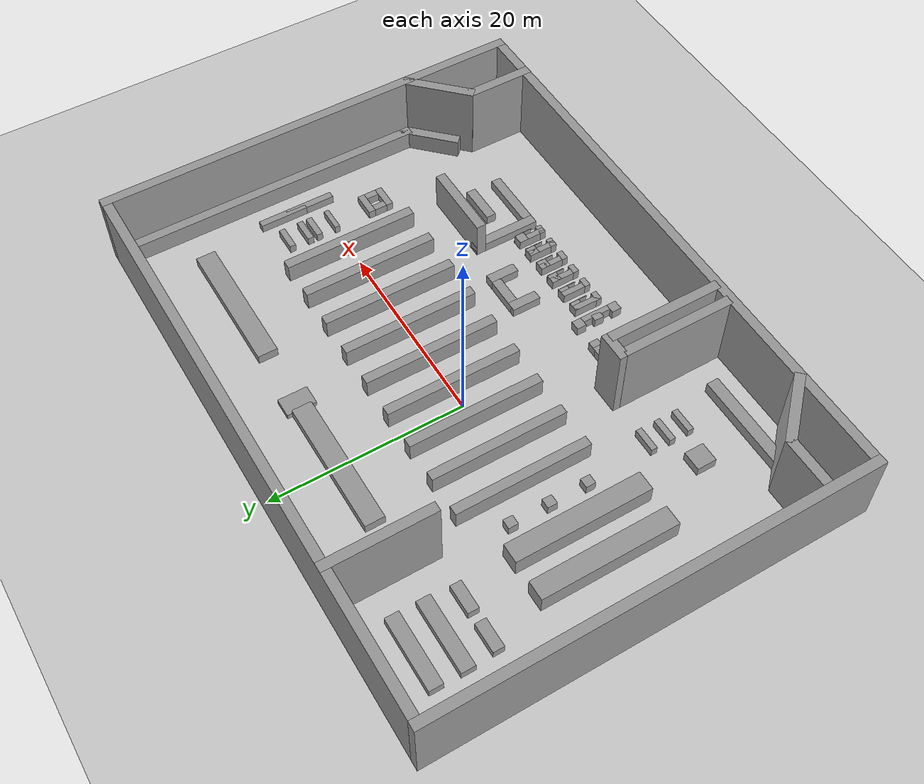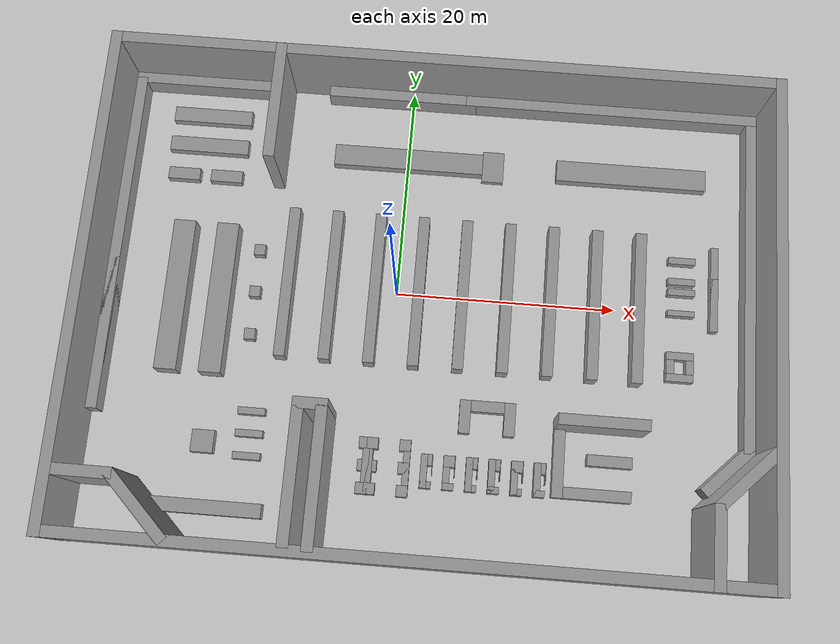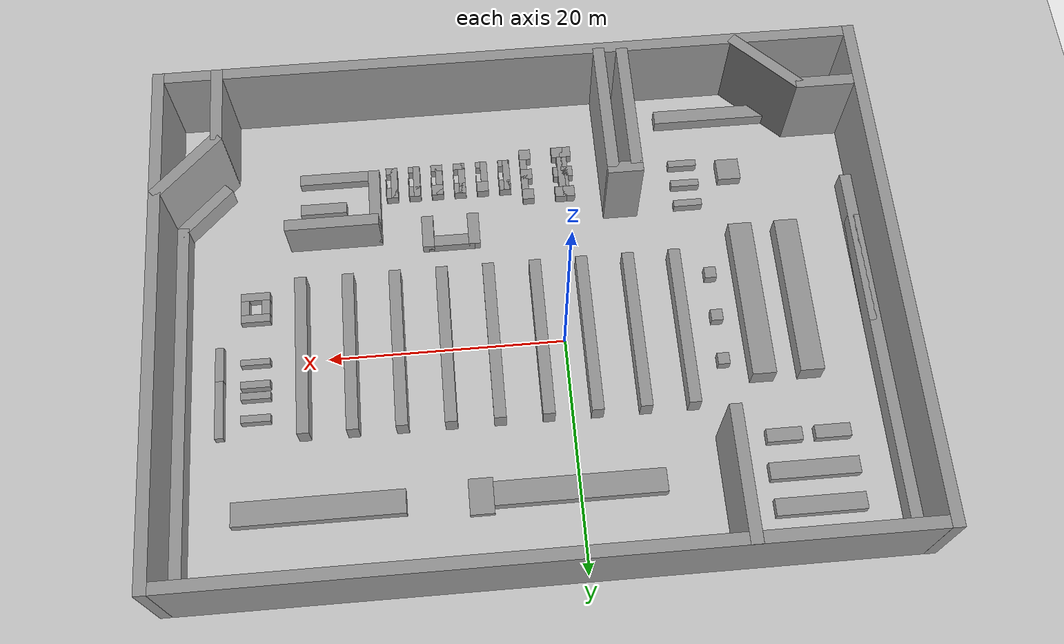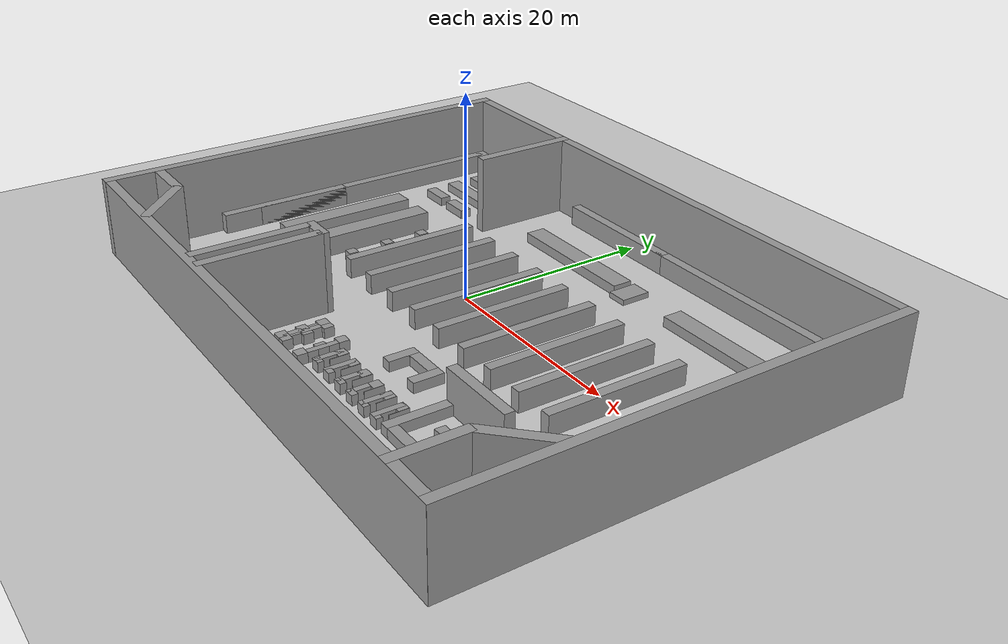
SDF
<sdf version="1.6">
 <world name="default">
  <light name="sun" type="directional">
   <pose>0 0 10 0 -0 0</pose>
   <diffuse>0.8 0.8 0.8 1</diffuse>
   <specular>0.2 0.2 0.2 1</specular>
   <attenuation>
    <range>1000</range>
    <constant>0.9</constant>
    <linear>0.01</linear>
    <quadratic>0.001</quadratic>
   </attenuation>
   <direction>-0.5 0.1 -0.9</direction>
  </light>
  <model name="ground_plane">
   <static>1</static>
   <link name="link">
    <collision name="collision">
     <geometry><plane><normal>0 0 1</normal><size>100 100</size></plane></geometry>
     <surface>
      <contact><collide_bitmask>65535</collide_bitmask></contact>
      <friction><ode><mu>100</mu><mu2>50</mu2></ode></friction>
     </surface>
    </collision>
    <visual name="visual">
     <cast_shadows>0</cast_shadows>
     <geometry><plane><normal>0 0 1</normal><size>100 100</size></plane></geometry>
     <material>
      <script><uri>file://media/materials/scripts/gazebo.material</uri><name>Gazebo/Grey</name></script>
     </material>
    </visual>
   </link>
  </model>
  <gravity>0 0 -9.8</gravity>
  <magnetic_field>6e-06 2.3e-05 -4.2e-05</magnetic_field>
  <atmosphere type="adiabatic"/>
  <physics name="default_physics" default="0" type="ode">
   <max_step_size>0.001</max_step_size>
   <real_time_factor>1</real_time_factor>
   <real_time_update_rate>1000</real_time_update_rate>
  </physics>
  <scene><ambient>0.4 0.4 0.4 1</ambient><background>0.7 0.7 0.7 1</background><shadows>1</shadows></scene>
  <audio><device>default</device></audio>
  <spherical_coordinates>
   <surface_model>EARTH_WGS84</surface_model>
   <latitude_deg>0</latitude_deg>
   <longitude_deg>0</longitude_deg>
   <elevation>0</elevation>
   <heading_deg>0</heading_deg>
  </spherical_coordinates>
  <model name="shelf">
   <link name="link">
    <inertial>
     <mass>1</mass>
     <inertia>
      <ixx>0.166667</ixx>
      <ixy>0</ixy>
      <ixz>0</ixz>
      <iyy>0.166667</iyy>
      <iyz>0</iyz>
      <izz>0.166667</izz>
     </inertia>
    </inertial>
    <visual name="visual">
     <geometry><box><size>1 14 2</size></box></geometry>
     <material>
      <script><name>Gazebo/Grey</name><uri>file://media/materials/scripts/gazebo.material</uri></script>
     </material>
    </visual>
    <collision name="collision">
     <geometry><box><size>1 14 2</size></box></geometry>
     <surface>
      <friction>
       <ode><mu>1</mu><mu2>1</mu2><fdir1>0 0 0</fdir1><slip1>0</slip1><slip2>0</slip2></ode>
       <torsional>
        <coefficient>1</coefficient>
        <patch_radius>0</patch_radius>
        <surface_radius>0</surface_radius>
        <use_patch_radius>1</use_patch_radius>
        <ode><slip>0</slip></ode>
       </torsional>
      </friction>
      <bounce><restitution_coefficient>0</restitution_coefficient><threshold>1e+06</threshold></bounce>
      <contact>
       <collide_without_contact>0</collide_without_contact>
       <collide_without_contact_bitmask>1</collide_without_contact_bitmask>
       <collide_bitmask>1</collide_bitmask>
       <ode>
        <soft_cfm>0</soft_cfm>
        <soft_erp>0.2</soft_erp>
        <kp>1e+13</kp>
        <kd>1</kd>
        <max_vel>0.01</max_vel>
        <min_depth>0</min_depth>
       </ode>
       <bullet>
        <split_impulse>1</split_impulse>
        <split_impulse_penetration_threshold>-0.01</split_impulse_penetration_threshold>
        <soft_cfm>0</soft_cfm>
        <soft_erp>0.2</soft_erp>
        <kp>1e+13</kp>
        <kd>1</kd>
       </bullet>
      </contact>
     </surface>
    </collision>
   </link>
   <static>1</static>
   <pose>-10 0 1 0 -0 0</pose>
  </model>
  <model name="shelf_0">
   <link name="link">
    <inertial>
     <mass>1</mass>
     <inertia>
      <ixx>0.166667</ixx>
      <ixy>0</ixy>
      <ixz>0</ixz>
      <iyy>0.166667</iyy>
      <iyz>0</iyz>
      <izz>0.166667</izz>
     </inertia>
    </inertial>
    <visual name="visual">
     <geometry><box><size>1 14 2</size></box></geometry>
     <material>
      <script><name>Gazebo/Grey</name><uri>file://media/materials/scripts/gazebo.material</uri></script>
     </material>
    </visual>
    <collision name="collision">
     <geometry><box><size>1 14 2</size></box></geometry>
     <surface>
      <friction>
       <ode><mu>1</mu><mu2>1</mu2><fdir1>0 0 0</fdir1><slip1>0</slip1><slip2>0</slip2></ode>
       <torsional>
        <coefficient>1</coefficient>
        <patch_radius>0</patch_radius>
        <surface_radius>0</surface_radius>
        <use_patch_radius>1</use_patch_radius>
        <ode><slip>0</slip></ode>
       </torsional>
      </friction>
      <bounce><restitution_coefficient>0</restitution_coefficient><threshold>1e+06</threshold></bounce>
      <contact>
       <collide_without_contact>0</collide_without_contact>
       <collide_without_contact_bitmask>1</collide_without_contact_bitmask>
       <collide_bitmask>1</collide_bitmask>
       <ode>
        <soft_cfm>0</soft_cfm>
        <soft_erp>0.2</soft_erp>
        <kp>1e+13</kp>
        <kd>1</kd>
        <max_vel>0.01</max_vel>
        <min_depth>0</min_depth>
       </ode>
       <bullet>
        <split_impulse>1</split_impulse>
        <split_impulse_penetration_threshold>-0.01</split_impulse_penetration_threshold>
        <soft_cfm>0</soft_cfm>
        <soft_erp>0.2</soft_erp>
        <kp>1e+13</kp>
        <kd>1</kd>
       </bullet>
      </contact>
     </surface>
    </collision>
   </link>
   <static>1</static>
   <pose>-6 0 1 0 -0 0</pose>
  </model>
  <model name="shelf_1">
   <link name="link">
    <inertial>
     <mass>1</mass>
     <inertia>
      <ixx>0.166667</ixx>
      <ixy>0</ixy>
      <ixz>0</ixz>
      <iyy>0.166667</iyy>
      <iyz>0</iyz>
      <izz>0.166667</izz>
     </inertia>
    </inertial>
    <visual name="visual">
     <geometry><box><size>1 14 2</size></box></geometry>
     <material>
      <script><name>Gazebo/Grey</name><uri>file://media/materials/scripts/gazebo.material</uri></script>
     </material>
    </visual>
    <collision name="collision">
     <geometry><box><size>1 14 2</size></box></geometry>
     <surface>
      <friction>
       <ode><mu>1</mu><mu2>1</mu2><fdir1>0 0 0</fdir1><slip1>0</slip1><slip2>0</slip2></ode>
       <torsional>
        <coefficient>1</coefficient>
        <patch_radius>0</patch_radius>
        <surface_radius>0</surface_radius>
        <use_patch_radius>1</use_patch_radius>
        <ode><slip>0</slip></ode>
       </torsional>
      </friction>
      <bounce><restitution_coefficient>0</restitution_coefficient><threshold>1e+06</threshold></bounce>
      <contact>
       <collide_without_contact>0</collide_without_contact>
       <collide_without_contact_bitmask>1</collide_without_contact_bitmask>
       <collide_bitmask>1</collide_bitmask>
       <ode>
        <soft_cfm>0</soft_cfm>
        <soft_erp>0.2</soft_erp>
        <kp>1e+13</kp>
        <kd>1</kd>
        <max_vel>0.01</max_vel>
        <min_depth>0</min_depth>
       </ode>
       <bullet>
        <split_impulse>1</split_impulse>
        <split_impulse_penetration_threshold>-0.01</split_impulse_penetration_threshold>
        <soft_cfm>0</soft_cfm>
        <soft_erp>0.2</soft_erp>
        <kp>1e+13</kp>
        <kd>1</kd>
       </bullet>
      </contact>
     </surface>
    </collision>
   </link>
   <static>1</static>
   <pose>-2 0 1 0 -0 0</pose>
  </model>
  <model name="shelf_2">
   <link name="link">
    <inertial>
     <mass>1</mass>
     <inertia>
      <ixx>0.166667</ixx>
      <ixy>0</ixy>
      <ixz>0</ixz>
      <iyy>0.166667</iyy>
      <iyz>0</iyz>
      <izz>0.166667</izz>
     </inertia>
    </inertial>
    <visual name="visual">
     <geometry><box><size>1 14 2</size></box></geometry>
     <material>
      <script><name>Gazebo/Grey</name><uri>file://media/materials/scripts/gazebo.material</uri></script>
     </material>
    </visual>
    <collision name="collision">
     <geometry><box><size>1 14 2</size></box></geometry>
     <surface>
      <friction>
       <ode><mu>1</mu><mu2>1</mu2><fdir1>0 0 0</fdir1><slip1>0</slip1><slip2>0</slip2></ode>
       <torsional>
        <coefficient>1</coefficient>
        <patch_radius>0</patch_radius>
        <surface_radius>0</surface_radius>
        <use_patch_radius>1</use_patch_radius>
        <ode><slip>0</slip></ode>
       </torsional>
      </friction>
      <bounce><restitution_coefficient>0</restitution_coefficient><threshold>1e+06</threshold></bounce>
      <contact>
       <collide_without_contact>0</collide_without_contact>
       <collide_without_contact_bitmask>1</collide_without_contact_bitmask>
       <collide_bitmask>1</collide_bitmask>
       <ode>
        <soft_cfm>0</soft_cfm>
        <soft_erp>0.2</soft_erp>
        <kp>1e+13</kp>
        <kd>1</kd>
        <max_vel>0.01</max_vel>
        <min_depth>0</min_depth>
       </ode>
       <bullet>
        <split_impulse>1</split_impulse>
        <split_impulse_penetration_threshold>-0.01</split_impulse_penetration_threshold>
        <soft_cfm>0</soft_cfm>
        <soft_erp>0.2</soft_erp>
        <kp>1e+13</kp>
        <kd>1</kd>
       </bullet>
      </contact>
     </surface>
    </collision>
   </link>
   <static>1</static>
   <pose>2 0 1 0 -0 0</pose>
  </model>
  <model name="shelf_3">
   <link name="link">
    <inertial>
     <mass>1</mass>
     <inertia>
      <ixx>0.166667</ixx>
      <ixy>0</ixy>
      <ixz>0</ixz>
      <iyy>0.166667</iyy>
      <iyz>0</iyz>
      <izz>0.166667</izz>
     </inertia>
    </inertial>
    <visual name="visual">
     <geometry><box><size>1 14 2</size></box></geometry>
     <material>
      <script><name>Gazebo/Grey</name><uri>file://media/materials/scripts/gazebo.material</uri></script>
     </material>
    </visual>
    <collision name="collision">
     <geometry><box><size>1 14 2</size></box></geometry>
     <surface>
      <friction>
       <ode><mu>1</mu><mu2>1</mu2><fdir1>0 0 0</fdir1><slip1>0</slip1><slip2>0</slip2></ode>
       <torsional>
        <coefficient>1</coefficient>
        <patch_radius>0</patch_radius>
        <surface_radius>0</surface_radius>
        <use_patch_radius>1</use_patch_radius>
        <ode><slip>0</slip></ode>
       </torsional>
      </friction>
      <bounce><restitution_coefficient>0</restitution_coefficient><threshold>1e+06</threshold></bounce>
      <contact>
       <collide_without_contact>0</collide_without_contact>
       <collide_without_contact_bitmask>1</collide_without_contact_bitmask>
       <collide_bitmask>1</collide_bitmask>
       <ode>
        <soft_cfm>0</soft_cfm>
        <soft_erp>0.2</soft_erp>
        <kp>1e+13</kp>
        <kd>1</kd>
        <max_vel>0.01</max_vel>
        <min_depth>0</min_depth>
       </ode>
       <bullet>
        <split_impulse>1</split_impulse>
        <split_impulse_penetration_threshold>-0.01</split_impulse_penetration_threshold>
        <soft_cfm>0</soft_cfm>
        <soft_erp>0.2</soft_erp>
        <kp>1e+13</kp>
        <kd>1</kd>
       </bullet>
      </contact>
     </surface>
    </collision>
   </link>
   <static>1</static>
   <pose>6 0 1 0 -0 0</pose>
  </model>
  <model name="shelf_4">
   <link name="link">
    <inertial>
     <mass>1</mass>
     <inertia>
      <ixx>0.166667</ixx>
      <ixy>0</ixy>
      <ixz>0</ixz>
      <iyy>0.166667</iyy>
      <iyz>0</iyz>
      <izz>0.166667</izz>
     </inertia>
    </inertial>
    <visual name="visual">
     <geometry><box><size>1 14 2</size></box></geometry>
     <material>
      <script><name>Gazebo/Grey</name><uri>file://media/materials/scripts/gazebo.material</uri></script>
     </material>
    </visual>
    <collision name="collision">
     <geometry><box><size>1 14 2</size></box></geometry>
     <surface>
      <friction>
       <ode><mu>1</mu><mu2>1</mu2><fdir1>0 0 0</fdir1><slip1>0</slip1><slip2>0</slip2></ode>
       <torsional>
        <coefficient>1</coefficient>
        <patch_radius>0</patch_radius>
        <surface_radius>0</surface_radius>
        <use_patch_radius>1</use_patch_radius>
        <ode><slip>0</slip></ode>
       </torsional>
      </friction>
      <bounce><restitution_coefficient>0</restitution_coefficient><threshold>1e+06</threshold></bounce>
      <contact>
       <collide_without_contact>0</collide_without_contact>
       <collide_without_contact_bitmask>1</collide_without_contact_bitmask>
       <collide_bitmask>1</collide_bitmask>
       <ode>
        <soft_cfm>0</soft_cfm>
        <soft_erp>0.2</soft_erp>
        <kp>1e+13</kp>
        <kd>1</kd>
        <max_vel>0.01</max_vel>
        <min_depth>0</min_depth>
       </ode>
       <bullet>
        <split_impulse>1</split_impulse>
        <split_impulse_penetration_threshold>-0.01</split_impulse_penetration_threshold>
        <soft_cfm>0</soft_cfm>
        <soft_erp>0.2</soft_erp>
        <kp>1e+13</kp>
        <kd>1</kd>
       </bullet>
      </contact>
     </surface>
    </collision>
   </link>
   <static>1</static>
   <pose>10 0 1 0 -0 0</pose>
  </model>
  <model name="shelf_5">
   <link name="link">
    <inertial>
     <mass>1</mass>
     <inertia>
      <ixx>0.166667</ixx>
      <ixy>0</ixy>
      <ixz>0</ixz>
      <iyy>0.166667</iyy>
      <iyz>0</iyz>
      <izz>0.166667</izz>
     </inertia>
    </inertial>
    <visual name="visual">
     <geometry><box><size>1 14 2</size></box></geometry>
     <material>
      <script><name>Gazebo/Grey</name><uri>file://media/materials/scripts/gazebo.material</uri></script>
     </material>
    </visual>
    <collision name="collision">
     <geometry><box><size>1 14 2</size></box></geometry>
     <surface>
      <friction>
       <ode><mu>1</mu><mu2>1</mu2><fdir1>0 0 0</fdir1><slip1>0</slip1><slip2>0</slip2></ode>
       <torsional>
        <coefficient>1</coefficient>
        <patch_radius>0</patch_radius>
        <surface_radius>0</surface_radius>
        <use_patch_radius>1</use_patch_radius>
        <ode><slip>0</slip></ode>
       </torsional>
      </friction>
      <bounce><restitution_coefficient>0</restitution_coefficient><threshold>1e+06</threshold></bounce>
      <contact>
       <collide_without_contact>0</collide_without_contact>
       <collide_without_contact_bitmask>1</collide_without_contact_bitmask>
       <collide_bitmask>1</collide_bitmask>
       <ode>
        <soft_cfm>0</soft_cfm>
        <soft_erp>0.2</soft_erp>
        <kp>1e+13</kp>
        <kd>1</kd>
        <max_vel>0.01</max_vel>
        <min_depth>0</min_depth>
       </ode>
       <bullet>
        <split_impulse>1</split_impulse>
        <split_impulse_penetration_threshold>-0.01</split_impulse_penetration_threshold>
        <soft_cfm>0</soft_cfm>
        <soft_erp>0.2</soft_erp>
        <kp>1e+13</kp>
        <kd>1</kd>
       </bullet>
      </contact>
     </surface>
    </collision>
   </link>
   <static>1</static>
   <pose>14 0 1 0 -0 0</pose>
  </model>
  <model name="shelf_6">
   <link name="link">
    <inertial>
     <mass>1</mass>
     <inertia>
      <ixx>0.166667</ixx>
      <ixy>0</ixy>
      <ixz>0</ixz>
      <iyy>0.166667</iyy>
      <iyz>0</iyz>
      <izz>0.166667</izz>
     </inertia>
    </inertial>
    <visual name="visual">
     <geometry><box><size>1 14 2</size></box></geometry>
     <material>
      <script><name>Gazebo/Grey</name><uri>file://media/materials/scripts/gazebo.material</uri></script>
     </material>
    </visual>
    <collision name="collision">
     <geometry><box><size>1 14 2</size></box></geometry>
     <surface>
      <friction>
       <ode><mu>1</mu><mu2>1</mu2><fdir1>0 0 0</fdir1><slip1>0</slip1><slip2>0</slip2></ode>
       <torsional>
        <coefficient>1</coefficient>
        <patch_radius>0</patch_radius>
        <surface_radius>0</surface_radius>
        <use_patch_radius>1</use_patch_radius>
        <ode><slip>0</slip></ode>
       </torsional>
      </friction>
      <bounce><restitution_coefficient>0</restitution_coefficient><threshold>1e+06</threshold></bounce>
      <contact>
       <collide_without_contact>0</collide_without_contact>
       <collide_without_contact_bitmask>1</collide_without_contact_bitmask>
       <collide_bitmask>1</collide_bitmask>
       <ode>
        <soft_cfm>0</soft_cfm>
        <soft_erp>0.2</soft_erp>
        <kp>1e+13</kp>
        <kd>1</kd>
        <max_vel>0.01</max_vel>
        <min_depth>0</min_depth>
       </ode>
       <bullet>
        <split_impulse>1</split_impulse>
        <split_impulse_penetration_threshold>-0.01</split_impulse_penetration_threshold>
        <soft_cfm>0</soft_cfm>
        <soft_erp>0.2</soft_erp>
        <kp>1e+13</kp>
        <kd>1</kd>
       </bullet>
      </contact>
     </surface>
    </collision>
   </link>
   <static>1</static>
   <pose>18 0 1 0 -0 0</pose>
  </model>
  <model name="shelf_7">
   <link name="link">
    <inertial>
     <mass>1</mass>
     <inertia>
      <ixx>0.166667</ixx>
      <ixy>0</ixy>
      <ixz>0</ixz>
      <iyy>0.166667</iyy>
      <iyz>0</iyz>
      <izz>0.166667</izz>
     </inertia>
    </inertial>
    <visual name="visual">
     <geometry><box><size>1 14 2</size></box></geometry>
     <material>
      <script><name>Gazebo/Grey</name><uri>file://media/materials/scripts/gazebo.material</uri></script>
     </material>
    </visual>
    <collision name="collision">
     <geometry><box><size>1 14 2</size></box></geometry>
     <surface>
      <friction>
       <ode><mu>1</mu><mu2>1</mu2><fdir1>0 0 0</fdir1><slip1>0</slip1><slip2>0</slip2></ode>
       <torsional>
        <coefficient>1</coefficient>
        <patch_radius>0</patch_radius>
        <surface_radius>0</surface_radius>
        <use_patch_radius>1</use_patch_radius>
        <ode><slip>0</slip></ode>
       </torsional>
      </friction>
      <bounce><restitution_coefficient>0</restitution_coefficient><threshold>1e+06</threshold></bounce>
      <contact>
       <collide_without_contact>0</collide_without_contact>
       <collide_without_contact_bitmask>1</collide_without_contact_bitmask>
       <collide_bitmask>1</collide_bitmask>
       <ode>
        <soft_cfm>0</soft_cfm>
        <soft_erp>0.2</soft_erp>
        <kp>1e+13</kp>
        <kd>1</kd>
        <max_vel>0.01</max_vel>
        <min_depth>0</min_depth>
       </ode>
       <bullet>
        <split_impulse>1</split_impulse>
        <split_impulse_penetration_threshold>-0.01</split_impulse_penetration_threshold>
        <soft_cfm>0</soft_cfm>
        <soft_erp>0.2</soft_erp>
        <kp>1e+13</kp>
        <kd>1</kd>
       </bullet>
      </contact>
     </surface>
    </collision>
   </link>
   <static>1</static>
   <pose>22 0 1 0 -0 0</pose>
  </model>
  <model name="shelf_clone_clone">
   <link name="link">
    <inertial>
     <mass>1</mass>
     <inertia>
      <ixx>0.166667</ixx>
      <ixy>0</ixy>
      <ixz>0</ixz>
      <iyy>0.166667</iyy>
      <iyz>0</iyz>
      <izz>0.166667</izz>
     </inertia>
    </inertial>
    <visual name="visual">
     <geometry><box><size>0.706603 2.46632 0.879745</size></box></geometry>
     <material>
      <script><name>Gazebo/Grey</name><uri>file://media/materials/scripts/gazebo.material</uri></script>
     </material>
    </visual>
    <collision name="collision">
     <geometry><box><size>0.706603 2.46632 0.879745</size></box></geometry>
     <surface>
      <friction>
       <ode><mu>1</mu><mu2>1</mu2><fdir1>0 0 0</fdir1><slip1>0</slip1><slip2>0</slip2></ode>
       <torsional>
        <coefficient>1</coefficient>
        <patch_radius>0</patch_radius>
        <surface_radius>0</surface_radius>
        <use_patch_radius>1</use_patch_radius>
        <ode><slip>0</slip></ode>
       </torsional>
      </friction>
      <bounce><restitution_coefficient>0</restitution_coefficient><threshold>1e+06</threshold></bounce>
      <contact>
       <collide_without_contact>0</collide_without_contact>
       <collide_without_contact_bitmask>1</collide_without_contact_bitmask>
       <collide_bitmask>1</collide_bitmask>
       <ode>
        <soft_cfm>0</soft_cfm>
        <soft_erp>0.2</soft_erp>
        <kp>1e+13</kp>
        <kd>1</kd>
        <max_vel>0.01</max_vel>
        <min_depth>0</min_depth>
       </ode>
       <bullet>
        <split_impulse>1</split_impulse>
        <split_impulse_penetration_threshold>-0.01</split_impulse_penetration_threshold>
        <soft_cfm>0</soft_cfm>
        <soft_erp>0.2</soft_erp>
        <kp>1e+13</kp>
        <kd>1</kd>
       </bullet>
      </contact>
     </surface>
    </collision>
   </link>
   <static>1</static>
   <pose>26 -4 0.440412 0 0 -1.5708</pose>
  </model>
  <model name="shelf_clone_clone_0_clone">
   <link name="link">
    <inertial>
     <mass>1</mass>
     <inertia>
      <ixx>0.166667</ixx>
      <ixy>0</ixy>
      <ixz>0</ixz>
      <iyy>0.166667</iyy>
      <iyz>0</iyz>
      <izz>0.166667</izz>
     </inertia>
    </inertial>
    <visual name="visual">
     <geometry><box><size>0.706603 1.29816 0.879745</size></box></geometry>
     <material>
      <script><name>Gazebo/Grey</name><uri>file://media/materials/scripts/gazebo.material</uri></script>
     </material>
    </visual>
    <collision name="collision">
     <geometry><box><size>0.706603 1.29816 0.879745</size></box></geometry>
     <surface>
      <friction>
       <ode><mu>1</mu><mu2>1</mu2><fdir1>0 0 0</fdir1><slip1>0</slip1><slip2>0</slip2></ode>
       <torsional>
        <coefficient>1</coefficient>
        <patch_radius>0</patch_radius>
        <surface_radius>0</surface_radius>
        <use_patch_radius>1</use_patch_radius>
        <ode><slip>0</slip></ode>
       </torsional>
      </friction>
      <bounce><restitution_coefficient>0</restitution_coefficient><threshold>1e+06</threshold></bounce>
      <contact>
       <collide_without_contact>0</collide_without_contact>
       <collide_without_contact_bitmask>1</collide_without_contact_bitmask>
       <collide_bitmask>1</collide_bitmask>
       <ode>
        <soft_cfm>0</soft_cfm>
        <soft_erp>0.2</soft_erp>
        <kp>1e+13</kp>
        <kd>1</kd>
        <max_vel>0.01</max_vel>
        <min_depth>0</min_depth>
       </ode>
       <bullet>
        <split_impulse>1</split_impulse>
        <split_impulse_penetration_threshold>-0.01</split_impulse_penetration_threshold>
        <soft_cfm>0</soft_cfm>
        <soft_erp>0.2</soft_erp>
        <kp>1e+13</kp>
        <kd>1</kd>
       </bullet>
      </contact>
     </surface>
    </collision>
   </link>
   <static>1</static>
   <pose>25.1203 -5 0.440412 0 0 -4e-06</pose>
  </model>
  <model name="shelf_clone_clone_clone_clone_0_clone">
   <link name="link">
    <inertial>
     <mass>1</mass>
     <inertia>
      <ixx>0.166667</ixx>
      <ixy>0</ixy>
      <ixz>0</ixz>
      <iyy>0.166667</iyy>
      <iyz>0</iyz>
      <izz>0.166667</izz>
     </inertia>
    </inertial>
    <visual name="visual">
     <geometry><box><size>0.6246 2.46632 0.879745</size></box></geometry>
     <material>
      <script><name>Gazebo/Grey</name><uri>file://media/materials/scripts/gazebo.material</uri></script>
     </material>
    </visual>
    <collision name="collision">
     <geometry><box><size>0.6246 2.46632 0.879745</size></box></geometry>
     <surface>
      <friction>
       <ode><mu>1</mu><mu2>1</mu2><fdir1>0 0 0</fdir1><slip1>0</slip1><slip2>0</slip2></ode>
       <torsional>
        <coefficient>1</coefficient>
        <patch_radius>0</patch_radius>
        <surface_radius>0</surface_radius>
        <use_patch_radius>1</use_patch_radius>
        <ode><slip>0</slip></ode>
       </torsional>
      </friction>
      <bounce><restitution_coefficient>0</restitution_coefficient><threshold>1e+06</threshold></bounce>
      <contact>
       <collide_without_contact>0</collide_without_contact>
       <collide_without_contact_bitmask>1</collide_without_contact_bitmask>
       <collide_bitmask>1</collide_bitmask>
       <ode>
        <soft_cfm>0</soft_cfm>
        <soft_erp>0.2</soft_erp>
        <kp>1e+13</kp>
        <kd>1</kd>
        <max_vel>0.01</max_vel>
        <min_depth>0</min_depth>
       </ode>
       <bullet>
        <split_impulse>1</split_impulse>
        <split_impulse_penetration_threshold>-0.01</split_impulse_penetration_threshold>
        <soft_cfm>0</soft_cfm>
        <soft_erp>0.2</soft_erp>
        <kp>1e+13</kp>
        <kd>1</kd>
       </bullet>
      </contact>
     </surface>
    </collision>
   </link>
   <static>1</static>
   <pose>26 2 0.440412 0 0 -1.5708</pose>
  </model>
  <model name="shelf_clone_0_clone">
   <link name="link">
    <inertial>
     <mass>1</mass>
     <inertia>
      <ixx>0.166667</ixx>
      <ixy>0</ixy>
      <ixz>0</ixz>
      <iyy>0.166667</iyy>
      <iyz>0</iyz>
      <izz>0.166667</izz>
     </inertia>
    </inertial>
    <visual name="visual">
     <geometry><box><size>2 14 2</size></box></geometry>
     <material>
      <script><name>Gazebo/Grey</name><uri>file://media/materials/scripts/gazebo.material</uri></script>
     </material>
    </visual>
    <collision name="collision">
     <geometry><box><size>2 14 2</size></box></geometry>
     <surface>
      <friction>
       <ode><mu>1</mu><mu2>1</mu2><fdir1>0 0 0</fdir1><slip1>0</slip1><slip2>0</slip2></ode>
       <torsional>
        <coefficient>1</coefficient>
        <patch_radius>0</patch_radius>
        <surface_radius>0</surface_radius>
        <use_patch_radius>1</use_patch_radius>
        <ode><slip>0</slip></ode>
       </torsional>
      </friction>
      <bounce><restitution_coefficient>0</restitution_coefficient><threshold>1e+06</threshold></bounce>
      <contact>
       <collide_without_contact>0</collide_without_contact>
       <collide_without_contact_bitmask>1</collide_without_contact_bitmask>
       <collide_bitmask>1</collide_bitmask>
       <ode>
        <soft_cfm>0</soft_cfm>
        <soft_erp>0.2</soft_erp>
        <kp>1e+13</kp>
        <kd>1</kd>
        <max_vel>0.01</max_vel>
        <min_depth>0</min_depth>
       </ode>
       <bullet>
        <split_impulse>1</split_impulse>
        <split_impulse_penetration_threshold>-0.01</split_impulse_penetration_threshold>
        <soft_cfm>0</soft_cfm>
        <soft_erp>0.2</soft_erp>
        <kp>1e+13</kp>
        <kd>1</kd>
       </bullet>
      </contact>
     </surface>
    </collision>
   </link>
   <static>1</static>
   <pose>-20 -2 1 0 -0 0</pose>
  </model>
  <model name="shelf_clone_clone_clone_2_clone">
   <link name="link">
    <inertial>
     <mass>1</mass>
     <inertia>
      <ixx>0.166667</ixx>
      <ixy>0</ixy>
      <ixz>0</ixz>
      <iyy>0.166667</iyy>
      <iyz>0</iyz>
      <izz>0.166667</izz>
     </inertia>
    </inertial>
    <visual name="visual">
     <geometry><box><size>1.41321 7.39896 0.879745</size></box></geometry>
     <material>
      <script><name>Gazebo/Grey</name><uri>file://media/materials/scripts/gazebo.material</uri></script>
     </material>
    </visual>
    <collision name="collision">
     <geometry><box><size>1.41321 7.39896 0.879745</size></box></geometry>
     <surface>
      <friction>
       <ode><mu>1</mu><mu2>1</mu2><fdir1>0 0 0</fdir1><slip1>0</slip1><slip2>0</slip2></ode>
       <torsional>
        <coefficient>1</coefficient>
        <patch_radius>0</patch_radius>
        <surface_radius>0</surface_radius>
        <use_patch_radius>1</use_patch_radius>
        <ode><slip>0</slip></ode>
       </torsional>
      </friction>
      <bounce><restitution_coefficient>0</restitution_coefficient><threshold>1e+06</threshold></bounce>
      <contact>
       <collide_without_contact>0</collide_without_contact>
       <collide_without_contact_bitmask>1</collide_without_contact_bitmask>
       <collide_bitmask>1</collide_bitmask>
       <ode>
        <soft_cfm>0</soft_cfm>
        <soft_erp>0.2</soft_erp>
        <kp>1e+13</kp>
        <kd>1</kd>
        <max_vel>0.01</max_vel>
        <min_depth>0</min_depth>
       </ode>
       <bullet>
        <split_impulse>1</split_impulse>
        <split_impulse_penetration_threshold>-0.01</split_impulse_penetration_threshold>
        <soft_cfm>0</soft_cfm>
        <soft_erp>0.2</soft_erp>
        <kp>1e+13</kp>
        <kd>1</kd>
       </bullet>
      </contact>
     </surface>
    </collision>
   </link>
   <static>1</static>
   <pose>-19 16 0.440412 0 0 -1.5708</pose>
  </model>
  <model name="shelf_clone_clone_clone_2_clone_0_clone">
   <link name="link">
    <inertial>
     <mass>1</mass>
     <inertia>
      <ixx>0.166667</ixx>
      <ixy>0</ixy>
      <ixz>0</ixz>
      <iyy>0.166667</iyy>
      <iyz>0</iyz>
      <izz>0.166667</izz>
     </inertia>
    </inertial>
    <visual name="visual">
     <geometry><box><size>1.12602 2.96029 0.879745</size></box></geometry>
     <material>
      <script><name>Gazebo/Grey</name><uri>file://media/materials/scripts/gazebo.material</uri></script>
     </material>
    </visual>
    <collision name="collision">
     <geometry><box><size>1.12602 2.96029 0.879745</size></box></geometry>
     <surface>
      <friction>
       <ode><mu>1</mu><mu2>1</mu2><fdir1>0 0 0</fdir1><slip1>0</slip1><slip2>0</slip2></ode>
       <torsional>
        <coefficient>1</coefficient>
        <patch_radius>0</patch_radius>
        <surface_radius>0</surface_radius>
        <use_patch_radius>1</use_patch_radius>
        <ode><slip>0</slip></ode>
       </torsional>
      </friction>
      <bounce><restitution_coefficient>0</restitution_coefficient><threshold>1e+06</threshold></bounce>
      <contact>
       <collide_without_contact>0</collide_without_contact>
       <collide_without_contact_bitmask>1</collide_without_contact_bitmask>
       <collide_bitmask>1</collide_bitmask>
       <ode>
        <soft_cfm>0</soft_cfm>
        <soft_erp>0.2</soft_erp>
        <kp>1e+13</kp>
        <kd>1</kd>
        <max_vel>0.01</max_vel>
        <min_depth>0</min_depth>
       </ode>
       <bullet>
        <split_impulse>1</split_impulse>
        <split_impulse_penetration_threshold>-0.01</split_impulse_penetration_threshold>
        <soft_cfm>0</soft_cfm>
        <soft_erp>0.2</soft_erp>
        <kp>1e+13</kp>
        <kd>1</kd>
       </bullet>
      </contact>
     </surface>
    </collision>
   </link>
   <static>1</static>
   <pose>-17 10 0.440412 0 0 -1.5708</pose>
  </model>
  <model name="shelf_clone_clone_clone_clone_0_clone_clone_clone">
   <link name="link">
    <inertial>
     <mass>1</mass>
     <inertia>
      <ixx>0.166667</ixx>
      <ixy>0</ixy>
      <ixz>0</ixz>
      <iyy>0.166667</iyy>
      <iyz>0</iyz>
      <izz>0.166667</izz>
     </inertia>
    </inertial>
    <visual name="visual">
     <geometry><box><size>0.6246 2.46632 0.879745</size></box></geometry>
     <material>
      <script><name>Gazebo/Grey</name><uri>file://media/materials/scripts/gazebo.material</uri></script>
     </material>
    </visual>
    <collision name="collision">
     <geometry><box><size>0.6246 2.46632 0.879745</size></box></geometry>
     <surface>
      <friction>
       <ode><mu>1</mu><mu2>1</mu2><fdir1>0 0 0</fdir1><slip1>0</slip1><slip2>0</slip2></ode>
       <torsional>
        <coefficient>1</coefficient>
        <patch_radius>0</patch_radius>
        <surface_radius>0</surface_radius>
        <use_patch_radius>1</use_patch_radius>
        <ode><slip>0</slip></ode>
       </torsional>
      </friction>
      <bounce><restitution_coefficient>0</restitution_coefficient><threshold>1e+06</threshold></bounce>
      <contact>
       <collide_without_contact>0</collide_without_contact>
       <collide_without_contact_bitmask>1</collide_without_contact_bitmask>
       <collide_bitmask>1</collide_bitmask>
       <ode>
        <soft_cfm>0</soft_cfm>
        <soft_erp>0.2</soft_erp>
        <kp>1e+13</kp>
        <kd>1</kd>
        <max_vel>0.01</max_vel>
        <min_depth>0</min_depth>
       </ode>
       <bullet>
        <split_impulse>1</split_impulse>
        <split_impulse_penetration_threshold>-0.01</split_impulse_penetration_threshold>
        <soft_cfm>0</soft_cfm>
        <soft_erp>0.2</soft_erp>
        <kp>1e+13</kp>
        <kd>1</kd>
       </bullet>
      </contact>
     </surface>
    </collision>
   </link>
   <static>1</static>
   <pose>-12 -14 0.440412 0 0 -1.5708</pose>
  </model>
  <model name="shelf_clone_clone_clone_clone_0_clone_clone_clone_clone">
   <link name="link">
    <inertial>
     <mass>1</mass>
     <inertia>
      <ixx>0.166667</ixx>
      <ixy>0</ixy>
      <ixz>0</ixz>
      <iyy>0.166667</iyy>
      <iyz>0</iyz>
      <izz>0.166667</izz>
     </inertia>
    </inertial>
    <visual name="visual">
     <geometry><box><size>0.6246 2.46632 0.879745</size></box></geometry>
     <material>
      <script><name>Gazebo/Grey</name><uri>file://media/materials/scripts/gazebo.material</uri></script>
     </material>
    </visual>
    <collision name="collision">
     <geometry><box><size>0.6246 2.46632 0.879745</size></box></geometry>
     <surface>
      <friction>
       <ode><mu>1</mu><mu2>1</mu2><fdir1>0 0 0</fdir1><slip1>0</slip1><slip2>0</slip2></ode>
       <torsional>
        <coefficient>1</coefficient>
        <patch_radius>0</patch_radius>
        <surface_radius>0</surface_radius>
        <use_patch_radius>1</use_patch_radius>
        <ode><slip>0</slip></ode>
       </torsional>
      </friction>
      <bounce><restitution_coefficient>0</restitution_coefficient><threshold>1e+06</threshold></bounce>
      <contact>
       <collide_without_contact>0</collide_without_contact>
       <collide_without_contact_bitmask>1</collide_without_contact_bitmask>
       <collide_bitmask>1</collide_bitmask>
       <ode>
        <soft_cfm>0</soft_cfm>
        <soft_erp>0.2</soft_erp>
        <kp>1e+13</kp>
        <kd>1</kd>
        <max_vel>0.01</max_vel>
        <min_depth>0</min_depth>
       </ode>
       <bullet>
        <split_impulse>1</split_impulse>
        <split_impulse_penetration_threshold>-0.01</split_impulse_penetration_threshold>
        <soft_cfm>0</soft_cfm>
        <soft_erp>0.2</soft_erp>
        <kp>1e+13</kp>
        <kd>1</kd>
       </bullet>
      </contact>
     </surface>
    </collision>
   </link>
   <static>1</static>
   <pose>-12 -12 0.440412 0 0 -1.5708</pose>
  </model>
  <model name="shelf_clone_clone_clone_clone_0_clone_clone_clone_clone_0">
   <link name="link">
    <inertial>
     <mass>1</mass>
     <inertia>
      <ixx>0.166667</ixx>
      <ixy>0</ixy>
      <ixz>0</ixz>
      <iyy>0.166667</iyy>
      <iyz>0</iyz>
      <izz>0.166667</izz>
     </inertia>
    </inertial>
    <visual name="visual">
     <geometry><box><size>0.6246 2.46632 0.879745</size></box></geometry>
     <material>
      <script><name>Gazebo/Grey</name><uri>file://media/materials/scripts/gazebo.material</uri></script>
     </material>
    </visual>
    <collision name="collision">
     <geometry><box><size>0.6246 2.46632 0.879745</size></box></geometry>
     <surface>
      <friction>
       <ode><mu>1</mu><mu2>1</mu2><fdir1>0 0 0</fdir1><slip1>0</slip1><slip2>0</slip2></ode>
       <torsional>
        <coefficient>1</coefficient>
        <patch_radius>0</patch_radius>
        <surface_radius>0</surface_radius>
        <use_patch_radius>1</use_patch_radius>
        <ode><slip>0</slip></ode>
       </torsional>
      </friction>
      <bounce><restitution_coefficient>0</restitution_coefficient><threshold>1e+06</threshold></bounce>
      <contact>
       <collide_without_contact>0</collide_without_contact>
       <collide_without_contact_bitmask>1</collide_without_contact_bitmask>
       <collide_bitmask>1</collide_bitmask>
       <ode>
        <soft_cfm>0</soft_cfm>
        <soft_erp>0.2</soft_erp>
        <kp>1e+13</kp>
        <kd>1</kd>
        <max_vel>0.01</max_vel>
        <min_depth>0</min_depth>
       </ode>
       <bullet>
        <split_impulse>1</split_impulse>
        <split_impulse_penetration_threshold>-0.01</split_impulse_penetration_threshold>
        <soft_cfm>0</soft_cfm>
        <soft_erp>0.2</soft_erp>
        <kp>1e+13</kp>
        <kd>1</kd>
       </bullet>
      </contact>
     </surface>
    </collision>
   </link>
   <static>1</static>
   <pose>-12 -16 0.440412 0 0 -1.5708</pose>
  </model>
  <model name="shelf_clone_clone_clone_clone_0_clone_clone">
   <link name="link">
    <inertial>
     <mass>1</mass>
     <inertia>
      <ixx>0.166667</ixx>
      <ixy>0</ixy>
      <ixz>0</ixz>
      <iyy>0.166667</iyy>
      <iyz>0</iyz>
      <izz>0.166667</izz>
     </inertia>
    </inertial>
    <visual name="visual">
     <geometry><box><size>0.6246 2.46632 0.879745</size></box></geometry>
     <material>
      <script><name>Gazebo/Grey</name><uri>file://media/materials/scripts/gazebo.material</uri></script>
     </material>
    </visual>
    <collision name="collision">
     <geometry><box><size>0.6246 2.46632 0.879745</size></box></geometry>
     <surface>
      <friction>
       <ode><mu>1</mu><mu2>1</mu2><fdir1>0 0 0</fdir1><slip1>0</slip1><slip2>0</slip2></ode>
       <torsional>
        <coefficient>1</coefficient>
        <patch_radius>0</patch_radius>
        <surface_radius>0</surface_radius>
        <use_patch_radius>1</use_patch_radius>
        <ode><slip>0</slip></ode>
       </torsional>
      </friction>
      <bounce><restitution_coefficient>0</restitution_coefficient><threshold>1e+06</threshold></bounce>
      <contact>
       <collide_without_contact>0</collide_without_contact>
       <collide_without_contact_bitmask>1</collide_without_contact_bitmask>
       <collide_bitmask>1</collide_bitmask>
       <ode>
        <soft_cfm>0</soft_cfm>
        <soft_erp>0.2</soft_erp>
        <kp>1e+13</kp>
        <kd>1</kd>
        <max_vel>0.01</max_vel>
        <min_depth>0</min_depth>
       </ode>
       <bullet>
        <split_impulse>1</split_impulse>
        <split_impulse_penetration_threshold>-0.01</split_impulse_penetration_threshold>
        <soft_cfm>0</soft_cfm>
        <soft_erp>0.2</soft_erp>
        <kp>1e+13</kp>
        <kd>1</kd>
       </bullet>
      </contact>
     </surface>
    </collision>
   </link>
   <static>1</static>
   <pose>26 3 0.440412 0 0 -1.5708</pose>
  </model>
  <model name="shelf_clone_clone_clone_2_clone_clone">
   <link name="link">
    <inertial>
     <mass>1</mass>
     <inertia>
      <ixx>0.166667</ixx>
      <ixy>0</ixy>
      <ixz>0</ixz>
      <iyy>0.166667</iyy>
      <iyz>0</iyz>
      <izz>0.166667</izz>
     </inertia>
    </inertial>
    <visual name="visual">
     <geometry><box><size>1.41321 7.39896 0.879745</size></box></geometry>
     <material>
      <script><name>Gazebo/Grey</name><uri>file://media/materials/scripts/gazebo.material</uri></script>
     </material>
    </visual>
    <collision name="collision">
     <geometry><box><size>1.41321 7.39896 0.879745</size></box></geometry>
     <surface>
      <friction>
       <ode><mu>1</mu><mu2>1</mu2><fdir1>0 0 0</fdir1><slip1>0</slip1><slip2>0</slip2></ode>
       <torsional>
        <coefficient>1</coefficient>
        <patch_radius>0</patch_radius>
        <surface_radius>0</surface_radius>
        <use_patch_radius>1</use_patch_radius>
        <ode><slip>0</slip></ode>
       </torsional>
      </friction>
      <bounce><restitution_coefficient>0</restitution_coefficient><threshold>1e+06</threshold></bounce>
      <contact>
       <collide_without_contact>0</collide_without_contact>
       <collide_without_contact_bitmask>1</collide_without_contact_bitmask>
       <collide_bitmask>1</collide_bitmask>
       <ode>
        <soft_cfm>0</soft_cfm>
        <soft_erp>0.2</soft_erp>
        <kp>1e+13</kp>
        <kd>1</kd>
        <max_vel>0.01</max_vel>
        <min_depth>0</min_depth>
       </ode>
       <bullet>
        <split_impulse>1</split_impulse>
        <split_impulse_penetration_threshold>-0.01</split_impulse_penetration_threshold>
        <soft_cfm>0</soft_cfm>
        <soft_erp>0.2</soft_erp>
        <kp>1e+13</kp>
        <kd>1</kd>
       </bullet>
      </contact>
     </surface>
    </collision>
   </link>
   <static>1</static>
   <pose>-19 13 0.440412 0 0 -1.5708</pose>
  </model>
  <model name="shelf_clone_clone_clone_2_clone_0_clone_clone">
   <link name="link">
    <inertial>
     <mass>1</mass>
     <inertia>
      <ixx>0.166667</ixx>
      <ixy>0</ixy>
      <ixz>0</ixz>
      <iyy>0.166667</iyy>
      <iyz>0</iyz>
      <izz>0.166667</izz>
     </inertia>
    </inertial>
    <visual name="visual">
     <geometry><box><size>1.12602 2.96029 0.879745</size></box></geometry>
     <material>
      <script><name>Gazebo/Grey</name><uri>file://media/materials/scripts/gazebo.material</uri></script>
     </material>
    </visual>
    <collision name="collision">
     <geometry><box><size>1.12602 2.96029 0.879745</size></box></geometry>
     <surface>
      <friction>
       <ode><mu>1</mu><mu2>1</mu2><fdir1>0 0 0</fdir1><slip1>0</slip1><slip2>0</slip2></ode>
       <torsional>
        <coefficient>1</coefficient>
        <patch_radius>0</patch_radius>
        <surface_radius>0</surface_radius>
        <use_patch_radius>1</use_patch_radius>
        <ode><slip>0</slip></ode>
       </torsional>
      </friction>
      <bounce><restitution_coefficient>0</restitution_coefficient><threshold>1e+06</threshold></bounce>
      <contact>
       <collide_without_contact>0</collide_without_contact>
       <collide_without_contact_bitmask>1</collide_without_contact_bitmask>
       <collide_bitmask>1</collide_bitmask>
       <ode>
        <soft_cfm>0</soft_cfm>
        <soft_erp>0.2</soft_erp>
        <kp>1e+13</kp>
        <kd>1</kd>
        <max_vel>0.01</max_vel>
        <min_depth>0</min_depth>
       </ode>
       <bullet>
        <split_impulse>1</split_impulse>
        <split_impulse_penetration_threshold>-0.01</split_impulse_penetration_threshold>
        <soft_cfm>0</soft_cfm>
        <soft_erp>0.2</soft_erp>
        <kp>1e+13</kp>
        <kd>1</kd>
       </bullet>
      </contact>
     </surface>
    </collision>
   </link>
   <static>1</static>
   <pose>-21 10 0.440412 0 0 -1.5708</pose>
  </model>
  <model name="shelf_clone_clone_clone_clone_1_clone">
   <link name="link">
    <inertial>
     <mass>1</mass>
     <inertia>
      <ixx>0.166667</ixx>
      <ixy>0</ixy>
      <ixz>0</ixz>
      <iyy>0.166667</iyy>
      <iyz>0</iyz>
      <izz>0.166667</izz>
     </inertia>
    </inertial>
    <visual name="visual">
     <geometry><box><size>0.522227 2.46632 0.879745</size></box></geometry>
     <material>
      <script><name>Gazebo/Grey</name><uri>file://media/materials/scripts/gazebo.material</uri></script>
     </material>
    </visual>
    <collision name="collision">
     <geometry><box><size>0.522227 2.46632 0.879745</size></box></geometry>
     <surface>
      <friction>
       <ode><mu>1</mu><mu2>1</mu2><fdir1>0 0 0</fdir1><slip1>0</slip1><slip2>0</slip2></ode>
       <torsional>
        <coefficient>1</coefficient>
        <patch_radius>0</patch_radius>
        <surface_radius>0</surface_radius>
        <use_patch_radius>1</use_patch_radius>
        <ode><slip>0</slip></ode>
       </torsional>
      </friction>
      <bounce><restitution_coefficient>0</restitution_coefficient><threshold>1e+06</threshold></bounce>
      <contact>
       <collide_without_contact>0</collide_without_contact>
       <collide_without_contact_bitmask>1</collide_without_contact_bitmask>
       <collide_bitmask>1</collide_bitmask>
       <ode>
        <soft_cfm>0</soft_cfm>
        <soft_erp>0.2</soft_erp>
        <kp>1e+13</kp>
        <kd>1</kd>
        <max_vel>0.01</max_vel>
        <min_depth>0</min_depth>
       </ode>
       <bullet>
        <split_impulse>1</split_impulse>
        <split_impulse_penetration_threshold>-0.01</split_impulse_penetration_threshold>
        <soft_cfm>0</soft_cfm>
        <soft_erp>0.2</soft_erp>
        <kp>1e+13</kp>
        <kd>1</kd>
       </bullet>
      </contact>
     </surface>
    </collision>
   </link>
   <static>1</static>
   <pose>26 0 0.440412 0 0 -1.5708</pose>
  </model>
  <model name="shelf_clone_clone_clone">
   <link name="link">
    <inertial>
     <mass>1</mass>
     <inertia>
      <ixx>0.166667</ixx>
      <ixy>0</ixy>
      <ixz>0</ixz>
      <iyy>0.166667</iyy>
      <iyz>0</iyz>
      <izz>0.166667</izz>
     </inertia>
    </inertial>
    <visual name="visual">
     <geometry><box><size>0.706603 2.46632 0.879745</size></box></geometry>
     <material>
      <script><name>Gazebo/Grey</name><uri>file://media/materials/scripts/gazebo.material</uri></script>
     </material>
    </visual>
    <collision name="collision">
     <geometry><box><size>0.706603 2.46632 0.879745</size></box></geometry>
     <surface>
      <friction>
       <ode><mu>1</mu><mu2>1</mu2><fdir1>0 0 0</fdir1><slip1>0</slip1><slip2>0</slip2></ode>
       <torsional>
        <coefficient>1</coefficient>
        <patch_radius>0</patch_radius>
        <surface_radius>0</surface_radius>
        <use_patch_radius>1</use_patch_radius>
        <ode><slip>0</slip></ode>
       </torsional>
      </friction>
      <bounce><restitution_coefficient>0</restitution_coefficient><threshold>1e+06</threshold></bounce>
      <contact>
       <collide_without_contact>0</collide_without_contact>
       <collide_without_contact_bitmask>1</collide_without_contact_bitmask>
       <collide_bitmask>1</collide_bitmask>
       <ode>
        <soft_cfm>0</soft_cfm>
        <soft_erp>0.2</soft_erp>
        <kp>1e+13</kp>
        <kd>1</kd>
        <max_vel>0.01</max_vel>
        <min_depth>0</min_depth>
       </ode>
       <bullet>
        <split_impulse>1</split_impulse>
        <split_impulse_penetration_threshold>-0.01</split_impulse_penetration_threshold>
        <soft_cfm>0</soft_cfm>
        <soft_erp>0.2</soft_erp>
        <kp>1e+13</kp>
        <kd>1</kd>
       </bullet>
      </contact>
     </surface>
    </collision>
   </link>
   <static>1</static>
   <pose>26 -6 0.440412 0 0 -1.5708</pose>
  </model>
  <model name="shelf_clone_clone_0_clone_clone">
   <link name="link">
    <inertial>
     <mass>1</mass>
     <inertia>
      <ixx>0.166667</ixx>
      <ixy>0</ixy>
      <ixz>0</ixz>
      <iyy>0.166667</iyy>
      <iyz>0</iyz>
      <izz>0.166667</izz>
     </inertia>
    </inertial>
    <visual name="visual">
     <geometry><box><size>0.706603 1.29816 0.879745</size></box></geometry>
     <material>
      <script><name>Gazebo/Grey</name><uri>file://media/materials/scripts/gazebo.material</uri></script>
     </material>
    </visual>
    <collision name="collision">
     <geometry><box><size>0.706603 1.29816 0.879745</size></box></geometry>
     <surface>
      <friction>
       <ode><mu>1</mu><mu2>1</mu2><fdir1>0 0 0</fdir1><slip1>0</slip1><slip2>0</slip2></ode>
       <torsional>
        <coefficient>1</coefficient>
        <patch_radius>0</patch_radius>
        <surface_radius>0</surface_radius>
        <use_patch_radius>1</use_patch_radius>
        <ode><slip>0</slip></ode>
       </torsional>
      </friction>
      <bounce><restitution_coefficient>0</restitution_coefficient><threshold>1e+06</threshold></bounce>
      <contact>
       <collide_without_contact>0</collide_without_contact>
       <collide_without_contact_bitmask>1</collide_without_contact_bitmask>
       <collide_bitmask>1</collide_bitmask>
       <ode>
        <soft_cfm>0</soft_cfm>
        <soft_erp>0.2</soft_erp>
        <kp>1e+13</kp>
        <kd>1</kd>
        <max_vel>0.01</max_vel>
        <min_depth>0</min_depth>
       </ode>
       <bullet>
        <split_impulse>1</split_impulse>
        <split_impulse_penetration_threshold>-0.01</split_impulse_penetration_threshold>
        <soft_cfm>0</soft_cfm>
        <soft_erp>0.2</soft_erp>
        <kp>1e+13</kp>
        <kd>1</kd>
       </bullet>
      </contact>
     </surface>
    </collision>
   </link>
   <static>1</static>
   <pose>26.8804 -5 0.440412 0 0 -4e-06</pose>
  </model>
  <model name="shelf_clone_clone_clone_clone_0_clone_clone_0">
   <link name="link">
    <inertial>
     <mass>1</mass>
     <inertia>
      <ixx>0.166667</ixx>
      <ixy>0</ixy>
      <ixz>0</ixz>
      <iyy>0.166667</iyy>
      <iyz>0</iyz>
      <izz>0.166667</izz>
     </inertia>
    </inertial>
    <visual name="visual">
     <geometry><box><size>0.6246 2.46632 0.879745</size></box></geometry>
     <material>
      <script><name>Gazebo/Grey</name><uri>file://media/materials/scripts/gazebo.material</uri></script>
     </material>
    </visual>
    <collision name="collision">
     <geometry><box><size>0.6246 2.46632 0.879745</size></box></geometry>
     <surface>
      <friction>
       <ode><mu>1</mu><mu2>1</mu2><fdir1>0 0 0</fdir1><slip1>0</slip1><slip2>0</slip2></ode>
       <torsional>
        <coefficient>1</coefficient>
        <patch_radius>0</patch_radius>
        <surface_radius>0</surface_radius>
        <use_patch_radius>1</use_patch_radius>
        <ode><slip>0</slip></ode>
       </torsional>
      </friction>
      <bounce><restitution_coefficient>0</restitution_coefficient><threshold>1e+06</threshold></bounce>
      <contact>
       <collide_without_contact>0</collide_without_contact>
       <collide_without_contact_bitmask>1</collide_without_contact_bitmask>
       <collide_bitmask>1</collide_bitmask>
       <ode>
        <soft_cfm>0</soft_cfm>
        <soft_erp>0.2</soft_erp>
        <kp>1e+13</kp>
        <kd>1</kd>
        <max_vel>0.01</max_vel>
        <min_depth>0</min_depth>
       </ode>
       <bullet>
        <split_impulse>1</split_impulse>
        <split_impulse_penetration_threshold>-0.01</split_impulse_penetration_threshold>
        <soft_cfm>0</soft_cfm>
        <soft_erp>0.2</soft_erp>
        <kp>1e+13</kp>
        <kd>1</kd>
       </bullet>
      </contact>
     </surface>
    </collision>
   </link>
   <static>1</static>
   <pose>26 5 0.440412 0 0 -1.5708</pose>
  </model>
  <model name="shelf_clone_0_clone_clone">
   <link name="link">
    <inertial>
     <mass>1</mass>
     <inertia>
      <ixx>0.166667</ixx>
      <ixy>0</ixy>
      <ixz>0</ixz>
      <iyy>0.166667</iyy>
      <iyz>0</iyz>
      <izz>0.166667</izz>
     </inertia>
    </inertial>
    <visual name="visual">
     <geometry><box><size>2 14 2</size></box></geometry>
     <material>
      <script><name>Gazebo/Grey</name><uri>file://media/materials/scripts/gazebo.material</uri></script>
     </material>
    </visual>
    <collision name="collision">
     <geometry><box><size>2 14 2</size></box></geometry>
     <surface>
      <friction>
       <ode><mu>1</mu><mu2>1</mu2><fdir1>0 0 0</fdir1><slip1>0</slip1><slip2>0</slip2></ode>
       <torsional>
        <coefficient>1</coefficient>
        <patch_radius>0</patch_radius>
        <surface_radius>0</surface_radius>
        <use_patch_radius>1</use_patch_radius>
        <ode><slip>0</slip></ode>
       </torsional>
      </friction>
      <bounce><restitution_coefficient>0</restitution_coefficient><threshold>1e+06</threshold></bounce>
      <contact>
       <collide_without_contact>0</collide_without_contact>
       <collide_without_contact_bitmask>1</collide_without_contact_bitmask>
       <collide_bitmask>1</collide_bitmask>
       <ode>
        <soft_cfm>0</soft_cfm>
        <soft_erp>0.2</soft_erp>
        <kp>1e+13</kp>
        <kd>1</kd>
        <max_vel>0.01</max_vel>
        <min_depth>0</min_depth>
       </ode>
       <bullet>
        <split_impulse>1</split_impulse>
        <split_impulse_penetration_threshold>-0.01</split_impulse_penetration_threshold>
        <soft_cfm>0</soft_cfm>
        <soft_erp>0.2</soft_erp>
        <kp>1e+13</kp>
        <kd>1</kd>
       </bullet>
      </contact>
     </surface>
    </collision>
   </link>
   <static>1</static>
   <pose>-16 -2 1 0 -0 0</pose>
  </model>
  <model name="shelf_clone_clone_clone_0_clone_0">
   <link name="link">
    <inertial>
     <mass>1</mass>
     <inertia>
      <ixx>0.166667</ixx>
      <ixy>0</ixy>
      <ixz>0</ixz>
      <iyy>0.166667</iyy>
      <iyz>0</iyz>
      <izz>0.166667</izz>
     </inertia>
    </inertial>
    <visual name="visual">
     <geometry><box><size>0.706603 4.99938 0.879745</size></box></geometry>
     <material>
      <script><name>Gazebo/Grey</name><uri>file://media/materials/scripts/gazebo.material</uri></script>
     </material>
    </visual>
    <collision name="collision">
     <geometry><box><size>0.706603 4.99938 0.879745</size></box></geometry>
     <surface>
      <friction>
       <ode><mu>1</mu><mu2>1</mu2><fdir1>0 0 0</fdir1><slip1>0</slip1><slip2>0</slip2></ode>
       <torsional>
        <coefficient>1</coefficient>
        <patch_radius>0</patch_radius>
        <surface_radius>0</surface_radius>
        <use_patch_radius>1</use_patch_radius>
        <ode><slip>0</slip></ode>
       </torsional>
      </friction>
      <bounce><restitution_coefficient>0</restitution_coefficient><threshold>1e+06</threshold></bounce>
      <contact>
       <collide_without_contact>0</collide_without_contact>
       <collide_without_contact_bitmask>1</collide_without_contact_bitmask>
       <collide_bitmask>1</collide_bitmask>
       <ode>
        <soft_cfm>0</soft_cfm>
        <soft_erp>0.2</soft_erp>
        <kp>1e+13</kp>
        <kd>1</kd>
        <max_vel>0.01</max_vel>
        <min_depth>0</min_depth>
       </ode>
       <bullet>
        <split_impulse>1</split_impulse>
        <split_impulse_penetration_threshold>-0.01</split_impulse_penetration_threshold>
        <soft_cfm>0</soft_cfm>
        <soft_erp>0.2</soft_erp>
        <kp>1e+13</kp>
        <kd>1</kd>
       </bullet>
      </contact>
     </surface>
    </collision>
   </link>
   <static>1</static>
   <pose>29 4 0.440412 0 -0 3.14159</pose>
  </model>
  <model name="shelf_clone_clone_clone_0_clone_0_clone">
   <link name="link">
    <inertial>
     <mass>1</mass>
     <inertia>
      <ixx>0.166667</ixx>
      <ixy>0</ixy>
      <ixz>0</ixz>
      <iyy>0.166667</iyy>
      <iyz>0</iyz>
      <izz>0.166667</izz>
     </inertia>
    </inertial>
    <visual name="visual">
     <geometry><box><size>0.706603 4.99938 0.879745</size></box></geometry>
     <material>
      <script><name>Gazebo/Grey</name><uri>file://media/materials/scripts/gazebo.material</uri></script>
     </material>
    </visual>
    <collision name="collision">
     <geometry><box><size>0.706603 4.99938 0.879745</size></box></geometry>
     <surface>
      <friction>
       <ode><mu>1</mu><mu2>1</mu2><fdir1>0 0 0</fdir1><slip1>0</slip1><slip2>0</slip2></ode>
       <torsional>
        <coefficient>1</coefficient>
        <patch_radius>0</patch_radius>
        <surface_radius>0</surface_radius>
        <use_patch_radius>1</use_patch_radius>
        <ode><slip>0</slip></ode>
       </torsional>
      </friction>
      <bounce><restitution_coefficient>0</restitution_coefficient><threshold>1e+06</threshold></bounce>
      <contact>
       <collide_without_contact>0</collide_without_contact>
       <collide_without_contact_bitmask>1</collide_without_contact_bitmask>
       <collide_bitmask>1</collide_bitmask>
       <ode>
        <soft_cfm>0</soft_cfm>
        <soft_erp>0.2</soft_erp>
        <kp>1e+13</kp>
        <kd>1</kd>
        <max_vel>0.01</max_vel>
        <min_depth>0</min_depth>
       </ode>
       <bullet>
        <split_impulse>1</split_impulse>
        <split_impulse_penetration_threshold>-0.01</split_impulse_penetration_threshold>
        <soft_cfm>0</soft_cfm>
        <soft_erp>0.2</soft_erp>
        <kp>1e+13</kp>
        <kd>1</kd>
       </bullet>
      </contact>
     </surface>
    </collision>
   </link>
   <static>1</static>
   <pose>29 1 0.440412 0 -0 3.14159</pose>
  </model>
  <model name="Cube_0">
   <link name="link_1">
    <inertial>
     <mass>1</mass>
     <inertia>
      <ixx>0.166667</ixx>
      <ixy>0</ixy>
      <ixz>0</ixz>
      <iyy>0.166667</iyy>
      <iyz>0</iyz>
      <izz>0.166667</izz>
     </inertia>
    </inertial>
    <visual name="visual">
     <geometry><box><size>1 1 1</size></box></geometry>
     <material>
      <lighting>1</lighting>
      <script><uri>file://media/materials/scripts/gazebo.material</uri><name>Gazebo/Grey</name></script>
     </material>
    </visual>
    <collision name="collision">
     <geometry><box><size>1 1 1</size></box></geometry>
     <surface>
      <friction>
       <ode><mu>1</mu><mu2>1</mu2><fdir1>0 0 0</fdir1><slip1>0</slip1><slip2>0</slip2></ode>
       <torsional>
        <coefficient>1</coefficient>
        <patch_radius>0</patch_radius>
        <surface_radius>0</surface_radius>
        <use_patch_radius>1</use_patch_radius>
        <ode><slip>0</slip></ode>
       </torsional>
      </friction>
      <bounce><restitution_coefficient>0</restitution_coefficient><threshold>1e+06</threshold></bounce>
      <contact>
       <collide_without_contact>0</collide_without_contact>
       <collide_without_contact_bitmask>1</collide_without_contact_bitmask>
       <collide_bitmask>1</collide_bitmask>
       <ode>
        <soft_cfm>0</soft_cfm>
        <soft_erp>0.2</soft_erp>
        <kp>1e+13</kp>
        <kd>1</kd>
        <max_vel>0.01</max_vel>
        <min_depth>0</min_depth>
       </ode>
       <bullet>
        <split_impulse>1</split_impulse>
        <split_impulse_penetration_threshold>-0.01</split_impulse_penetration_threshold>
        <soft_cfm>0</soft_cfm>
        <soft_erp>0.2</soft_erp>
        <kp>1e+13</kp>
        <kd>1</kd>
       </bullet>
      </contact>
     </surface>
    </collision>
   </link>
   <static>1</static>
   <pose>-13 -5 0.5 0 -0 0</pose>
  </model>
  <model name="Cube">
   <link name="link_1">
    <inertial>
     <mass>1</mass>
     <inertia>
      <ixx>0.166667</ixx>
      <ixy>0</ixy>
      <ixz>0</ixz>
      <iyy>0.166667</iyy>
      <iyz>0</iyz>
      <izz>0.166667</izz>
     </inertia>
    </inertial>
    <visual name="visual">
     <geometry><box><size>1 1 1</size></box></geometry>
     <material>
      <lighting>1</lighting>
      <script><uri>file://media/materials/scripts/gazebo.material</uri><name>Gazebo/Grey</name></script>
     </material>
    </visual>
    <collision name="collision">
     <geometry><box><size>1 1 1</size></box></geometry>
     <surface>
      <friction>
       <ode><mu>1</mu><mu2>1</mu2><fdir1>0 0 0</fdir1><slip1>0</slip1><slip2>0</slip2></ode>
       <torsional>
        <coefficient>1</coefficient>
        <patch_radius>0</patch_radius>
        <surface_radius>0</surface_radius>
        <use_patch_radius>1</use_patch_radius>
        <ode><slip>0</slip></ode>
       </torsional>
      </friction>
      <bounce><restitution_coefficient>0</restitution_coefficient><threshold>1e+06</threshold></bounce>
      <contact>
       <collide_without_contact>0</collide_without_contact>
       <collide_without_contact_bitmask>1</collide_without_contact_bitmask>
       <collide_bitmask>1</collide_bitmask>
       <ode>
        <soft_cfm>0</soft_cfm>
        <soft_erp>0.2</soft_erp>
        <kp>1e+13</kp>
        <kd>1</kd>
        <max_vel>0.01</max_vel>
        <min_depth>0</min_depth>
       </ode>
       <bullet>
        <split_impulse>1</split_impulse>
        <split_impulse_penetration_threshold>-0.01</split_impulse_penetration_threshold>
        <soft_cfm>0</soft_cfm>
        <soft_erp>0.2</soft_erp>
        <kp>1e+13</kp>
        <kd>1</kd>
       </bullet>
      </contact>
     </surface>
    </collision>
   </link>
   <static>1</static>
   <pose>-13 -1 0.493982 0 -0 0</pose>
  </model>
  <model name="Cube_1">
   <link name="link_1">
    <inertial>
     <mass>1</mass>
     <inertia>
      <ixx>0.166667</ixx>
      <ixy>0</ixy>
      <ixz>0</ixz>
      <iyy>0.166667</iyy>
      <iyz>0</iyz>
      <izz>0.166667</izz>
     </inertia>
    </inertial>
    <visual name="visual">
     <geometry><box><size>1 1 1</size></box></geometry>
     <material>
      <lighting>1</lighting>
      <script><uri>file://media/materials/scripts/gazebo.material</uri><name>Gazebo/Grey</name></script>
     </material>
    </visual>
    <collision name="collision">
     <geometry><box><size>1 1 1</size></box></geometry>
     <surface>
      <friction>
       <ode><mu>1</mu><mu2>1</mu2><fdir1>0 0 0</fdir1><slip1>0</slip1><slip2>0</slip2></ode>
       <torsional>
        <coefficient>1</coefficient>
        <patch_radius>0</patch_radius>
        <surface_radius>0</surface_radius>
        <use_patch_radius>1</use_patch_radius>
        <ode><slip>0</slip></ode>
       </torsional>
      </friction>
      <bounce><restitution_coefficient>0</restitution_coefficient><threshold>1e+06</threshold></bounce>
      <contact>
       <collide_without_contact>0</collide_without_contact>
       <collide_without_contact_bitmask>1</collide_without_contact_bitmask>
       <collide_bitmask>1</collide_bitmask>
       <ode>
        <soft_cfm>0</soft_cfm>
        <soft_erp>0.2</soft_erp>
        <kp>1e+13</kp>
        <kd>1</kd>
        <max_vel>0.01</max_vel>
        <min_depth>0</min_depth>
       </ode>
       <bullet>
        <split_impulse>1</split_impulse>
        <split_impulse_penetration_threshold>-0.01</split_impulse_penetration_threshold>
        <soft_cfm>0</soft_cfm>
        <soft_erp>0.2</soft_erp>
        <kp>1e+13</kp>
        <kd>1</kd>
       </bullet>
      </contact>
     </surface>
    </collision>
   </link>
   <static>1</static>
   <pose>-13 3 0.495173 0 -0 0</pose>
  </model>
  <model name="Cube_4">
   <link name="link_1">
    <inertial>
     <mass>1</mass>
     <inertia>
      <ixx>0.166667</ixx>
      <ixy>0</ixy>
      <ixz>0</ixz>
      <iyy>0.166667</iyy>
      <iyz>0</iyz>
      <izz>0.166667</izz>
     </inertia>
    </inertial>
    <visual name="visual">
     <geometry><box><size>4 1 1</size></box></geometry>
     <material>
      <lighting>1</lighting>
      <script><uri>file://media/materials/scripts/gazebo.material</uri><name>Gazebo/Grey</name></script>
     </material>
    </visual>
    <collision name="collision">
     <geometry><box><size>4 1 1</size></box></geometry>
     <surface>
      <friction>
       <ode><mu>1</mu><mu2>1</mu2><fdir1>0 0 0</fdir1><slip1>0</slip1><slip2>0</slip2></ode>
       <torsional>
        <coefficient>1</coefficient>
        <patch_radius>0</patch_radius>
        <surface_radius>0</surface_radius>
        <use_patch_radius>1</use_patch_radius>
        <ode><slip>0</slip></ode>
       </torsional>
      </friction>
      <bounce><restitution_coefficient>0</restitution_coefficient><threshold>1e+06</threshold></bounce>
      <contact>
       <collide_without_contact>0</collide_without_contact>
       <collide_without_contact_bitmask>1</collide_without_contact_bitmask>
       <collide_bitmask>1</collide_bitmask>
       <ode>
        <soft_cfm>0</soft_cfm>
        <soft_erp>0.2</soft_erp>
        <kp>1e+13</kp>
        <kd>1</kd>
        <max_vel>0.01</max_vel>
        <min_depth>0</min_depth>
       </ode>
       <bullet>
        <split_impulse>1</split_impulse>
        <split_impulse_penetration_threshold>-0.01</split_impulse_penetration_threshold>
        <soft_cfm>0</soft_cfm>
        <soft_erp>0.2</soft_erp>
        <kp>1e+13</kp>
        <kd>1</kd>
       </bullet>
      </contact>
     </surface>
    </collision>
   </link>
   <static>1</static>
   <pose>9 -10 0.489242 0 -0 0</pose>
  </model>
  <model name="Cube_5">
   <link name="link_1">
    <inertial>
     <mass>1</mass>
     <inertia>
      <ixx>0.166667</ixx>
      <ixy>0</ixy>
      <ixz>0</ixz>
      <iyy>0.166667</iyy>
      <iyz>0</iyz>
      <izz>0.166667</izz>
     </inertia>
    </inertial>
    <visual name="visual">
     <geometry><box><size>1 3 1</size></box></geometry>
     <material>
      <lighting>1</lighting>
      <script><uri>file://media/materials/scripts/gazebo.material</uri><name>Gazebo/Grey</name></script>
     </material>
    </visual>
    <collision name="collision">
     <geometry><box><size>1 3 1</size></box></geometry>
     <surface>
      <friction>
       <ode><mu>1</mu><mu2>1</mu2><fdir1>0 0 0</fdir1><slip1>0</slip1><slip2>0</slip2></ode>
       <torsional>
        <coefficient>1</coefficient>
        <patch_radius>0</patch_radius>
        <surface_radius>0</surface_radius>
        <use_patch_radius>1</use_patch_radius>
        <ode><slip>0</slip></ode>
       </torsional>
      </friction>
      <bounce><restitution_coefficient>0</restitution_coefficient><threshold>1e+06</threshold></bounce>
      <contact>
       <collide_without_contact>0</collide_without_contact>
       <collide_without_contact_bitmask>1</collide_without_contact_bitmask>
       <collide_bitmask>1</collide_bitmask>
       <ode>
        <soft_cfm>0</soft_cfm>
        <soft_erp>0.2</soft_erp>
        <kp>1e+13</kp>
        <kd>1</kd>
        <max_vel>0.01</max_vel>
        <min_depth>0</min_depth>
       </ode>
       <bullet>
        <split_impulse>1</split_impulse>
        <split_impulse_penetration_threshold>-0.01</split_impulse_penetration_threshold>
        <soft_cfm>0</soft_cfm>
        <soft_erp>0.2</soft_erp>
        <kp>1e+13</kp>
        <kd>1</kd>
       </bullet>
      </contact>
     </surface>
    </collision>
   </link>
   <static>1</static>
   <pose>11 -11 0.492748 0 -0 0</pose>
  </model>
  <model name="Cube_5_clone">
   <link name="link_1">
    <inertial>
     <mass>1</mass>
     <inertia>
      <ixx>0.166667</ixx>
      <ixy>0</ixy>
      <ixz>0</ixz>
      <iyy>0.166667</iyy>
      <iyz>0</iyz>
      <izz>0.166667</izz>
     </inertia>
    </inertial>
    <visual name="visual">
     <geometry><box><size>1 3 1</size></box></geometry>
     <material>
      <lighting>1</lighting>
      <script><uri>file://media/materials/scripts/gazebo.material</uri><name>Gazebo/Grey</name></script>
     </material>
    </visual>
    <collision name="collision">
     <geometry><box><size>1 3 1</size></box></geometry>
     <surface>
      <friction>
       <ode><mu>1</mu><mu2>1</mu2><fdir1>0 0 0</fdir1><slip1>0</slip1><slip2>0</slip2></ode>
       <torsional>
        <coefficient>1</coefficient>
        <patch_radius>0</patch_radius>
        <surface_radius>0</surface_radius>
        <use_patch_radius>1</use_patch_radius>
        <ode><slip>0</slip></ode>
       </torsional>
      </friction>
      <bounce><restitution_coefficient>0</restitution_coefficient><threshold>1e+06</threshold></bounce>
      <contact>
       <collide_without_contact>0</collide_without_contact>
       <collide_without_contact_bitmask>1</collide_without_contact_bitmask>
       <collide_bitmask>1</collide_bitmask>
       <ode>
        <soft_cfm>0</soft_cfm>
        <soft_erp>0.2</soft_erp>
        <kp>1e+13</kp>
        <kd>1</kd>
        <max_vel>0.01</max_vel>
        <min_depth>0</min_depth>
       </ode>
       <bullet>
        <split_impulse>1</split_impulse>
        <split_impulse_penetration_threshold>-0.01</split_impulse_penetration_threshold>
        <soft_cfm>0</soft_cfm>
        <soft_erp>0.2</soft_erp>
        <kp>1e+13</kp>
        <kd>1</kd>
       </bullet>
      </contact>
     </surface>
    </collision>
   </link>
   <static>1</static>
   <pose>7 -11 0.492748 0 -0 0</pose>
  </model>
  <model name="Cube_3">
   <link name="link_1">
    <inertial>
     <mass>1</mass>
     <inertia>
      <ixx>0.166667</ixx>
      <ixy>0</ixy>
      <ixz>0</ixz>
      <iyy>0.166667</iyy>
      <iyz>0</iyz>
      <izz>0.166667</izz>
     </inertia>
    </inertial>
    <visual name="visual">
     <geometry><box><size>2 2 1</size></box></geometry>
     <material>
      <lighting>1</lighting>
      <script><uri>file://media/materials/scripts/gazebo.material</uri><name>Gazebo/Grey</name></script>
     </material>
    </visual>
    <collision name="collision">
     <geometry><box><size>2 2 1</size></box></geometry>
     <surface>
      <friction>
       <ode><mu>1</mu><mu2>1</mu2><fdir1>0 0 0</fdir1><slip1>0</slip1><slip2>0</slip2></ode>
       <torsional>
        <coefficient>1</coefficient>
        <patch_radius>0</patch_radius>
        <surface_radius>0</surface_radius>
        <use_patch_radius>1</use_patch_radius>
        <ode><slip>0</slip></ode>
       </torsional>
      </friction>
      <bounce><restitution_coefficient>0</restitution_coefficient><threshold>1e+06</threshold></bounce>
      <contact>
       <collide_without_contact>0</collide_without_contact>
       <collide_without_contact_bitmask>1</collide_without_contact_bitmask>
       <collide_bitmask>1</collide_bitmask>
       <ode>
        <soft_cfm>0</soft_cfm>
        <soft_erp>0.2</soft_erp>
        <kp>1e+13</kp>
        <kd>1</kd>
        <max_vel>0.01</max_vel>
        <min_depth>0</min_depth>
       </ode>
       <bullet>
        <split_impulse>1</split_impulse>
        <split_impulse_penetration_threshold>-0.01</split_impulse_penetration_threshold>
        <soft_cfm>0</soft_cfm>
        <soft_erp>0.2</soft_erp>
        <kp>1e+13</kp>
        <kd>1</kd>
       </bullet>
      </contact>
     </surface>
    </collision>
   </link>
   <static>1</static>
   <pose>-16 -15 0.495784 0 -0 0</pose>
  </model>
  <model name="Cube_2">
   <link name="link_1">
    <inertial>
     <mass>1</mass>
     <inertia>
      <ixx>0.166667</ixx>
      <ixy>0</ixy>
      <ixz>0</ixz>
      <iyy>0.166667</iyy>
      <iyz>0</iyz>
      <izz>0.166667</izz>
     </inertia>
    </inertial>
    <visual name="visual">
     <geometry><box><size>2 3 0.55342</size></box></geometry>
     <material>
      <lighting>1</lighting>
      <script><uri>file://media/materials/scripts/gazebo.material</uri><name>Gazebo/Grey</name></script>
     </material>
    </visual>
    <collision name="collision">
     <geometry><box><size>2 3 0.55342</size></box></geometry>
     <surface>
      <friction>
       <ode><mu>1</mu><mu2>1</mu2><fdir1>0 0 0</fdir1><slip1>0</slip1><slip2>0</slip2></ode>
       <torsional>
        <coefficient>1</coefficient>
        <patch_radius>0</patch_radius>
        <surface_radius>0</surface_radius>
        <use_patch_radius>1</use_patch_radius>
        <ode><slip>0</slip></ode>
       </torsional>
      </friction>
      <bounce><restitution_coefficient>0</restitution_coefficient><threshold>1e+06</threshold></bounce>
      <contact>
       <collide_without_contact>0</collide_without_contact>
       <collide_without_contact_bitmask>1</collide_without_contact_bitmask>
       <collide_bitmask>1</collide_bitmask>
       <ode>
        <soft_cfm>0</soft_cfm>
        <soft_erp>0.2</soft_erp>
        <kp>1e+13</kp>
        <kd>1</kd>
        <max_vel>0.01</max_vel>
        <min_depth>0</min_depth>
       </ode>
       <bullet>
        <split_impulse>1</split_impulse>
        <split_impulse_penetration_threshold>-0.01</split_impulse_penetration_threshold>
        <soft_cfm>0</soft_cfm>
        <soft_erp>0.2</soft_erp>
        <kp>1e+13</kp>
        <kd>1</kd>
       </bullet>
      </contact>
     </surface>
    </collision>
   </link>
   <static>1</static>
   <pose>8 13 0.258015 0 -0 0</pose>
  </model>
  <model name="Cube_6">
   <link name="link_1">
    <inertial>
     <mass>1</mass>
     <inertia>
      <ixx>0.166667</ixx>
      <ixy>0</ixy>
      <ixz>0</ixz>
      <iyy>0.166667</iyy>
      <iyz>0</iyz>
      <izz>0.166667</izz>
     </inertia>
    </inertial>
    <visual name="visual">
     <geometry><box><size>1 7 1</size></box></geometry>
     <material>
      <lighting>1</lighting>
      <script><uri>file://media/materials/scripts/gazebo.material</uri><name>Gazebo/Grey</name></script>
     </material>
    </visual>
    <collision name="collision">
     <geometry><box><size>1 7 1</size></box></geometry>
     <surface>
      <friction>
       <ode><mu>1</mu><mu2>1</mu2><fdir1>0 0 0</fdir1><slip1>0</slip1><slip2>0</slip2></ode>
       <torsional>
        <coefficient>1</coefficient>
        <patch_radius>0</patch_radius>
        <surface_radius>0</surface_radius>
        <use_patch_radius>1</use_patch_radius>
        <ode><slip>0</slip></ode>
       </torsional>
      </friction>
      <bounce><restitution_coefficient>0</restitution_coefficient><threshold>1e+06</threshold></bounce>
      <contact>
       <collide_without_contact>0</collide_without_contact>
       <collide_without_contact_bitmask>1</collide_without_contact_bitmask>
       <collide_bitmask>1</collide_bitmask>
       <ode>
        <soft_cfm>0</soft_cfm>
        <soft_erp>0.2</soft_erp>
        <kp>1e+13</kp>
        <kd>1</kd>
        <max_vel>0.01</max_vel>
        <min_depth>0</min_depth>
       </ode>
       <bullet>
        <split_impulse>1</split_impulse>
        <split_impulse_penetration_threshold>-0.01</split_impulse_penetration_threshold>
        <soft_cfm>0</soft_cfm>
        <soft_erp>0.2</soft_erp>
        <kp>1e+13</kp>
        <kd>1</kd>
       </bullet>
      </contact>
     </surface>
    </collision>
   </link>
   <static>1</static>
   <pose>15.5012 -14 0.499811 0 -0 0</pose>
  </model>
  <model name="Cube_6_clone">
   <link name="link_1">
    <inertial>
     <mass>1</mass>
     <inertia>
      <ixx>0.166667</ixx>
      <ixy>0</ixy>
      <ixz>0</ixz>
      <iyy>0.166667</iyy>
      <iyz>0</iyz>
      <izz>0.166667</izz>
     </inertia>
    </inertial>
    <visual name="visual">
     <geometry><box><size>1 6.00505 1</size></box></geometry>
     <material>
      <lighting>1</lighting>
      <script><uri>file://media/materials/scripts/gazebo.material</uri><name>Gazebo/Grey</name></script>
     </material>
    </visual>
    <collision name="collision">
     <geometry><box><size>1 6.00505 1</size></box></geometry>
     <surface>
      <friction>
       <ode><mu>1</mu><mu2>1</mu2><fdir1>0 0 0</fdir1><slip1>0</slip1><slip2>0</slip2></ode>
       <torsional>
        <coefficient>1</coefficient>
        <patch_radius>0</patch_radius>
        <surface_radius>0</surface_radius>
        <use_patch_radius>1</use_patch_radius>
        <ode><slip>0</slip></ode>
       </torsional>
      </friction>
      <bounce><restitution_coefficient>0</restitution_coefficient><threshold>1e+06</threshold></bounce>
      <contact>
       <collide_without_contact>0</collide_without_contact>
       <collide_without_contact_bitmask>1</collide_without_contact_bitmask>
       <collide_bitmask>1</collide_bitmask>
       <ode>
        <soft_cfm>0</soft_cfm>
        <soft_erp>0.2</soft_erp>
        <kp>1e+13</kp>
        <kd>1</kd>
        <max_vel>0.01</max_vel>
        <min_depth>0</min_depth>
       </ode>
       <bullet>
        <split_impulse>1</split_impulse>
        <split_impulse_penetration_threshold>-0.01</split_impulse_penetration_threshold>
        <soft_cfm>0</soft_cfm>
        <soft_erp>0.2</soft_erp>
        <kp>1e+13</kp>
        <kd>1</kd>
       </bullet>
      </contact>
     </surface>
    </collision>
   </link>
   <static>1</static>
   <pose>19 -17 0.499811 0 0 -1.5708</pose>
  </model>
  <model name="tall_shelf_0">
   <link name="link_0">
    <inertial>
     <mass>32</mass>
     <inertia><ixx>45.3334</ixx><ixy>0</ixy><ixz>0</ixz><iyy>213.334</iyy><iyz>0</iyz><izz>173.334</izz></inertia>
    </inertial>
    <visual name="visual">
     <geometry><box><size>8 1 4</size></box></geometry>
     <material>
      <lighting>1</lighting>
      <script><uri>file://media/materials/scripts/gazebo.material</uri><name>Gazebo/Grey</name></script>
     </material>
    </visual>
    <collision name="collision">
     <geometry><box><size>8 1 4</size></box></geometry>
     <surface>
      <friction>
       <ode><mu>1</mu><mu2>1</mu2><fdir1>0 0 0</fdir1><slip1>0</slip1><slip2>0</slip2></ode>
       <torsional>
        <coefficient>1</coefficient>
        <patch_radius>0</patch_radius>
        <surface_radius>0</surface_radius>
        <use_patch_radius>1</use_patch_radius>
        <ode><slip>0</slip></ode>
       </torsional>
      </friction>
      <bounce><restitution_coefficient>0</restitution_coefficient><threshold>1e+06</threshold></bounce>
      <contact>
       <collide_without_contact>0</collide_without_contact>
       <collide_without_contact_bitmask>1</collide_without_contact_bitmask>
       <collide_bitmask>1</collide_bitmask>
       <ode>
        <soft_cfm>0</soft_cfm>
        <soft_erp>0.2</soft_erp>
        <kp>1e+13</kp>
        <kd>1</kd>
        <max_vel>0.01</max_vel>
        <min_depth>0</min_depth>
       </ode>
       <bullet>
        <split_impulse>1</split_impulse>
        <split_impulse_penetration_threshold>-0.01</split_impulse_penetration_threshold>
        <soft_cfm>0</soft_cfm>
        <soft_erp>0.2</soft_erp>
        <kp>1e+13</kp>
        <kd>1</kd>
       </bullet>
      </contact>
     </surface>
    </collision>
   </link>
   <static>1</static>
   <pose>19 -11 2 0 -0 0</pose>
  </model>
  <model name="Cube_7">
   <link name="link_1">
    <inertial>
     <mass>1</mass>
     <inertia>
      <ixx>0.166667</ixx>
      <ixy>0</ixy>
      <ixz>0</ixz>
      <iyy>0.166667</iyy>
      <iyz>0</iyz>
      <izz>0.166667</izz>
     </inertia>
    </inertial>
    <visual name="visual">
     <geometry><box><size>4 1 1</size></box></geometry>
     <material>
      <lighting>1</lighting>
      <script><uri>file://media/materials/scripts/gazebo.material</uri><name>Gazebo/Grey</name></script>
     </material>
    </visual>
    <collision name="collision">
     <geometry><box><size>4 1 1</size></box></geometry>
     <surface>
      <friction>
       <ode><mu>1</mu><mu2>1</mu2><fdir1>0 0 0</fdir1><slip1>0</slip1><slip2>0</slip2></ode>
       <torsional>
        <coefficient>1</coefficient>
        <patch_radius>0</patch_radius>
        <surface_radius>0</surface_radius>
        <use_patch_radius>1</use_patch_radius>
        <ode><slip>0</slip></ode>
       </torsional>
      </friction>
      <bounce><restitution_coefficient>0</restitution_coefficient><threshold>1e+06</threshold></bounce>
      <contact>
       <collide_without_contact>0</collide_without_contact>
       <collide_without_contact_bitmask>1</collide_without_contact_bitmask>
       <collide_bitmask>1</collide_bitmask>
       <ode>
        <soft_cfm>0</soft_cfm>
        <soft_erp>0.2</soft_erp>
        <kp>1e+13</kp>
        <kd>1</kd>
        <max_vel>0.01</max_vel>
        <min_depth>0</min_depth>
       </ode>
       <bullet>
        <split_impulse>1</split_impulse>
        <split_impulse_penetration_threshold>-0.01</split_impulse_penetration_threshold>
        <soft_cfm>0</soft_cfm>
        <soft_erp>0.2</soft_erp>
        <kp>1e+13</kp>
        <kd>1</kd>
       </bullet>
      </contact>
     </surface>
    </collision>
   </link>
   <static>1</static>
   <pose>20 -14 0.498057 0 -0 0</pose>
  </model>
  <model name="wall1">
   <link name="link_0">
    <inertial>
     <mass>108.001</mass>
     <inertia><ixx>153</ixx><ixy>0</ixy><ixz>0</ixz><iyy>6705.03</iyy><iyz>0</iyz><izz>6570.03</izz></inertia>
    </inertial>
    <visual name="visual">
     <geometry><box><size>60.9879 1 7.99998</size></box></geometry>
     <material>
      <lighting>1</lighting>
      <script><uri>file://media/materials/scripts/gazebo.material</uri><name>Gazebo/Grey</name></script>
     </material>
    </visual>
    <collision name="collision">
     <geometry><box><size>60.9879 1 7.99998</size></box></geometry>
     <surface>
      <friction>
       <ode><mu>1</mu><mu2>1</mu2><fdir1>0 0 0</fdir1><slip1>0</slip1><slip2>0</slip2></ode>
       <torsional>
        <coefficient>1</coefficient>
        <patch_radius>0</patch_radius>
        <surface_radius>0</surface_radius>
        <use_patch_radius>1</use_patch_radius>
        <ode><slip>0</slip></ode>
       </torsional>
      </friction>
      <bounce><restitution_coefficient>0</restitution_coefficient><threshold>1e+06</threshold></bounce>
      <contact>
       <collide_without_contact>0</collide_without_contact>
       <collide_without_contact_bitmask>1</collide_without_contact_bitmask>
       <collide_bitmask>1</collide_bitmask>
       <ode>
        <soft_cfm>0</soft_cfm>
        <soft_erp>0.2</soft_erp>
        <kp>1e+13</kp>
        <kd>1</kd>
        <max_vel>0.01</max_vel>
        <min_depth>0</min_depth>
       </ode>
       <bullet>
        <split_impulse>1</split_impulse>
        <split_impulse_penetration_threshold>-0.01</split_impulse_penetration_threshold>
        <soft_cfm>0</soft_cfm>
        <soft_erp>0.2</soft_erp>
        <kp>1e+13</kp>
        <kd>1</kd>
       </bullet>
      </contact>
     </surface>
    </collision>
   </link>
   <static>1</static>
   <pose>3 -24 4 0 -0 0</pose>
  </model>
  <model name="wall2">
   <link name="link_0">
    <inertial>
     <mass>92.0004</mass>
     <inertia><ixx>4178.36</ixx><ixy>0</ixy><ixz>0</ixz><iyy>130.334</iyy><iyz>0</iyz><izz>4063.36</izz></inertia>
    </inertial>
    <visual name="visual">
     <geometry><box><size>1 45.0188 8</size></box></geometry>
     <material>
      <lighting>1</lighting>
      <script><uri>file://media/materials/scripts/gazebo.material</uri><name>Gazebo/Grey</name></script>
     </material>
    </visual>
    <collision name="collision">
     <geometry><box><size>1 45.0188 8</size></box></geometry>
     <surface>
      <friction>
       <ode><mu>1</mu><mu2>1</mu2><fdir1>0 0 0</fdir1><slip1>0</slip1><slip2>0</slip2></ode>
       <torsional>
        <coefficient>1</coefficient>
        <patch_radius>0</patch_radius>
        <surface_radius>0</surface_radius>
        <use_patch_radius>1</use_patch_radius>
        <ode><slip>0</slip></ode>
       </torsional>
      </friction>
      <bounce><restitution_coefficient>0</restitution_coefficient><threshold>1e+06</threshold></bounce>
      <contact>
       <collide_without_contact>0</collide_without_contact>
       <collide_without_contact_bitmask>1</collide_without_contact_bitmask>
       <collide_bitmask>1</collide_bitmask>
       <ode>
        <soft_cfm>0</soft_cfm>
        <soft_erp>0.2</soft_erp>
        <kp>1e+13</kp>
        <kd>1</kd>
        <max_vel>0.01</max_vel>
        <min_depth>0</min_depth>
       </ode>
       <bullet>
        <split_impulse>1</split_impulse>
        <split_impulse_penetration_threshold>-0.01</split_impulse_penetration_threshold>
        <soft_cfm>0</soft_cfm>
        <soft_erp>0.2</soft_erp>
        <kp>1e+13</kp>
        <kd>1</kd>
       </bullet>
      </contact>
     </surface>
    </collision>
   </link>
   <static>1</static>
   <pose>-27 -2 4 0 -0 0</pose>
  </model>
  <model name="wall1_0">
   <link name="link_0">
    <inertial>
     <mass>108.001</mass>
     <inertia><ixx>153</ixx><ixy>0</ixy><ixz>0</ixz><iyy>6705.03</iyy><iyz>0</iyz><izz>6570.03</izz></inertia>
    </inertial>
    <visual name="visual">
     <geometry><box><size>59.0682 1 7.99998</size></box></geometry>
     <material>
      <lighting>1</lighting>
      <script><uri>file://media/materials/scripts/gazebo.material</uri><name>Gazebo/Grey</name></script>
     </material>
    </visual>
    <collision name="collision">
     <geometry><box><size>59.0682 1 7.99998</size></box></geometry>
     <surface>
      <friction>
       <ode><mu>1</mu><mu2>1</mu2><fdir1>0 0 0</fdir1><slip1>0</slip1><slip2>0</slip2></ode>
       <torsional>
        <coefficient>1</coefficient>
        <patch_radius>0</patch_radius>
        <surface_radius>0</surface_radius>
        <use_patch_radius>1</use_patch_radius>
        <ode><slip>0</slip></ode>
       </torsional>
      </friction>
      <bounce><restitution_coefficient>0</restitution_coefficient><threshold>1e+06</threshold></bounce>
      <contact>
       <collide_without_contact>0</collide_without_contact>
       <collide_without_contact_bitmask>1</collide_without_contact_bitmask>
       <collide_bitmask>1</collide_bitmask>
       <ode>
        <soft_cfm>0</soft_cfm>
        <soft_erp>0.2</soft_erp>
        <kp>1e+13</kp>
        <kd>1</kd>
        <max_vel>0.01</max_vel>
        <min_depth>0</min_depth>
       </ode>
       <bullet>
        <split_impulse>1</split_impulse>
        <split_impulse_penetration_threshold>-0.01</split_impulse_penetration_threshold>
        <soft_cfm>0</soft_cfm>
        <soft_erp>0.2</soft_erp>
        <kp>1e+13</kp>
        <kd>1</kd>
       </bullet>
      </contact>
     </surface>
    </collision>
   </link>
   <static>1</static>
   <pose>3 20 4 0 -0 0</pose>
  </model>
  <model name="wall2_0">
   <link name="link_0">
    <inertial>
     <mass>92.0004</mass>
     <inertia><ixx>4178.36</ixx><ixy>0</ixy><ixz>0</ixz><iyy>130.334</iyy><iyz>0</iyz><izz>4063.36</izz></inertia>
    </inertial>
    <visual name="visual">
     <geometry><box><size>1 10.9748 8</size></box></geometry>
     <material>
      <lighting>1</lighting>
      <script><uri>file://media/materials/scripts/gazebo.material</uri><name>Gazebo/Grey</name></script>
     </material>
    </visual>
    <collision name="collision">
     <geometry><box><size>1 10.9748 8</size></box></geometry>
     <surface>
      <friction>
       <ode><mu>1</mu><mu2>1</mu2><fdir1>0 0 0</fdir1><slip1>0</slip1><slip2>0</slip2></ode>
       <torsional>
        <coefficient>1</coefficient>
        <patch_radius>0</patch_radius>
        <surface_radius>0</surface_radius>
        <use_patch_radius>1</use_patch_radius>
        <ode><slip>0</slip></ode>
       </torsional>
      </friction>
      <bounce><restitution_coefficient>0</restitution_coefficient><threshold>1e+06</threshold></bounce>
      <contact>
       <collide_without_contact>0</collide_without_contact>
       <collide_without_contact_bitmask>1</collide_without_contact_bitmask>
       <collide_bitmask>1</collide_bitmask>
       <ode>
        <soft_cfm>0</soft_cfm>
        <soft_erp>0.2</soft_erp>
        <kp>1e+13</kp>
        <kd>1</kd>
        <max_vel>0.01</max_vel>
        <min_depth>0</min_depth>
       </ode>
       <bullet>
        <split_impulse>1</split_impulse>
        <split_impulse_penetration_threshold>-0.01</split_impulse_penetration_threshold>
        <soft_cfm>0</soft_cfm>
        <soft_erp>0.2</soft_erp>
        <kp>1e+13</kp>
        <kd>1</kd>
       </bullet>
      </contact>
     </surface>
    </collision>
   </link>
   <static>1</static>
   <pose>-12 15 4 0 -0 0</pose>
  </model>
  <model name="wall2_1">
   <link name="link_0">
    <inertial>
     <mass>92.0004</mass>
     <inertia><ixx>4178.36</ixx><ixy>0</ixy><ixz>0</ixz><iyy>130.334</iyy><iyz>0</iyz><izz>4063.36</izz></inertia>
    </inertial>
    <visual name="visual">
     <geometry><box><size>1 44.9896 8</size></box></geometry>
     <material>
      <lighting>1</lighting>
      <script><uri>file://media/materials/scripts/gazebo.material</uri><name>Gazebo/Grey</name></script>
     </material>
    </visual>
    <collision name="collision">
     <geometry><box><size>1 44.9896 8</size></box></geometry>
     <surface>
      <friction>
       <ode><mu>1</mu><mu2>1</mu2><fdir1>0 0 0</fdir1><slip1>0</slip1><slip2>0</slip2></ode>
       <torsional>
        <coefficient>1</coefficient>
        <patch_radius>0</patch_radius>
        <surface_radius>0</surface_radius>
        <use_patch_radius>1</use_patch_radius>
        <ode><slip>0</slip></ode>
       </torsional>
      </friction>
      <bounce><restitution_coefficient>0</restitution_coefficient><threshold>1e+06</threshold></bounce>
      <contact>
       <collide_without_contact>0</collide_without_contact>
       <collide_without_contact_bitmask>1</collide_without_contact_bitmask>
       <collide_bitmask>1</collide_bitmask>
       <ode>
        <soft_cfm>0</soft_cfm>
        <soft_erp>0.2</soft_erp>
        <kp>1e+13</kp>
        <kd>1</kd>
        <max_vel>0.01</max_vel>
        <min_depth>0</min_depth>
       </ode>
       <bullet>
        <split_impulse>1</split_impulse>
        <split_impulse_penetration_threshold>-0.01</split_impulse_penetration_threshold>
        <soft_cfm>0</soft_cfm>
        <soft_erp>0.2</soft_erp>
        <kp>1e+13</kp>
        <kd>1</kd>
       </bullet>
      </contact>
     </surface>
    </collision>
   </link>
   <static>1</static>
   <pose>33 -2 4 0 -0 0</pose>
  </model>
  <model name="tall_shelf_0_clone">
   <link name="link_0">
    <inertial>
     <mass>32</mass>
     <inertia><ixx>45.3334</ixx><ixy>0</ixy><ixz>0</ixz><iyy>213.334</iyy><iyz>0</iyz><izz>173.334</izz></inertia>
    </inertial>
    <visual name="visual">
     <geometry><box><size>6.99933 1 8</size></box></geometry>
     <material>
      <lighting>1</lighting>
      <script><uri>file://media/materials/scripts/gazebo.material</uri><name>Gazebo/Grey</name></script>
     </material>
    </visual>
    <collision name="collision">
     <geometry><box><size>6.99933 1 8</size></box></geometry>
     <surface>
      <friction>
       <ode><mu>1</mu><mu2>1</mu2><fdir1>0 0 0</fdir1><slip1>0</slip1><slip2>0</slip2></ode>
       <torsional>
        <coefficient>1</coefficient>
        <patch_radius>0</patch_radius>
        <surface_radius>0</surface_radius>
        <use_patch_radius>1</use_patch_radius>
        <ode><slip>0</slip></ode>
       </torsional>
      </friction>
      <bounce><restitution_coefficient>0</restitution_coefficient><threshold>1e+06</threshold></bounce>
      <contact>
       <collide_without_contact>0</collide_without_contact>
       <collide_without_contact_bitmask>1</collide_without_contact_bitmask>
       <collide_bitmask>1</collide_bitmask>
       <ode>
        <soft_cfm>0</soft_cfm>
        <soft_erp>0.2</soft_erp>
        <kp>1e+13</kp>
        <kd>1</kd>
        <max_vel>0.01</max_vel>
        <min_depth>0</min_depth>
       </ode>
       <bullet>
        <split_impulse>1</split_impulse>
        <split_impulse_penetration_threshold>-0.01</split_impulse_penetration_threshold>
        <soft_cfm>0</soft_cfm>
        <soft_erp>0.2</soft_erp>
        <kp>1e+13</kp>
        <kd>1</kd>
       </bullet>
      </contact>
     </surface>
    </collision>
   </link>
   <static>1</static>
   <pose>28 -21 4 0 0 -1.5708</pose>
  </model>
  <model name="tall_shelf_0_clone_clone">
   <link name="link_0">
    <inertial>
     <mass>32</mass>
     <inertia><ixx>45.3334</ixx><ixy>0</ixy><ixz>0</ixz><iyy>213.334</iyy><iyz>0</iyz><izz>173.334</izz></inertia>
    </inertial>
    <visual name="visual">
     <geometry><box><size>7.49195 1 8</size></box></geometry>
     <material>
      <lighting>1</lighting>
      <script><uri>file://media/materials/scripts/gazebo.material</uri><name>Gazebo/Grey</name></script>
     </material>
    </visual>
    <collision name="collision">
     <geometry><box><size>7.49195 1 8</size></box></geometry>
     <surface>
      <friction>
       <ode><mu>1</mu><mu2>1</mu2><fdir1>0 0 0</fdir1><slip1>0</slip1><slip2>0</slip2></ode>
       <torsional>
        <coefficient>1</coefficient>
        <patch_radius>0</patch_radius>
        <surface_radius>0</surface_radius>
        <use_patch_radius>1</use_patch_radius>
        <ode><slip>0</slip></ode>
       </torsional>
      </friction>
      <bounce><restitution_coefficient>0</restitution_coefficient><threshold>1e+06</threshold></bounce>
      <contact>
       <collide_without_contact>0</collide_without_contact>
       <collide_without_contact_bitmask>1</collide_without_contact_bitmask>
       <collide_bitmask>1</collide_bitmask>
       <ode>
        <soft_cfm>0</soft_cfm>
        <soft_erp>0.2</soft_erp>
        <kp>1e+13</kp>
        <kd>1</kd>
        <max_vel>0.01</max_vel>
        <min_depth>0</min_depth>
       </ode>
       <bullet>
        <split_impulse>1</split_impulse>
        <split_impulse_penetration_threshold>-0.01</split_impulse_penetration_threshold>
        <soft_cfm>0</soft_cfm>
        <soft_erp>0.2</soft_erp>
        <kp>1e+13</kp>
        <kd>1</kd>
       </bullet>
      </contact>
     </surface>
    </collision>
   </link>
   <static>1</static>
   <pose>30.4899 -15.2274 4 0 0 -2.3562</pose>
  </model>
  <model name="shelf_clone">
   <link name="link">
    <inertial>
     <mass>1</mass>
     <inertia>
      <ixx>0.166667</ixx>
      <ixy>0</ixy>
      <ixz>0</ixz>
      <iyy>0.166667</iyy>
      <iyz>0</iyz>
      <izz>0.166667</izz>
     </inertia>
    </inertial>
    <visual name="visual">
     <geometry><box><size>1 28 2</size></box></geometry>
     <material>
      <script><name>Gazebo/Grey</name><uri>file://media/materials/scripts/gazebo.material</uri></script>
     </material>
    </visual>
    <collision name="collision">
     <geometry><box><size>1 28 2</size></box></geometry>
     <surface>
      <friction>
       <ode><mu>1</mu><mu2>1</mu2><fdir1>0 0 0</fdir1><slip1>0</slip1><slip2>0</slip2></ode>
       <torsional>
        <coefficient>1</coefficient>
        <patch_radius>0</patch_radius>
        <surface_radius>0</surface_radius>
        <use_patch_radius>1</use_patch_radius>
        <ode><slip>0</slip></ode>
       </torsional>
      </friction>
      <bounce><restitution_coefficient>0</restitution_coefficient><threshold>1e+06</threshold></bounce>
      <contact>
       <collide_without_contact>0</collide_without_contact>
       <collide_without_contact_bitmask>1</collide_without_contact_bitmask>
       <collide_bitmask>1</collide_bitmask>
       <ode>
        <soft_cfm>0</soft_cfm>
        <soft_erp>0.2</soft_erp>
        <kp>1e+13</kp>
        <kd>1</kd>
        <max_vel>0.01</max_vel>
        <min_depth>0</min_depth>
       </ode>
       <bullet>
        <split_impulse>1</split_impulse>
        <split_impulse_penetration_threshold>-0.01</split_impulse_penetration_threshold>
        <soft_cfm>0</soft_cfm>
        <soft_erp>0.2</soft_erp>
        <kp>1e+13</kp>
        <kd>1</kd>
       </bullet>
      </contact>
     </surface>
    </collision>
   </link>
   <static>1</static>
   <pose>19 19 1 0 0 -1.5708</pose>
  </model>
  <model name="shelf_clone_0">
   <link name="link">
    <inertial>
     <mass>1</mass>
     <inertia>
      <ixx>0.166667</ixx>
      <ixy>0</ixy>
      <ixz>0</ixz>
      <iyy>0.166667</iyy>
      <iyz>0</iyz>
      <izz>0.166667</izz>
     </inertia>
    </inertial>
    <visual name="visual">
     <geometry><box><size>1 14 2</size></box></geometry>
     <material>
      <script><name>Gazebo/Grey</name><uri>file://media/materials/scripts/gazebo.material</uri></script>
     </material>
    </visual>
    <collision name="collision">
     <geometry><box><size>1 14 2</size></box></geometry>
     <surface>
      <friction>
       <ode><mu>1</mu><mu2>1</mu2><fdir1>0 0 0</fdir1><slip1>0</slip1><slip2>0</slip2></ode>
       <torsional>
        <coefficient>1</coefficient>
        <patch_radius>0</patch_radius>
        <surface_radius>0</surface_radius>
        <use_patch_radius>1</use_patch_radius>
        <ode><slip>0</slip></ode>
       </torsional>
      </friction>
      <bounce><restitution_coefficient>0</restitution_coefficient><threshold>1e+06</threshold></bounce>
      <contact>
       <collide_without_contact>0</collide_without_contact>
       <collide_without_contact_bitmask>1</collide_without_contact_bitmask>
       <collide_bitmask>1</collide_bitmask>
       <ode>
        <soft_cfm>0</soft_cfm>
        <soft_erp>0.2</soft_erp>
        <kp>1e+13</kp>
        <kd>1</kd>
        <max_vel>0.01</max_vel>
        <min_depth>0</min_depth>
       </ode>
       <bullet>
        <split_impulse>1</split_impulse>
        <split_impulse_penetration_threshold>-0.01</split_impulse_penetration_threshold>
        <soft_cfm>0</soft_cfm>
        <soft_erp>0.2</soft_erp>
        <kp>1e+13</kp>
        <kd>1</kd>
       </bullet>
      </contact>
     </surface>
    </collision>
   </link>
   <static>1</static>
   <pose>-1 19 1 0 0 -1.5708</pose>
  </model>
  <model name="shelf_clone_0_clone_0">
   <link name="link">
    <inertial>
     <mass>1</mass>
     <inertia>
      <ixx>0.166667</ixx>
      <ixy>0</ixy>
      <ixz>0</ixz>
      <iyy>0.166667</iyy>
      <iyz>0</iyz>
      <izz>0.166667</izz>
     </inertia>
    </inertial>
    <visual name="visual">
     <geometry><box><size>1 14 2</size></box></geometry>
     <material>
      <script><name>Gazebo/Grey</name><uri>file://media/materials/scripts/gazebo.material</uri></script>
     </material>
    </visual>
    <collision name="collision">
     <geometry><box><size>1 14 2</size></box></geometry>
     <surface>
      <friction>
       <ode><mu>1</mu><mu2>1</mu2><fdir1>0 0 0</fdir1><slip1>0</slip1><slip2>0</slip2></ode>
       <torsional>
        <coefficient>1</coefficient>
        <patch_radius>0</patch_radius>
        <surface_radius>0</surface_radius>
        <use_patch_radius>1</use_patch_radius>
        <ode><slip>0</slip></ode>
       </torsional>
      </friction>
      <bounce><restitution_coefficient>0</restitution_coefficient><threshold>1e+06</threshold></bounce>
      <contact>
       <collide_without_contact>0</collide_without_contact>
       <collide_without_contact_bitmask>1</collide_without_contact_bitmask>
       <collide_bitmask>1</collide_bitmask>
       <ode>
        <soft_cfm>0</soft_cfm>
        <soft_erp>0.2</soft_erp>
        <kp>1e+13</kp>
        <kd>1</kd>
        <max_vel>0.01</max_vel>
        <min_depth>0</min_depth>
       </ode>
       <bullet>
        <split_impulse>1</split_impulse>
        <split_impulse_penetration_threshold>-0.01</split_impulse_penetration_threshold>
        <soft_cfm>0</soft_cfm>
        <soft_erp>0.2</soft_erp>
        <kp>1e+13</kp>
        <kd>1</kd>
       </bullet>
      </contact>
     </surface>
    </collision>
   </link>
   <static>1</static>
   <pose>-19.504 19 1 0 0 -1.5708</pose>
  </model>
  <model name="tall_shelf_0_clone_clone_clone">
   <link name="link_0">
    <inertial>
     <mass>32</mass>
     <inertia><ixx>45.3334</ixx><ixy>0</ixy><ixz>0</ixz><iyy>213.334</iyy><iyz>0</iyz><izz>173.334</izz></inertia>
    </inertial>
    <visual name="visual">
     <geometry><box><size>7.3553 1 8</size></box></geometry>
     <material>
      <lighting>1</lighting>
      <script><uri>file://media/materials/scripts/gazebo.material</uri><name>Gazebo/Grey</name></script>
     </material>
    </visual>
    <collision name="collision">
     <geometry><box><size>7.3553 1 8</size></box></geometry>
     <surface>
      <friction>
       <ode><mu>1</mu><mu2>1</mu2><fdir1>0 0 0</fdir1><slip1>0</slip1><slip2>0</slip2></ode>
       <torsional>
        <coefficient>1</coefficient>
        <patch_radius>0</patch_radius>
        <surface_radius>0</surface_radius>
        <use_patch_radius>1</use_patch_radius>
        <ode><slip>0</slip></ode>
       </torsional>
      </friction>
      <bounce><restitution_coefficient>0</restitution_coefficient><threshold>1e+06</threshold></bounce>
      <contact>
       <collide_without_contact>0</collide_without_contact>
       <collide_without_contact_bitmask>1</collide_without_contact_bitmask>
       <collide_bitmask>1</collide_bitmask>
       <ode>
        <soft_cfm>0</soft_cfm>
        <soft_erp>0.2</soft_erp>
        <kp>1e+13</kp>
        <kd>1</kd>
        <max_vel>0.01</max_vel>
        <min_depth>0</min_depth>
       </ode>
       <bullet>
        <split_impulse>1</split_impulse>
        <split_impulse_penetration_threshold>-0.01</split_impulse_penetration_threshold>
        <soft_cfm>0</soft_cfm>
        <soft_erp>0.2</soft_erp>
        <kp>1e+13</kp>
        <kd>1</kd>
       </bullet>
      </contact>
     </surface>
    </collision>
   </link>
   <static>1</static>
   <pose>-19.2512 -21.458 4 0 0 -0.785404</pose>
  </model>
  <model name="tall_shelf_0_clone_clone_clone_clone">
   <link name="link_0">
    <inertial>
     <mass>32</mass>
     <inertia><ixx>45.3334</ixx><ixy>0</ixy><ixz>0</ixz><iyy>213.334</iyy><iyz>0</iyz><izz>173.334</izz></inertia>
    </inertial>
    <visual name="visual">
     <geometry><box><size>5.00409 1 8</size></box></geometry>
     <material>
      <lighting>1</lighting>
      <script><uri>file://media/materials/scripts/gazebo.material</uri><name>Gazebo/Grey</name></script>
     </material>
    </visual>
    <collision name="collision">
     <geometry><box><size>5.00409 1 8</size></box></geometry>
     <surface>
      <friction>
       <ode><mu>1</mu><mu2>1</mu2><fdir1>0 0 0</fdir1><slip1>0</slip1><slip2>0</slip2></ode>
       <torsional>
        <coefficient>1</coefficient>
        <patch_radius>0</patch_radius>
        <surface_radius>0</surface_radius>
        <use_patch_radius>1</use_patch_radius>
        <ode><slip>0</slip></ode>
       </torsional>
      </friction>
      <bounce><restitution_coefficient>0</restitution_coefficient><threshold>1e+06</threshold></bounce>
      <contact>
       <collide_without_contact>0</collide_without_contact>
       <collide_without_contact_bitmask>1</collide_without_contact_bitmask>
       <collide_bitmask>1</collide_bitmask>
       <ode>
        <soft_cfm>0</soft_cfm>
        <soft_erp>0.2</soft_erp>
        <kp>1e+13</kp>
        <kd>1</kd>
        <max_vel>0.01</max_vel>
        <min_depth>0</min_depth>
       </ode>
       <bullet>
        <split_impulse>1</split_impulse>
        <split_impulse_penetration_threshold>-0.01</split_impulse_penetration_threshold>
        <soft_cfm>0</soft_cfm>
        <soft_erp>0.2</soft_erp>
        <kp>1e+13</kp>
        <kd>1</kd>
       </bullet>
      </contact>
     </surface>
    </collision>
   </link>
   <static>1</static>
   <pose>-24 -19 4 0 0 -6e-06</pose>
  </model>
  <model name="wall2_0_clone">
   <link name="link_0">
    <inertial>
     <mass>92.0004</mass>
     <inertia><ixx>4178.36</ixx><ixy>0</ixy><ixz>0</ixz><iyy>130.334</iyy><iyz>0</iyz><izz>4063.36</izz></inertia>
    </inertial>
    <visual name="visual">
     <geometry><box><size>1 11.5424 8</size></box></geometry>
     <material>
      <lighting>1</lighting>
      <script><uri>file://media/materials/scripts/gazebo.material</uri><name>Gazebo/Grey</name></script>
     </material>
    </visual>
    <collision name="collision">
     <geometry><box><size>1 11.5424 8</size></box></geometry>
     <surface>
      <friction>
       <ode><mu>1</mu><mu2>1</mu2><fdir1>0 0 0</fdir1><slip1>0</slip1><slip2>0</slip2></ode>
       <torsional>
        <coefficient>1</coefficient>
        <patch_radius>0</patch_radius>
        <surface_radius>0</surface_radius>
        <use_patch_radius>1</use_patch_radius>
        <ode><slip>0</slip></ode>
       </torsional>
      </friction>
      <bounce><restitution_coefficient>0</restitution_coefficient><threshold>1e+06</threshold></bounce>
      <contact>
       <collide_without_contact>0</collide_without_contact>
       <collide_without_contact_bitmask>1</collide_without_contact_bitmask>
       <collide_bitmask>1</collide_bitmask>
       <ode>
        <soft_cfm>0</soft_cfm>
        <soft_erp>0.2</soft_erp>
        <kp>1e+13</kp>
        <kd>1</kd>
        <max_vel>0.01</max_vel>
        <min_depth>0</min_depth>
       </ode>
       <bullet>
        <split_impulse>1</split_impulse>
        <split_impulse_penetration_threshold>-0.01</split_impulse_penetration_threshold>
        <soft_cfm>0</soft_cfm>
        <soft_erp>0.2</soft_erp>
        <kp>1e+13</kp>
        <kd>1</kd>
       </bullet>
      </contact>
     </surface>
    </collision>
   </link>
   <static>1</static>
   <pose>-7 -18.0297 4 0 -0 0</pose>
  </model>
  <model name="wall2_0_clone_0">
   <link name="link_0">
    <inertial>
     <mass>92.0004</mass>
     <inertia><ixx>4178.36</ixx><ixy>0</ixy><ixz>0</ixz><iyy>130.334</iyy><iyz>0</iyz><izz>4063.36</izz></inertia>
    </inertial>
    <visual name="visual">
     <geometry><box><size>1 11.9104 8</size></box></geometry>
     <material>
      <lighting>1</lighting>
      <script><uri>file://media/materials/scripts/gazebo.material</uri><name>Gazebo/Grey</name></script>
     </material>
    </visual>
    <collision name="collision">
     <geometry><box><size>1 11.9104 8</size></box></geometry>
     <surface>
      <friction>
       <ode><mu>1</mu><mu2>1</mu2><fdir1>0 0 0</fdir1><slip1>0</slip1><slip2>0</slip2></ode>
       <torsional>
        <coefficient>1</coefficient>
        <patch_radius>0</patch_radius>
        <surface_radius>0</surface_radius>
        <use_patch_radius>1</use_patch_radius>
        <ode><slip>0</slip></ode>
       </torsional>
      </friction>
      <bounce><restitution_coefficient>0</restitution_coefficient><threshold>1e+06</threshold></bounce>
      <contact>
       <collide_without_contact>0</collide_without_contact>
       <collide_without_contact_bitmask>1</collide_without_contact_bitmask>
       <collide_bitmask>1</collide_bitmask>
       <ode>
        <soft_cfm>0</soft_cfm>
        <soft_erp>0.2</soft_erp>
        <kp>1e+13</kp>
        <kd>1</kd>
        <max_vel>0.01</max_vel>
        <min_depth>0</min_depth>
       </ode>
       <bullet>
        <split_impulse>1</split_impulse>
        <split_impulse_penetration_threshold>-0.01</split_impulse_penetration_threshold>
        <soft_cfm>0</soft_cfm>
        <soft_erp>0.2</soft_erp>
        <kp>1e+13</kp>
        <kd>1</kd>
       </bullet>
      </contact>
     </surface>
    </collision>
   </link>
   <static>1</static>
   <pose>-5 -18.0229 4 0 -0 0</pose>
  </model>
  <model name="tall_shelf_0_clone_clone_clone_clone_clone">
   <link name="link_0">
    <inertial>
     <mass>32</mass>
     <inertia><ixx>45.3334</ixx><ixy>0</ixy><ixz>0</ixz><iyy>213.334</iyy><iyz>0</iyz><izz>173.334</izz></inertia>
    </inertial>
    <visual name="visual">
     <geometry><box><size>2.9933 1 8</size></box></geometry>
     <material>
      <lighting>1</lighting>
      <script><uri>file://media/materials/scripts/gazebo.material</uri><name>Gazebo/Grey</name></script>
     </material>
    </visual>
    <collision name="collision">
     <geometry><box><size>2.9933 1 8</size></box></geometry>
     <surface>
      <friction>
       <ode><mu>1</mu><mu2>1</mu2><fdir1>0 0 0</fdir1><slip1>0</slip1><slip2>0</slip2></ode>
       <torsional>
        <coefficient>1</coefficient>
        <patch_radius>0</patch_radius>
        <surface_radius>0</surface_radius>
        <use_patch_radius>1</use_patch_radius>
        <ode><slip>0</slip></ode>
       </torsional>
      </friction>
      <bounce><restitution_coefficient>0</restitution_coefficient><threshold>1e+06</threshold></bounce>
      <contact>
       <collide_without_contact>0</collide_without_contact>
       <collide_without_contact_bitmask>1</collide_without_contact_bitmask>
       <collide_bitmask>1</collide_bitmask>
       <ode>
        <soft_cfm>0</soft_cfm>
        <soft_erp>0.2</soft_erp>
        <kp>1e+13</kp>
        <kd>1</kd>
        <max_vel>0.01</max_vel>
        <min_depth>0</min_depth>
       </ode>
       <bullet>
        <split_impulse>1</split_impulse>
        <split_impulse_penetration_threshold>-0.01</split_impulse_penetration_threshold>
        <soft_cfm>0</soft_cfm>
        <soft_erp>0.2</soft_erp>
        <kp>1e+13</kp>
        <kd>1</kd>
       </bullet>
      </contact>
     </surface>
    </collision>
   </link>
   <static>1</static>
   <pose>-6 -12 4 0 0 -6e-06</pose>
  </model>
  <model name="MeatShelf_0">
   <link name="link_1">
    <inertial>
     <mass>28.0007</mass>
     <inertia><ixx>11.667</ixx><ixy>0</ixy><ixz>0</ixz><iyy>459.68</iyy><iyz>0</iyz><izz>466.68</izz></inertia>
    </inertial>
    <visual name="visual">
     <geometry><box><size>14 2 1</size></box></geometry>
     <material>
      <lighting>1</lighting>
      <script><uri>file://media/materials/scripts/gazebo.material</uri><name>Gazebo/Grey</name></script>
     </material>
    </visual>
    <collision name="collision">
     <geometry><box><size>14 2 1</size></box></geometry>
     <surface>
      <friction>
       <ode><mu>1</mu><mu2>1</mu2><fdir1>0 0 0</fdir1><slip1>0</slip1><slip2>0</slip2></ode>
       <torsional>
        <coefficient>1</coefficient>
        <patch_radius>0</patch_radius>
        <surface_radius>0</surface_radius>
        <use_patch_radius>1</use_patch_radius>
        <ode><slip>0</slip></ode>
       </torsional>
      </friction>
      <bounce><restitution_coefficient>0</restitution_coefficient><threshold>1e+06</threshold></bounce>
      <contact>
       <collide_without_contact>0</collide_without_contact>
       <collide_without_contact_bitmask>1</collide_without_contact_bitmask>
       <collide_bitmask>1</collide_bitmask>
       <ode>
        <soft_cfm>0</soft_cfm>
        <soft_erp>0.2</soft_erp>
        <kp>1e+13</kp>
        <kd>1</kd>
        <max_vel>0.01</max_vel>
        <min_depth>0</min_depth>
       </ode>
       <bullet>
        <split_impulse>1</split_impulse>
        <split_impulse_penetration_threshold>-0.01</split_impulse_penetration_threshold>
        <soft_cfm>0</soft_cfm>
        <soft_erp>0.2</soft_erp>
        <kp>1e+13</kp>
        <kd>1</kd>
       </bullet>
      </contact>
     </surface>
    </collision>
   </link>
   <static>1</static>
   <pose>0 13 0.5 0 -0 0</pose>
  </model>
  <model name="MeatShelf_0_clone">
   <link name="link_1">
    <inertial>
     <mass>28.0007</mass>
     <inertia><ixx>11.667</ixx><ixy>0</ixy><ixz>0</ixz><iyy>459.68</iyy><iyz>0</iyz><izz>466.68</izz></inertia>
    </inertial>
    <visual name="visual">
     <geometry><box><size>14 2 1</size></box></geometry>
     <material>
      <lighting>1</lighting>
      <script><uri>file://media/materials/scripts/gazebo.material</uri><name>Gazebo/Grey</name></script>
     </material>
    </visual>
    <collision name="collision">
     <geometry><box><size>14 2 1</size></box></geometry>
     <surface>
      <friction>
       <ode><mu>1</mu><mu2>1</mu2><fdir1>0 0 0</fdir1><slip1>0</slip1><slip2>0</slip2></ode>
       <torsional>
        <coefficient>1</coefficient>
        <patch_radius>0</patch_radius>
        <surface_radius>0</surface_radius>
        <use_patch_radius>1</use_patch_radius>
        <ode><slip>0</slip></ode>
       </torsional>
      </friction>
      <bounce><restitution_coefficient>0</restitution_coefficient><threshold>1e+06</threshold></bounce>
      <contact>
       <collide_without_contact>0</collide_without_contact>
       <collide_without_contact_bitmask>1</collide_without_contact_bitmask>
       <collide_bitmask>1</collide_bitmask>
       <ode>
        <soft_cfm>0</soft_cfm>
        <soft_erp>0.2</soft_erp>
        <kp>1e+13</kp>
        <kd>1</kd>
        <max_vel>0.01</max_vel>
        <min_depth>0</min_depth>
       </ode>
       <bullet>
        <split_impulse>1</split_impulse>
        <split_impulse_penetration_threshold>-0.01</split_impulse_penetration_threshold>
        <soft_cfm>0</soft_cfm>
        <soft_erp>0.2</soft_erp>
        <kp>1e+13</kp>
        <kd>1</kd>
       </bullet>
      </contact>
     </surface>
    </collision>
   </link>
   <static>1</static>
   <pose>21 13 0.5 0 -0 0</pose>
  </model>
  <model name="shelf_7_clone">
   <link name="link">
    <inertial>
     <mass>1</mass>
     <inertia>
      <ixx>0.166667</ixx>
      <ixy>0</ixy>
      <ixz>0</ixz>
      <iyy>0.166667</iyy>
      <iyz>0</iyz>
      <izz>0.166667</izz>
     </inertia>
    </inertial>
    <visual name="visual">
     <geometry><box><size>1 31.0232 2</size></box></geometry>
     <material>
      <script><name>Gazebo/Grey</name><uri>file://media/materials/scripts/gazebo.material</uri></script>
     </material>
    </visual>
    <collision name="collision">
     <geometry><box><size>1 31.0232 2</size></box></geometry>
     <surface>
      <friction>
       <ode><mu>1</mu><mu2>1</mu2><fdir1>0 0 0</fdir1><slip1>0</slip1><slip2>0</slip2></ode>
       <torsional>
        <coefficient>1</coefficient>
        <patch_radius>0</patch_radius>
        <surface_radius>0</surface_radius>
        <use_patch_radius>1</use_patch_radius>
        <ode><slip>0</slip></ode>
       </torsional>
      </friction>
      <bounce><restitution_coefficient>0</restitution_coefficient><threshold>1e+06</threshold></bounce>
      <contact>
       <collide_without_contact>0</collide_without_contact>
       <collide_without_contact_bitmask>1</collide_without_contact_bitmask>
       <collide_bitmask>1</collide_bitmask>
       <ode>
        <soft_cfm>0</soft_cfm>
        <soft_erp>0.2</soft_erp>
        <kp>1e+13</kp>
        <kd>1</kd>
        <max_vel>0.01</max_vel>
        <min_depth>0</min_depth>
       </ode>
       <bullet>
        <split_impulse>1</split_impulse>
        <split_impulse_penetration_threshold>-0.01</split_impulse_penetration_threshold>
        <soft_cfm>0</soft_cfm>
        <soft_erp>0.2</soft_erp>
        <kp>1e+13</kp>
        <kd>1</kd>
       </bullet>
      </contact>
     </surface>
    </collision>
   </link>
   <static>1</static>
   <pose>32 3 1 0 -0 0</pose>
  </model>
  <model name="shelf_7_clone_0">
   <link name="link">
    <inertial>
     <mass>1</mass>
     <inertia>
      <ixx>0.166667</ixx>
      <ixy>0</ixy>
      <ixz>0</ixz>
      <iyy>0.166667</iyy>
      <iyz>0</iyz>
      <izz>0.166667</izz>
     </inertia>
    </inertial>
    <visual name="visual">
     <geometry><box><size>1 6.67664 2</size></box></geometry>
     <material>
      <script><name>Gazebo/Grey</name><uri>file://media/materials/scripts/gazebo.material</uri></script>
     </material>
    </visual>
    <collision name="collision">
     <geometry><box><size>1 6.67664 2</size></box></geometry>
     <surface>
      <friction>
       <ode><mu>1</mu><mu2>1</mu2><fdir1>0 0 0</fdir1><slip1>0</slip1><slip2>0</slip2></ode>
       <torsional>
        <coefficient>1</coefficient>
        <patch_radius>0</patch_radius>
        <surface_radius>0</surface_radius>
        <use_patch_radius>1</use_patch_radius>
        <ode><slip>0</slip></ode>
       </torsional>
      </friction>
      <bounce><restitution_coefficient>0</restitution_coefficient><threshold>1e+06</threshold></bounce>
      <contact>
       <collide_without_contact>0</collide_without_contact>
       <collide_without_contact_bitmask>1</collide_without_contact_bitmask>
       <collide_bitmask>1</collide_bitmask>
       <ode>
        <soft_cfm>0</soft_cfm>
        <soft_erp>0.2</soft_erp>
        <kp>1e+13</kp>
        <kd>1</kd>
        <max_vel>0.01</max_vel>
        <min_depth>0</min_depth>
       </ode>
       <bullet>
        <split_impulse>1</split_impulse>
        <split_impulse_penetration_threshold>-0.01</split_impulse_penetration_threshold>
        <soft_cfm>0</soft_cfm>
        <soft_erp>0.2</soft_erp>
        <kp>1e+13</kp>
        <kd>1</kd>
       </bullet>
      </contact>
     </surface>
    </collision>
   </link>
   <static>1</static>
   <pose>30.4557 -13.8479 1 0 0 -0.785398</pose>
  </model>
  <model name="shelf_7_clone_1">
   <link name="link">
    <inertial>
     <mass>1</mass>
     <inertia>
      <ixx>0.166667</ixx>
      <ixy>0</ixy>
      <ixz>0</ixz>
      <iyy>0.166667</iyy>
      <iyz>0</iyz>
      <izz>0.166667</izz>
     </inertia>
    </inertial>
    <visual name="visual">
     <geometry><box><size>1 28 2</size></box></geometry>
     <material>
      <script><name>Gazebo/Grey</name><uri>file://media/materials/scripts/gazebo.material</uri></script>
     </material>
    </visual>
    <collision name="collision">
     <geometry><box><size>1 28 2</size></box></geometry>
     <surface>
      <friction>
       <ode><mu>1</mu><mu2>1</mu2><fdir1>0 0 0</fdir1><slip1>0</slip1><slip2>0</slip2></ode>
       <torsional>
        <coefficient>1</coefficient>
        <patch_radius>0</patch_radius>
        <surface_radius>0</surface_radius>
        <use_patch_radius>1</use_patch_radius>
        <ode><slip>0</slip></ode>
       </torsional>
      </friction>
      <bounce><restitution_coefficient>0</restitution_coefficient><threshold>1e+06</threshold></bounce>
      <contact>
       <collide_without_contact>0</collide_without_contact>
       <collide_without_contact_bitmask>1</collide_without_contact_bitmask>
       <collide_bitmask>1</collide_bitmask>
       <ode>
        <soft_cfm>0</soft_cfm>
        <soft_erp>0.2</soft_erp>
        <kp>1e+13</kp>
        <kd>1</kd>
        <max_vel>0.01</max_vel>
        <min_depth>0</min_depth>
       </ode>
       <bullet>
        <split_impulse>1</split_impulse>
        <split_impulse_penetration_threshold>-0.01</split_impulse_penetration_threshold>
        <soft_cfm>0</soft_cfm>
        <soft_erp>0.2</soft_erp>
        <kp>1e+13</kp>
        <kd>1</kd>
       </bullet>
      </contact>
     </surface>
    </collision>
   </link>
   <static>1</static>
   <pose>-26 5 1 0 -0 0</pose>
  </model>
  <model name="shelf_7_clone_2">
   <link name="link">
    <inertial>
     <mass>1</mass>
     <inertia>
      <ixx>0.166667</ixx>
      <ixy>0</ixy>
      <ixz>0</ixz>
      <iyy>0.166667</iyy>
      <iyz>0</iyz>
      <izz>0.166667</izz>
     </inertia>
    </inertial>
    <visual name="visual">
     <geometry><box><size>1 14 2</size></box></geometry>
     <material>
      <script><name>Gazebo/Grey</name><uri>file://media/materials/scripts/gazebo.material</uri></script>
     </material>
    </visual>
    <collision name="collision">
     <geometry><box><size>1 14 2</size></box></geometry>
     <surface>
      <friction>
       <ode><mu>1</mu><mu2>1</mu2><fdir1>0 0 0</fdir1><slip1>0</slip1><slip2>0</slip2></ode>
       <torsional>
        <coefficient>1</coefficient>
        <patch_radius>0</patch_radius>
        <surface_radius>0</surface_radius>
        <use_patch_radius>1</use_patch_radius>
        <ode><slip>0</slip></ode>
       </torsional>
      </friction>
      <bounce><restitution_coefficient>0</restitution_coefficient><threshold>1e+06</threshold></bounce>
      <contact>
       <collide_without_contact>0</collide_without_contact>
       <collide_without_contact_bitmask>1</collide_without_contact_bitmask>
       <collide_bitmask>1</collide_bitmask>
       <ode>
        <soft_cfm>0</soft_cfm>
        <soft_erp>0.2</soft_erp>
        <kp>1e+13</kp>
        <kd>1</kd>
        <max_vel>0.01</max_vel>
        <min_depth>0</min_depth>
       </ode>
       <bullet>
        <split_impulse>1</split_impulse>
        <split_impulse_penetration_threshold>-0.01</split_impulse_penetration_threshold>
        <soft_cfm>0</soft_cfm>
        <soft_erp>0.2</soft_erp>
        <kp>1e+13</kp>
        <kd>1</kd>
       </bullet>
      </contact>
     </surface>
    </collision>
   </link>
   <static>1</static>
   <pose>-26 -6 1 0 -0 0</pose>
  </model>
  <model name="checkout_lane">
   <link name="link_0">
    <inertial>
     <mass>1.78918</mass>
     <inertia><ixx>1.49098</ixx><ixy>0</ixy><ixz>0</ixz><iyy>0.202135</iyy><iyz>0</iyz><izz>1.39492</izz></inertia>
    </inertial>
    <pose>-0.28217 -0.089875 0 0 -0 0</pose>
    <visual name="visual">
     <geometry><box><size>0.596422 3 1</size></box></geometry>
     <material>
      <lighting>1</lighting>
      <script><uri>file://media/materials/scripts/gazebo.material</uri><name>Gazebo/Grey</name></script>
     </material>
    </visual>
    <collision name="collision">
     <geometry><box><size>0.596422 3 1</size></box></geometry>
     <surface>
      <friction>
       <ode><mu>1</mu><mu2>1</mu2><fdir1>0 0 0</fdir1><slip1>0</slip1><slip2>0</slip2></ode>
       <torsional>
        <coefficient>1</coefficient>
        <patch_radius>0</patch_radius>
        <surface_radius>0</surface_radius>
        <use_patch_radius>1</use_patch_radius>
        <ode><slip>0</slip></ode>
       </torsional>
      </friction>
      <bounce><restitution_coefficient>0</restitution_coefficient><threshold>1e+06</threshold></bounce>
      <contact>
       <collide_without_contact>0</collide_without_contact>
       <collide_without_contact_bitmask>1</collide_without_contact_bitmask>
       <collide_bitmask>1</collide_bitmask>
       <ode>
        <soft_cfm>0</soft_cfm>
        <soft_erp>0.2</soft_erp>
        <kp>1e+13</kp>
        <kd>1</kd>
        <max_vel>0.01</max_vel>
        <min_depth>0</min_depth>
       </ode>
       <bullet>
        <split_impulse>1</split_impulse>
        <split_impulse_penetration_threshold>-0.01</split_impulse_penetration_threshold>
        <soft_cfm>0</soft_cfm>
        <soft_erp>0.2</soft_erp>
        <kp>1e+13</kp>
        <kd>1</kd>
       </bullet>
      </contact>
     </surface>
    </collision>
   </link>
   <link name="link_1">
    <inertial>
     <mass>0.599725</mass>
     <inertia>
      <ixx>0.067952</ixx>
      <ixy>0</ixy>
      <ixz>0</ixz>
      <iyy>0.0999541</iyy>
      <iyz>0</iyz>
      <izz>0.067952</izz>
     </inertia>
    </inertial>
    <pose>-0.080941 -1.29052 0 0 -0 0</pose>
    <visual name="visual">
     <geometry><box><size>1 0.599721 1</size></box></geometry>
     <material>
      <lighting>1</lighting>
      <script><uri>file://media/materials/scripts/gazebo.material</uri><name>Gazebo/Grey</name></script>
     </material>
    </visual>
    <collision name="collision">
     <geometry><box><size>1 0.599721 1</size></box></geometry>
     <surface>
      <friction>
       <ode><mu>1</mu><mu2>1</mu2><fdir1>0 0 0</fdir1><slip1>0</slip1><slip2>0</slip2></ode>
       <torsional>
        <coefficient>1</coefficient>
        <patch_radius>0</patch_radius>
        <surface_radius>0</surface_radius>
        <use_patch_radius>1</use_patch_radius>
        <ode><slip>0</slip></ode>
       </torsional>
      </friction>
      <bounce><restitution_coefficient>0</restitution_coefficient><threshold>1e+06</threshold></bounce>
      <contact>
       <collide_without_contact>0</collide_without_contact>
       <collide_without_contact_bitmask>1</collide_without_contact_bitmask>
       <collide_bitmask>1</collide_bitmask>
       <ode>
        <soft_cfm>0</soft_cfm>
        <soft_erp>0.2</soft_erp>
        <kp>1e+13</kp>
        <kd>1</kd>
        <max_vel>0.01</max_vel>
        <min_depth>0</min_depth>
       </ode>
       <bullet>
        <split_impulse>1</split_impulse>
        <split_impulse_penetration_threshold>-0.01</split_impulse_penetration_threshold>
        <soft_cfm>0</soft_cfm>
        <soft_erp>0.2</soft_erp>
        <kp>1e+13</kp>
        <kd>1</kd>
       </bullet>
      </contact>
     </surface>
    </collision>
   </link>
   <link name="link_2">
    <inertial>
     <mass>1</mass>
     <inertia>
      <ixx>0.166667</ixx>
      <ixy>0</ixy>
      <ixz>0</ixz>
      <iyy>0.166667</iyy>
      <iyz>0</iyz>
      <izz>0.166667</izz>
     </inertia>
    </inertial>
    <pose>-0.079867 0.912971 0 0 -0 0</pose>
    <visual name="visual">
     <geometry><box><size>1 1 1</size></box></geometry>
     <material>
      <lighting>1</lighting>
      <script><uri>file://media/materials/scripts/gazebo.material</uri><name>Gazebo/Grey</name></script>
     </material>
    </visual>
    <collision name="collision">
     <geometry><box><size>1 1 1</size></box></geometry>
     <surface>
      <friction>
       <ode><mu>1</mu><mu2>1</mu2><fdir1>0 0 0</fdir1><slip1>0</slip1><slip2>0</slip2></ode>
       <torsional>
        <coefficient>1</coefficient>
        <patch_radius>0</patch_radius>
        <surface_radius>0</surface_radius>
        <use_patch_radius>1</use_patch_radius>
        <ode><slip>0</slip></ode>
       </torsional>
      </friction>
      <bounce><restitution_coefficient>0</restitution_coefficient><threshold>1e+06</threshold></bounce>
      <contact>
       <collide_without_contact>0</collide_without_contact>
       <collide_without_contact_bitmask>1</collide_without_contact_bitmask>
       <collide_bitmask>1</collide_bitmask>
       <ode>
        <soft_cfm>0</soft_cfm>
        <soft_erp>0.2</soft_erp>
        <kp>1e+13</kp>
        <kd>1</kd>
        <max_vel>0.01</max_vel>
        <min_depth>0</min_depth>
       </ode>
       <bullet>
        <split_impulse>1</split_impulse>
        <split_impulse_penetration_threshold>-0.01</split_impulse_penetration_threshold>
        <soft_cfm>0</soft_cfm>
        <soft_erp>0.2</soft_erp>
        <kp>1e+13</kp>
        <kd>1</kd>
       </bullet>
      </contact>
     </surface>
    </collision>
   </link>
   <link name="link_3">
    <inertial>
     <mass>0.0872941</mass>
     <inertia>
      <ixx>0.0332862</ixx>
      <ixy>0</ixy>
      <ixz>0</ixz>
      <iyy>0.00729008</iyy>
      <iyz>0</iyz>
      <izz>0.0260273</izz>
     </inertia>
    </inertial>
    <pose>0.442979 0.467403 0 0 -0 0</pose>
    <visual name="visual">
     <geometry><box><size>0.046273 1.89096 1</size></box></geometry>
     <material>
      <lighting>1</lighting>
      <script><uri>file://media/materials/scripts/gazebo.material</uri><name>Gazebo/Grey</name></script>
     </material>
    </visual>
    <collision name="collision">
     <geometry><box><size>0.046273 1.89096 1</size></box></geometry>
     <surface>
      <friction>
       <ode><mu>1</mu><mu2>1</mu2><fdir1>0 0 0</fdir1><slip1>0</slip1><slip2>0</slip2></ode>
       <torsional>
        <coefficient>1</coefficient>
        <patch_radius>0</patch_radius>
        <surface_radius>0</surface_radius>
        <use_patch_radius>1</use_patch_radius>
        <ode><slip>0</slip></ode>
       </torsional>
      </friction>
      <bounce><restitution_coefficient>0</restitution_coefficient><threshold>1e+06</threshold></bounce>
      <contact>
       <collide_without_contact>0</collide_without_contact>
       <collide_without_contact_bitmask>1</collide_without_contact_bitmask>
       <collide_bitmask>1</collide_bitmask>
       <ode>
        <soft_cfm>0</soft_cfm>
        <soft_erp>0.2</soft_erp>
        <kp>1e+13</kp>
        <kd>1</kd>
        <max_vel>0.01</max_vel>
        <min_depth>0</min_depth>
       </ode>
       <bullet>
        <split_impulse>1</split_impulse>
        <split_impulse_penetration_threshold>-0.01</split_impulse_penetration_threshold>
        <soft_cfm>0</soft_cfm>
        <soft_erp>0.2</soft_erp>
        <kp>1e+13</kp>
        <kd>1</kd>
       </bullet>
      </contact>
     </surface>
    </collision>
   </link>
   <static>1</static>
   <pose>14 -16 0.5 0 -0 0</pose>
  </model>
  <model name="checkout_lane_clone">
   <link name="link_0">
    <inertial>
     <mass>1.78918</mass>
     <inertia><ixx>1.49098</ixx><ixy>0</ixy><ixz>0</ixz><iyy>0.202135</iyy><iyz>0</iyz><izz>1.39492</izz></inertia>
    </inertial>
    <pose>-0.28217 -0.089875 0 0 -0 0</pose>
    <visual name="visual">
     <geometry><box><size>0.596422 3 1</size></box></geometry>
     <material>
      <lighting>1</lighting>
      <script><uri>file://media/materials/scripts/gazebo.material</uri><name>Gazebo/Grey</name></script>
     </material>
    </visual>
    <collision name="collision">
     <geometry><box><size>0.596422 3 1</size></box></geometry>
     <surface>
      <friction>
       <ode><mu>1</mu><mu2>1</mu2><fdir1>0 0 0</fdir1><slip1>0</slip1><slip2>0</slip2></ode>
       <torsional>
        <coefficient>1</coefficient>
        <patch_radius>0</patch_radius>
        <surface_radius>0</surface_radius>
        <use_patch_radius>1</use_patch_radius>
        <ode><slip>0</slip></ode>
       </torsional>
      </friction>
      <bounce><restitution_coefficient>0</restitution_coefficient><threshold>1e+06</threshold></bounce>
      <contact>
       <collide_without_contact>0</collide_without_contact>
       <collide_without_contact_bitmask>1</collide_without_contact_bitmask>
       <collide_bitmask>1</collide_bitmask>
       <ode>
        <soft_cfm>0</soft_cfm>
        <soft_erp>0.2</soft_erp>
        <kp>1e+13</kp>
        <kd>1</kd>
        <max_vel>0.01</max_vel>
        <min_depth>0</min_depth>
       </ode>
       <bullet>
        <split_impulse>1</split_impulse>
        <split_impulse_penetration_threshold>-0.01</split_impulse_penetration_threshold>
        <soft_cfm>0</soft_cfm>
        <soft_erp>0.2</soft_erp>
        <kp>1e+13</kp>
        <kd>1</kd>
       </bullet>
      </contact>
     </surface>
    </collision>
   </link>
   <link name="link_1">
    <inertial>
     <mass>0.599725</mass>
     <inertia>
      <ixx>0.067952</ixx>
      <ixy>0</ixy>
      <ixz>0</ixz>
      <iyy>0.0999541</iyy>
      <iyz>0</iyz>
      <izz>0.067952</izz>
     </inertia>
    </inertial>
    <pose>-0.080941 -1.29052 0 0 -0 0</pose>
    <visual name="visual">
     <geometry><box><size>1 0.599721 1</size></box></geometry>
     <material>
      <lighting>1</lighting>
      <script><uri>file://media/materials/scripts/gazebo.material</uri><name>Gazebo/Grey</name></script>
     </material>
    </visual>
    <collision name="collision">
     <geometry><box><size>1 0.599721 1</size></box></geometry>
     <surface>
      <friction>
       <ode><mu>1</mu><mu2>1</mu2><fdir1>0 0 0</fdir1><slip1>0</slip1><slip2>0</slip2></ode>
       <torsional>
        <coefficient>1</coefficient>
        <patch_radius>0</patch_radius>
        <surface_radius>0</surface_radius>
        <use_patch_radius>1</use_patch_radius>
        <ode><slip>0</slip></ode>
       </torsional>
      </friction>
      <bounce><restitution_coefficient>0</restitution_coefficient><threshold>1e+06</threshold></bounce>
      <contact>
       <collide_without_contact>0</collide_without_contact>
       <collide_without_contact_bitmask>1</collide_without_contact_bitmask>
       <collide_bitmask>1</collide_bitmask>
       <ode>
        <soft_cfm>0</soft_cfm>
        <soft_erp>0.2</soft_erp>
        <kp>1e+13</kp>
        <kd>1</kd>
        <max_vel>0.01</max_vel>
        <min_depth>0</min_depth>
       </ode>
       <bullet>
        <split_impulse>1</split_impulse>
        <split_impulse_penetration_threshold>-0.01</split_impulse_penetration_threshold>
        <soft_cfm>0</soft_cfm>
        <soft_erp>0.2</soft_erp>
        <kp>1e+13</kp>
        <kd>1</kd>
       </bullet>
      </contact>
     </surface>
    </collision>
   </link>
   <link name="link_2">
    <inertial>
     <mass>1</mass>
     <inertia>
      <ixx>0.166667</ixx>
      <ixy>0</ixy>
      <ixz>0</ixz>
      <iyy>0.166667</iyy>
      <iyz>0</iyz>
      <izz>0.166667</izz>
     </inertia>
    </inertial>
    <pose>-0.079867 0.912971 0 0 -0 0</pose>
    <visual name="visual">
     <geometry><box><size>1 1 1</size></box></geometry>
     <material>
      <lighting>1</lighting>
      <script><uri>file://media/materials/scripts/gazebo.material</uri><name>Gazebo/Grey</name></script>
     </material>
    </visual>
    <collision name="collision">
     <geometry><box><size>1 1 1</size></box></geometry>
     <surface>
      <friction>
       <ode><mu>1</mu><mu2>1</mu2><fdir1>0 0 0</fdir1><slip1>0</slip1><slip2>0</slip2></ode>
       <torsional>
        <coefficient>1</coefficient>
        <patch_radius>0</patch_radius>
        <surface_radius>0</surface_radius>
        <use_patch_radius>1</use_patch_radius>
        <ode><slip>0</slip></ode>
       </torsional>
      </friction>
      <bounce><restitution_coefficient>0</restitution_coefficient><threshold>1e+06</threshold></bounce>
      <contact>
       <collide_without_contact>0</collide_without_contact>
       <collide_without_contact_bitmask>1</collide_without_contact_bitmask>
       <collide_bitmask>1</collide_bitmask>
       <ode>
        <soft_cfm>0</soft_cfm>
        <soft_erp>0.2</soft_erp>
        <kp>1e+13</kp>
        <kd>1</kd>
        <max_vel>0.01</max_vel>
        <min_depth>0</min_depth>
       </ode>
       <bullet>
        <split_impulse>1</split_impulse>
        <split_impulse_penetration_threshold>-0.01</split_impulse_penetration_threshold>
        <soft_cfm>0</soft_cfm>
        <soft_erp>0.2</soft_erp>
        <kp>1e+13</kp>
        <kd>1</kd>
       </bullet>
      </contact>
     </surface>
    </collision>
   </link>
   <link name="link_3">
    <inertial>
     <mass>0.0872941</mass>
     <inertia>
      <ixx>0.0332862</ixx>
      <ixy>0</ixy>
      <ixz>0</ixz>
      <iyy>0.00729008</iyy>
      <iyz>0</iyz>
      <izz>0.0260273</izz>
     </inertia>
    </inertial>
    <pose>0.442979 0.467403 0 0 -0 0</pose>
    <visual name="visual">
     <geometry><box><size>0.046273 1.89096 1</size></box></geometry>
     <material>
      <lighting>1</lighting>
      <script><uri>file://media/materials/scripts/gazebo.material</uri><name>Gazebo/Grey</name></script>
     </material>
    </visual>
    <collision name="collision">
     <geometry><box><size>0.046273 1.89096 1</size></box></geometry>
     <surface>
      <friction>
       <ode><mu>1</mu><mu2>1</mu2><fdir1>0 0 0</fdir1><slip1>0</slip1><slip2>0</slip2></ode>
       <torsional>
        <coefficient>1</coefficient>
        <patch_radius>0</patch_radius>
        <surface_radius>0</surface_radius>
        <use_patch_radius>1</use_patch_radius>
        <ode><slip>0</slip></ode>
       </torsional>
      </friction>
      <bounce><restitution_coefficient>0</restitution_coefficient><threshold>1e+06</threshold></bounce>
      <contact>
       <collide_without_contact>0</collide_without_contact>
       <collide_without_contact_bitmask>1</collide_without_contact_bitmask>
       <collide_bitmask>1</collide_bitmask>
       <ode>
        <soft_cfm>0</soft_cfm>
        <soft_erp>0.2</soft_erp>
        <kp>1e+13</kp>
        <kd>1</kd>
        <max_vel>0.01</max_vel>
        <min_depth>0</min_depth>
       </ode>
       <bullet>
        <split_impulse>1</split_impulse>
        <split_impulse_penetration_threshold>-0.01</split_impulse_penetration_threshold>
        <soft_cfm>0</soft_cfm>
        <soft_erp>0.2</soft_erp>
        <kp>1e+13</kp>
        <kd>1</kd>
       </bullet>
      </contact>
     </surface>
    </collision>
   </link>
   <static>1</static>
   <pose>12 -16 0.5 0 -0 0</pose>
  </model>
  <model name="checkout_lane_clone_0">
   <link name="link_0">
    <inertial>
     <mass>1.78918</mass>
     <inertia><ixx>1.49098</ixx><ixy>0</ixy><ixz>0</ixz><iyy>0.202135</iyy><iyz>0</iyz><izz>1.39492</izz></inertia>
    </inertial>
    <pose>-0.28217 -0.089875 0 0 -0 0</pose>
    <visual name="visual">
     <geometry><box><size>0.596422 3 1</size></box></geometry>
     <material>
      <lighting>1</lighting>
      <script><uri>file://media/materials/scripts/gazebo.material</uri><name>Gazebo/Grey</name></script>
     </material>
    </visual>
    <collision name="collision">
     <geometry><box><size>0.596422 3 1</size></box></geometry>
     <surface>
      <friction>
       <ode><mu>1</mu><mu2>1</mu2><fdir1>0 0 0</fdir1><slip1>0</slip1><slip2>0</slip2></ode>
       <torsional>
        <coefficient>1</coefficient>
        <patch_radius>0</patch_radius>
        <surface_radius>0</surface_radius>
        <use_patch_radius>1</use_patch_radius>
        <ode><slip>0</slip></ode>
       </torsional>
      </friction>
      <bounce><restitution_coefficient>0</restitution_coefficient><threshold>1e+06</threshold></bounce>
      <contact>
       <collide_without_contact>0</collide_without_contact>
       <collide_without_contact_bitmask>1</collide_without_contact_bitmask>
       <collide_bitmask>1</collide_bitmask>
       <ode>
        <soft_cfm>0</soft_cfm>
        <soft_erp>0.2</soft_erp>
        <kp>1e+13</kp>
        <kd>1</kd>
        <max_vel>0.01</max_vel>
        <min_depth>0</min_depth>
       </ode>
       <bullet>
        <split_impulse>1</split_impulse>
        <split_impulse_penetration_threshold>-0.01</split_impulse_penetration_threshold>
        <soft_cfm>0</soft_cfm>
        <soft_erp>0.2</soft_erp>
        <kp>1e+13</kp>
        <kd>1</kd>
       </bullet>
      </contact>
     </surface>
    </collision>
   </link>
   <link name="link_1">
    <inertial>
     <mass>0.599725</mass>
     <inertia>
      <ixx>0.067952</ixx>
      <ixy>0</ixy>
      <ixz>0</ixz>
      <iyy>0.0999541</iyy>
      <iyz>0</iyz>
      <izz>0.067952</izz>
     </inertia>
    </inertial>
    <pose>-0.080941 -1.29052 0 0 -0 0</pose>
    <visual name="visual">
     <geometry><box><size>1 0.599721 1</size></box></geometry>
     <material>
      <lighting>1</lighting>
      <script><uri>file://media/materials/scripts/gazebo.material</uri><name>Gazebo/Grey</name></script>
     </material>
    </visual>
    <collision name="collision">
     <geometry><box><size>1 0.599721 1</size></box></geometry>
     <surface>
      <friction>
       <ode><mu>1</mu><mu2>1</mu2><fdir1>0 0 0</fdir1><slip1>0</slip1><slip2>0</slip2></ode>
       <torsional>
        <coefficient>1</coefficient>
        <patch_radius>0</patch_radius>
        <surface_radius>0</surface_radius>
        <use_patch_radius>1</use_patch_radius>
        <ode><slip>0</slip></ode>
       </torsional>
      </friction>
      <bounce><restitution_coefficient>0</restitution_coefficient><threshold>1e+06</threshold></bounce>
      <contact>
       <collide_without_contact>0</collide_without_contact>
       <collide_without_contact_bitmask>1</collide_without_contact_bitmask>
       <collide_bitmask>1</collide_bitmask>
       <ode>
        <soft_cfm>0</soft_cfm>
        <soft_erp>0.2</soft_erp>
        <kp>1e+13</kp>
        <kd>1</kd>
        <max_vel>0.01</max_vel>
        <min_depth>0</min_depth>
       </ode>
       <bullet>
        <split_impulse>1</split_impulse>
        <split_impulse_penetration_threshold>-0.01</split_impulse_penetration_threshold>
        <soft_cfm>0</soft_cfm>
        <soft_erp>0.2</soft_erp>
        <kp>1e+13</kp>
        <kd>1</kd>
       </bullet>
      </contact>
     </surface>
    </collision>
   </link>
   <link name="link_2">
    <inertial>
     <mass>1</mass>
     <inertia>
      <ixx>0.166667</ixx>
      <ixy>0</ixy>
      <ixz>0</ixz>
      <iyy>0.166667</iyy>
      <iyz>0</iyz>
      <izz>0.166667</izz>
     </inertia>
    </inertial>
    <pose>-0.079867 0.912971 0 0 -0 0</pose>
    <visual name="visual">
     <geometry><box><size>1 1 1</size></box></geometry>
     <material>
      <lighting>1</lighting>
      <script><uri>file://media/materials/scripts/gazebo.material</uri><name>Gazebo/Grey</name></script>
     </material>
    </visual>
    <collision name="collision">
     <geometry><box><size>1 1 1</size></box></geometry>
     <surface>
      <friction>
       <ode><mu>1</mu><mu2>1</mu2><fdir1>0 0 0</fdir1><slip1>0</slip1><slip2>0</slip2></ode>
       <torsional>
        <coefficient>1</coefficient>
        <patch_radius>0</patch_radius>
        <surface_radius>0</surface_radius>
        <use_patch_radius>1</use_patch_radius>
        <ode><slip>0</slip></ode>
       </torsional>
      </friction>
      <bounce><restitution_coefficient>0</restitution_coefficient><threshold>1e+06</threshold></bounce>
      <contact>
       <collide_without_contact>0</collide_without_contact>
       <collide_without_contact_bitmask>1</collide_without_contact_bitmask>
       <collide_bitmask>1</collide_bitmask>
       <ode>
        <soft_cfm>0</soft_cfm>
        <soft_erp>0.2</soft_erp>
        <kp>1e+13</kp>
        <kd>1</kd>
        <max_vel>0.01</max_vel>
        <min_depth>0</min_depth>
       </ode>
       <bullet>
        <split_impulse>1</split_impulse>
        <split_impulse_penetration_threshold>-0.01</split_impulse_penetration_threshold>
        <soft_cfm>0</soft_cfm>
        <soft_erp>0.2</soft_erp>
        <kp>1e+13</kp>
        <kd>1</kd>
       </bullet>
      </contact>
     </surface>
    </collision>
   </link>
   <link name="link_3">
    <inertial>
     <mass>0.0872941</mass>
     <inertia>
      <ixx>0.0332862</ixx>
      <ixy>0</ixy>
      <ixz>0</ixz>
      <iyy>0.00729008</iyy>
      <iyz>0</iyz>
      <izz>0.0260273</izz>
     </inertia>
    </inertial>
    <pose>0.442979 0.467403 0 0 -0 0</pose>
    <visual name="visual">
     <geometry><box><size>0.046273 1.89096 1</size></box></geometry>
     <material>
      <lighting>1</lighting>
      <script><uri>file://media/materials/scripts/gazebo.material</uri><name>Gazebo/Grey</name></script>
     </material>
    </visual>
    <collision name="collision">
     <geometry><box><size>0.046273 1.89096 1</size></box></geometry>
     <surface>
      <friction>
       <ode><mu>1</mu><mu2>1</mu2><fdir1>0 0 0</fdir1><slip1>0</slip1><slip2>0</slip2></ode>
       <torsional>
        <coefficient>1</coefficient>
        <patch_radius>0</patch_radius>
        <surface_radius>0</surface_radius>
        <use_patch_radius>1</use_patch_radius>
        <ode><slip>0</slip></ode>
       </torsional>
      </friction>
      <bounce><restitution_coefficient>0</restitution_coefficient><threshold>1e+06</threshold></bounce>
      <contact>
       <collide_without_contact>0</collide_without_contact>
       <collide_without_contact_bitmask>1</collide_without_contact_bitmask>
       <collide_bitmask>1</collide_bitmask>
       <ode>
        <soft_cfm>0</soft_cfm>
        <soft_erp>0.2</soft_erp>
        <kp>1e+13</kp>
        <kd>1</kd>
        <max_vel>0.01</max_vel>
        <min_depth>0</min_depth>
       </ode>
       <bullet>
        <split_impulse>1</split_impulse>
        <split_impulse_penetration_threshold>-0.01</split_impulse_penetration_threshold>
        <soft_cfm>0</soft_cfm>
        <soft_erp>0.2</soft_erp>
        <kp>1e+13</kp>
        <kd>1</kd>
       </bullet>
      </contact>
     </surface>
    </collision>
   </link>
   <static>1</static>
   <pose>10 -16 0.5 0 -0 0</pose>
  </model>
  <model name="checkout_lane_clone_1">
   <link name="link_0">
    <inertial>
     <mass>1.78918</mass>
     <inertia><ixx>1.49098</ixx><ixy>0</ixy><ixz>0</ixz><iyy>0.202135</iyy><iyz>0</iyz><izz>1.39492</izz></inertia>
    </inertial>
    <pose>-0.28217 -0.089875 0 0 -0 0</pose>
    <visual name="visual">
     <geometry><box><size>0.596422 3 1</size></box></geometry>
     <material>
      <lighting>1</lighting>
      <script><uri>file://media/materials/scripts/gazebo.material</uri><name>Gazebo/Grey</name></script>
     </material>
    </visual>
    <collision name="collision">
     <geometry><box><size>0.596422 3 1</size></box></geometry>
     <surface>
      <friction>
       <ode><mu>1</mu><mu2>1</mu2><fdir1>0 0 0</fdir1><slip1>0</slip1><slip2>0</slip2></ode>
       <torsional>
        <coefficient>1</coefficient>
        <patch_radius>0</patch_radius>
        <surface_radius>0</surface_radius>
        <use_patch_radius>1</use_patch_radius>
        <ode><slip>0</slip></ode>
       </torsional>
      </friction>
      <bounce><restitution_coefficient>0</restitution_coefficient><threshold>1e+06</threshold></bounce>
      <contact>
       <collide_without_contact>0</collide_without_contact>
       <collide_without_contact_bitmask>1</collide_without_contact_bitmask>
       <collide_bitmask>1</collide_bitmask>
       <ode>
        <soft_cfm>0</soft_cfm>
        <soft_erp>0.2</soft_erp>
        <kp>1e+13</kp>
        <kd>1</kd>
        <max_vel>0.01</max_vel>
        <min_depth>0</min_depth>
       </ode>
       <bullet>
        <split_impulse>1</split_impulse>
        <split_impulse_penetration_threshold>-0.01</split_impulse_penetration_threshold>
        <soft_cfm>0</soft_cfm>
        <soft_erp>0.2</soft_erp>
        <kp>1e+13</kp>
        <kd>1</kd>
       </bullet>
      </contact>
     </surface>
    </collision>
   </link>
   <link name="link_1">
    <inertial>
     <mass>0.599725</mass>
     <inertia>
      <ixx>0.067952</ixx>
      <ixy>0</ixy>
      <ixz>0</ixz>
      <iyy>0.0999541</iyy>
      <iyz>0</iyz>
      <izz>0.067952</izz>
     </inertia>
    </inertial>
    <pose>-0.080941 -1.29052 0 0 -0 0</pose>
    <visual name="visual">
     <geometry><box><size>1 0.599721 1</size></box></geometry>
     <material>
      <lighting>1</lighting>
      <script><uri>file://media/materials/scripts/gazebo.material</uri><name>Gazebo/Grey</name></script>
     </material>
    </visual>
    <collision name="collision">
     <geometry><box><size>1 0.599721 1</size></box></geometry>
     <surface>
      <friction>
       <ode><mu>1</mu><mu2>1</mu2><fdir1>0 0 0</fdir1><slip1>0</slip1><slip2>0</slip2></ode>
       <torsional>
        <coefficient>1</coefficient>
        <patch_radius>0</patch_radius>
        <surface_radius>0</surface_radius>
        <use_patch_radius>1</use_patch_radius>
        <ode><slip>0</slip></ode>
       </torsional>
      </friction>
      <bounce><restitution_coefficient>0</restitution_coefficient><threshold>1e+06</threshold></bounce>
      <contact>
       <collide_without_contact>0</collide_without_contact>
       <collide_without_contact_bitmask>1</collide_without_contact_bitmask>
       <collide_bitmask>1</collide_bitmask>
       <ode>
        <soft_cfm>0</soft_cfm>
        <soft_erp>0.2</soft_erp>
        <kp>1e+13</kp>
        <kd>1</kd>
        <max_vel>0.01</max_vel>
        <min_depth>0</min_depth>
       </ode>
       <bullet>
        <split_impulse>1</split_impulse>
        <split_impulse_penetration_threshold>-0.01</split_impulse_penetration_threshold>
        <soft_cfm>0</soft_cfm>
        <soft_erp>0.2</soft_erp>
        <kp>1e+13</kp>
        <kd>1</kd>
       </bullet>
      </contact>
     </surface>
    </collision>
   </link>
   <link name="link_2">
    <inertial>
     <mass>1</mass>
     <inertia>
      <ixx>0.166667</ixx>
      <ixy>0</ixy>
      <ixz>0</ixz>
      <iyy>0.166667</iyy>
      <iyz>0</iyz>
      <izz>0.166667</izz>
     </inertia>
    </inertial>
    <pose>-0.079867 0.912971 0 0 -0 0</pose>
    <visual name="visual">
     <geometry><box><size>1 1 1</size></box></geometry>
     <material>
      <lighting>1</lighting>
      <script><uri>file://media/materials/scripts/gazebo.material</uri><name>Gazebo/Grey</name></script>
     </material>
    </visual>
    <collision name="collision">
     <geometry><box><size>1 1 1</size></box></geometry>
     <surface>
      <friction>
       <ode><mu>1</mu><mu2>1</mu2><fdir1>0 0 0</fdir1><slip1>0</slip1><slip2>0</slip2></ode>
       <torsional>
        <coefficient>1</coefficient>
        <patch_radius>0</patch_radius>
        <surface_radius>0</surface_radius>
        <use_patch_radius>1</use_patch_radius>
        <ode><slip>0</slip></ode>
       </torsional>
      </friction>
      <bounce><restitution_coefficient>0</restitution_coefficient><threshold>1e+06</threshold></bounce>
      <contact>
       <collide_without_contact>0</collide_without_contact>
       <collide_without_contact_bitmask>1</collide_without_contact_bitmask>
       <collide_bitmask>1</collide_bitmask>
       <ode>
        <soft_cfm>0</soft_cfm>
        <soft_erp>0.2</soft_erp>
        <kp>1e+13</kp>
        <kd>1</kd>
        <max_vel>0.01</max_vel>
        <min_depth>0</min_depth>
       </ode>
       <bullet>
        <split_impulse>1</split_impulse>
        <split_impulse_penetration_threshold>-0.01</split_impulse_penetration_threshold>
        <soft_cfm>0</soft_cfm>
        <soft_erp>0.2</soft_erp>
        <kp>1e+13</kp>
        <kd>1</kd>
       </bullet>
      </contact>
     </surface>
    </collision>
   </link>
   <link name="link_3">
    <inertial>
     <mass>0.0872941</mass>
     <inertia>
      <ixx>0.0332862</ixx>
      <ixy>0</ixy>
      <ixz>0</ixz>
      <iyy>0.00729008</iyy>
      <iyz>0</iyz>
      <izz>0.0260273</izz>
     </inertia>
    </inertial>
    <pose>0.442979 0.467403 0 0 -0 0</pose>
    <visual name="visual">
     <geometry><box><size>0.046273 1.89096 1</size></box></geometry>
     <material>
      <lighting>1</lighting>
      <script><uri>file://media/materials/scripts/gazebo.material</uri><name>Gazebo/Grey</name></script>
     </material>
    </visual>
    <collision name="collision">
     <geometry><box><size>0.046273 1.89096 1</size></box></geometry>
     <surface>
      <friction>
       <ode><mu>1</mu><mu2>1</mu2><fdir1>0 0 0</fdir1><slip1>0</slip1><slip2>0</slip2></ode>
       <torsional>
        <coefficient>1</coefficient>
        <patch_radius>0</patch_radius>
        <surface_radius>0</surface_radius>
        <use_patch_radius>1</use_patch_radius>
        <ode><slip>0</slip></ode>
       </torsional>
      </friction>
      <bounce><restitution_coefficient>0</restitution_coefficient><threshold>1e+06</threshold></bounce>
      <contact>
       <collide_without_contact>0</collide_without_contact>
       <collide_without_contact_bitmask>1</collide_without_contact_bitmask>
       <collide_bitmask>1</collide_bitmask>
       <ode>
        <soft_cfm>0</soft_cfm>
        <soft_erp>0.2</soft_erp>
        <kp>1e+13</kp>
        <kd>1</kd>
        <max_vel>0.01</max_vel>
        <min_depth>0</min_depth>
       </ode>
       <bullet>
        <split_impulse>1</split_impulse>
        <split_impulse_penetration_threshold>-0.01</split_impulse_penetration_threshold>
        <soft_cfm>0</soft_cfm>
        <soft_erp>0.2</soft_erp>
        <kp>1e+13</kp>
        <kd>1</kd>
       </bullet>
      </contact>
     </surface>
    </collision>
   </link>
   <static>1</static>
   <pose>8 -16 0.5 0 -0 0</pose>
  </model>
  <model name="checkout_lane_clone_2">
   <link name="link_0">
    <inertial>
     <mass>1.78918</mass>
     <inertia><ixx>1.49098</ixx><ixy>0</ixy><ixz>0</ixz><iyy>0.202135</iyy><iyz>0</iyz><izz>1.39492</izz></inertia>
    </inertial>
    <pose>-0.28217 -0.089875 0 0 -0 0</pose>
    <visual name="visual">
     <geometry><box><size>0.596422 3 1</size></box></geometry>
     <material>
      <lighting>1</lighting>
      <script><uri>file://media/materials/scripts/gazebo.material</uri><name>Gazebo/Grey</name></script>
     </material>
    </visual>
    <collision name="collision">
     <geometry><box><size>0.596422 3 1</size></box></geometry>
     <surface>
      <friction>
       <ode><mu>1</mu><mu2>1</mu2><fdir1>0 0 0</fdir1><slip1>0</slip1><slip2>0</slip2></ode>
       <torsional>
        <coefficient>1</coefficient>
        <patch_radius>0</patch_radius>
        <surface_radius>0</surface_radius>
        <use_patch_radius>1</use_patch_radius>
        <ode><slip>0</slip></ode>
       </torsional>
      </friction>
      <bounce><restitution_coefficient>0</restitution_coefficient><threshold>1e+06</threshold></bounce>
      <contact>
       <collide_without_contact>0</collide_without_contact>
       <collide_without_contact_bitmask>1</collide_without_contact_bitmask>
       <collide_bitmask>1</collide_bitmask>
       <ode>
        <soft_cfm>0</soft_cfm>
        <soft_erp>0.2</soft_erp>
        <kp>1e+13</kp>
        <kd>1</kd>
        <max_vel>0.01</max_vel>
        <min_depth>0</min_depth>
       </ode>
       <bullet>
        <split_impulse>1</split_impulse>
        <split_impulse_penetration_threshold>-0.01</split_impulse_penetration_threshold>
        <soft_cfm>0</soft_cfm>
        <soft_erp>0.2</soft_erp>
        <kp>1e+13</kp>
        <kd>1</kd>
       </bullet>
      </contact>
     </surface>
    </collision>
   </link>
   <link name="link_1">
    <inertial>
     <mass>0.599725</mass>
     <inertia>
      <ixx>0.067952</ixx>
      <ixy>0</ixy>
      <ixz>0</ixz>
      <iyy>0.0999541</iyy>
      <iyz>0</iyz>
      <izz>0.067952</izz>
     </inertia>
    </inertial>
    <pose>-0.080941 -1.29052 0 0 -0 0</pose>
    <visual name="visual">
     <geometry><box><size>1 0.599721 1</size></box></geometry>
     <material>
      <lighting>1</lighting>
      <script><uri>file://media/materials/scripts/gazebo.material</uri><name>Gazebo/Grey</name></script>
     </material>
    </visual>
    <collision name="collision">
     <geometry><box><size>1 0.599721 1</size></box></geometry>
     <surface>
      <friction>
       <ode><mu>1</mu><mu2>1</mu2><fdir1>0 0 0</fdir1><slip1>0</slip1><slip2>0</slip2></ode>
       <torsional>
        <coefficient>1</coefficient>
        <patch_radius>0</patch_radius>
        <surface_radius>0</surface_radius>
        <use_patch_radius>1</use_patch_radius>
        <ode><slip>0</slip></ode>
       </torsional>
      </friction>
      <bounce><restitution_coefficient>0</restitution_coefficient><threshold>1e+06</threshold></bounce>
      <contact>
       <collide_without_contact>0</collide_without_contact>
       <collide_without_contact_bitmask>1</collide_without_contact_bitmask>
       <collide_bitmask>1</collide_bitmask>
       <ode>
        <soft_cfm>0</soft_cfm>
        <soft_erp>0.2</soft_erp>
        <kp>1e+13</kp>
        <kd>1</kd>
        <max_vel>0.01</max_vel>
        <min_depth>0</min_depth>
       </ode>
       <bullet>
        <split_impulse>1</split_impulse>
        <split_impulse_penetration_threshold>-0.01</split_impulse_penetration_threshold>
        <soft_cfm>0</soft_cfm>
        <soft_erp>0.2</soft_erp>
        <kp>1e+13</kp>
        <kd>1</kd>
       </bullet>
      </contact>
     </surface>
    </collision>
   </link>
   <link name="link_2">
    <inertial>
     <mass>1</mass>
     <inertia>
      <ixx>0.166667</ixx>
      <ixy>0</ixy>
      <ixz>0</ixz>
      <iyy>0.166667</iyy>
      <iyz>0</iyz>
      <izz>0.166667</izz>
     </inertia>
    </inertial>
    <pose>-0.079867 0.912971 0 0 -0 0</pose>
    <visual name="visual">
     <geometry><box><size>1 1 1</size></box></geometry>
     <material>
      <lighting>1</lighting>
      <script><uri>file://media/materials/scripts/gazebo.material</uri><name>Gazebo/Grey</name></script>
     </material>
    </visual>
    <collision name="collision">
     <geometry><box><size>1 1 1</size></box></geometry>
     <surface>
      <friction>
       <ode><mu>1</mu><mu2>1</mu2><fdir1>0 0 0</fdir1><slip1>0</slip1><slip2>0</slip2></ode>
       <torsional>
        <coefficient>1</coefficient>
        <patch_radius>0</patch_radius>
        <surface_radius>0</surface_radius>
        <use_patch_radius>1</use_patch_radius>
        <ode><slip>0</slip></ode>
       </torsional>
      </friction>
      <bounce><restitution_coefficient>0</restitution_coefficient><threshold>1e+06</threshold></bounce>
      <contact>
       <collide_without_contact>0</collide_without_contact>
       <collide_without_contact_bitmask>1</collide_without_contact_bitmask>
       <collide_bitmask>1</collide_bitmask>
       <ode>
        <soft_cfm>0</soft_cfm>
        <soft_erp>0.2</soft_erp>
        <kp>1e+13</kp>
        <kd>1</kd>
        <max_vel>0.01</max_vel>
        <min_depth>0</min_depth>
       </ode>
       <bullet>
        <split_impulse>1</split_impulse>
        <split_impulse_penetration_threshold>-0.01</split_impulse_penetration_threshold>
        <soft_cfm>0</soft_cfm>
        <soft_erp>0.2</soft_erp>
        <kp>1e+13</kp>
        <kd>1</kd>
       </bullet>
      </contact>
     </surface>
    </collision>
   </link>
   <link name="link_3">
    <inertial>
     <mass>0.0872941</mass>
     <inertia>
      <ixx>0.0332862</ixx>
      <ixy>0</ixy>
      <ixz>0</ixz>
      <iyy>0.00729008</iyy>
      <iyz>0</iyz>
      <izz>0.0260273</izz>
     </inertia>
    </inertial>
    <pose>0.442979 0.467403 0 0 -0 0</pose>
    <visual name="visual">
     <geometry><box><size>0.046273 1.89096 1</size></box></geometry>
     <material>
      <lighting>1</lighting>
      <script><uri>file://media/materials/scripts/gazebo.material</uri><name>Gazebo/Grey</name></script>
     </material>
    </visual>
    <collision name="collision">
     <geometry><box><size>0.046273 1.89096 1</size></box></geometry>
     <surface>
      <friction>
       <ode><mu>1</mu><mu2>1</mu2><fdir1>0 0 0</fdir1><slip1>0</slip1><slip2>0</slip2></ode>
       <torsional>
        <coefficient>1</coefficient>
        <patch_radius>0</patch_radius>
        <surface_radius>0</surface_radius>
        <use_patch_radius>1</use_patch_radius>
        <ode><slip>0</slip></ode>
       </torsional>
      </friction>
      <bounce><restitution_coefficient>0</restitution_coefficient><threshold>1e+06</threshold></bounce>
      <contact>
       <collide_without_contact>0</collide_without_contact>
       <collide_without_contact_bitmask>1</collide_without_contact_bitmask>
       <collide_bitmask>1</collide_bitmask>
       <ode>
        <soft_cfm>0</soft_cfm>
        <soft_erp>0.2</soft_erp>
        <kp>1e+13</kp>
        <kd>1</kd>
        <max_vel>0.01</max_vel>
        <min_depth>0</min_depth>
       </ode>
       <bullet>
        <split_impulse>1</split_impulse>
        <split_impulse_penetration_threshold>-0.01</split_impulse_penetration_threshold>
        <soft_cfm>0</soft_cfm>
        <soft_erp>0.2</soft_erp>
        <kp>1e+13</kp>
        <kd>1</kd>
       </bullet>
      </contact>
     </surface>
    </collision>
   </link>
   <static>1</static>
   <pose>6 -16 0.5 0 -0 0</pose>
  </model>
  <model name="checkout_lane_clone_3">
   <link name="link_0">
    <inertial>
     <mass>1.78918</mass>
     <inertia><ixx>1.49098</ixx><ixy>0</ixy><ixz>0</ixz><iyy>0.202135</iyy><iyz>0</iyz><izz>1.39492</izz></inertia>
    </inertial>
    <pose>-0.28217 -0.089875 0 0 -0 0</pose>
    <visual name="visual">
     <geometry><box><size>0.596422 3 1</size></box></geometry>
     <material>
      <lighting>1</lighting>
      <script><uri>file://media/materials/scripts/gazebo.material</uri><name>Gazebo/Grey</name></script>
     </material>
    </visual>
    <collision name="collision">
     <geometry><box><size>0.596422 3 1</size></box></geometry>
     <surface>
      <friction>
       <ode><mu>1</mu><mu2>1</mu2><fdir1>0 0 0</fdir1><slip1>0</slip1><slip2>0</slip2></ode>
       <torsional>
        <coefficient>1</coefficient>
        <patch_radius>0</patch_radius>
        <surface_radius>0</surface_radius>
        <use_patch_radius>1</use_patch_radius>
        <ode><slip>0</slip></ode>
       </torsional>
      </friction>
      <bounce><restitution_coefficient>0</restitution_coefficient><threshold>1e+06</threshold></bounce>
      <contact>
       <collide_without_contact>0</collide_without_contact>
       <collide_without_contact_bitmask>1</collide_without_contact_bitmask>
       <collide_bitmask>1</collide_bitmask>
       <ode>
        <soft_cfm>0</soft_cfm>
        <soft_erp>0.2</soft_erp>
        <kp>1e+13</kp>
        <kd>1</kd>
        <max_vel>0.01</max_vel>
        <min_depth>0</min_depth>
       </ode>
       <bullet>
        <split_impulse>1</split_impulse>
        <split_impulse_penetration_threshold>-0.01</split_impulse_penetration_threshold>
        <soft_cfm>0</soft_cfm>
        <soft_erp>0.2</soft_erp>
        <kp>1e+13</kp>
        <kd>1</kd>
       </bullet>
      </contact>
     </surface>
    </collision>
   </link>
   <link name="link_1">
    <inertial>
     <mass>0.599725</mass>
     <inertia>
      <ixx>0.067952</ixx>
      <ixy>0</ixy>
      <ixz>0</ixz>
      <iyy>0.0999541</iyy>
      <iyz>0</iyz>
      <izz>0.067952</izz>
     </inertia>
    </inertial>
    <pose>-0.080941 -1.29052 0 0 -0 0</pose>
    <visual name="visual">
     <geometry><box><size>1 0.599721 1</size></box></geometry>
     <material>
      <lighting>1</lighting>
      <script><uri>file://media/materials/scripts/gazebo.material</uri><name>Gazebo/Grey</name></script>
     </material>
    </visual>
    <collision name="collision">
     <geometry><box><size>1 0.599721 1</size></box></geometry>
     <surface>
      <friction>
       <ode><mu>1</mu><mu2>1</mu2><fdir1>0 0 0</fdir1><slip1>0</slip1><slip2>0</slip2></ode>
       <torsional>
        <coefficient>1</coefficient>
        <patch_radius>0</patch_radius>
        <surface_radius>0</surface_radius>
        <use_patch_radius>1</use_patch_radius>
        <ode><slip>0</slip></ode>
       </torsional>
      </friction>
      <bounce><restitution_coefficient>0</restitution_coefficient><threshold>1e+06</threshold></bounce>
      <contact>
       <collide_without_contact>0</collide_without_contact>
       <collide_without_contact_bitmask>1</collide_without_contact_bitmask>
       <collide_bitmask>1</collide_bitmask>
       <ode>
        <soft_cfm>0</soft_cfm>
        <soft_erp>0.2</soft_erp>
        <kp>1e+13</kp>
        <kd>1</kd>
        <max_vel>0.01</max_vel>
        <min_depth>0</min_depth>
       </ode>
       <bullet>
        <split_impulse>1</split_impulse>
        <split_impulse_penetration_threshold>-0.01</split_impulse_penetration_threshold>
        <soft_cfm>0</soft_cfm>
        <soft_erp>0.2</soft_erp>
        <kp>1e+13</kp>
        <kd>1</kd>
       </bullet>
      </contact>
     </surface>
    </collision>
   </link>
   <link name="link_2">
    <inertial>
     <mass>1</mass>
     <inertia>
      <ixx>0.166667</ixx>
      <ixy>0</ixy>
      <ixz>0</ixz>
      <iyy>0.166667</iyy>
      <iyz>0</iyz>
      <izz>0.166667</izz>
     </inertia>
    </inertial>
    <pose>-0.079867 0.912971 0 0 -0 0</pose>
    <visual name="visual">
     <geometry><box><size>1 1 1</size></box></geometry>
     <material>
      <lighting>1</lighting>
      <script><uri>file://media/materials/scripts/gazebo.material</uri><name>Gazebo/Grey</name></script>
     </material>
    </visual>
    <collision name="collision">
     <geometry><box><size>1 1 1</size></box></geometry>
     <surface>
      <friction>
       <ode><mu>1</mu><mu2>1</mu2><fdir1>0 0 0</fdir1><slip1>0</slip1><slip2>0</slip2></ode>
       <torsional>
        <coefficient>1</coefficient>
        <patch_radius>0</patch_radius>
        <surface_radius>0</surface_radius>
        <use_patch_radius>1</use_patch_radius>
        <ode><slip>0</slip></ode>
       </torsional>
      </friction>
      <bounce><restitution_coefficient>0</restitution_coefficient><threshold>1e+06</threshold></bounce>
      <contact>
       <collide_without_contact>0</collide_without_contact>
       <collide_without_contact_bitmask>1</collide_without_contact_bitmask>
       <collide_bitmask>1</collide_bitmask>
       <ode>
        <soft_cfm>0</soft_cfm>
        <soft_erp>0.2</soft_erp>
        <kp>1e+13</kp>
        <kd>1</kd>
        <max_vel>0.01</max_vel>
        <min_depth>0</min_depth>
       </ode>
       <bullet>
        <split_impulse>1</split_impulse>
        <split_impulse_penetration_threshold>-0.01</split_impulse_penetration_threshold>
        <soft_cfm>0</soft_cfm>
        <soft_erp>0.2</soft_erp>
        <kp>1e+13</kp>
        <kd>1</kd>
       </bullet>
      </contact>
     </surface>
    </collision>
   </link>
   <link name="link_3">
    <inertial>
     <mass>0.0872941</mass>
     <inertia>
      <ixx>0.0332862</ixx>
      <ixy>0</ixy>
      <ixz>0</ixz>
      <iyy>0.00729008</iyy>
      <iyz>0</iyz>
      <izz>0.0260273</izz>
     </inertia>
    </inertial>
    <pose>0.442979 0.467403 0 0 -0 0</pose>
    <visual name="visual">
     <geometry><box><size>0.046273 1.89096 1</size></box></geometry>
     <material>
      <lighting>1</lighting>
      <script><uri>file://media/materials/scripts/gazebo.material</uri><name>Gazebo/Grey</name></script>
     </material>
    </visual>
    <collision name="collision">
     <geometry><box><size>0.046273 1.89096 1</size></box></geometry>
     <surface>
      <friction>
       <ode><mu>1</mu><mu2>1</mu2><fdir1>0 0 0</fdir1><slip1>0</slip1><slip2>0</slip2></ode>
       <torsional>
        <coefficient>1</coefficient>
        <patch_radius>0</patch_radius>
        <surface_radius>0</surface_radius>
        <use_patch_radius>1</use_patch_radius>
        <ode><slip>0</slip></ode>
       </torsional>
      </friction>
      <bounce><restitution_coefficient>0</restitution_coefficient><threshold>1e+06</threshold></bounce>
      <contact>
       <collide_without_contact>0</collide_without_contact>
       <collide_without_contact_bitmask>1</collide_without_contact_bitmask>
       <collide_bitmask>1</collide_bitmask>
       <ode>
        <soft_cfm>0</soft_cfm>
        <soft_erp>0.2</soft_erp>
        <kp>1e+13</kp>
        <kd>1</kd>
        <max_vel>0.01</max_vel>
        <min_depth>0</min_depth>
       </ode>
       <bullet>
        <split_impulse>1</split_impulse>
        <split_impulse_penetration_threshold>-0.01</split_impulse_penetration_threshold>
        <soft_cfm>0</soft_cfm>
        <soft_erp>0.2</soft_erp>
        <kp>1e+13</kp>
        <kd>1</kd>
       </bullet>
      </contact>
     </surface>
    </collision>
   </link>
   <static>1</static>
   <pose>4 -16 0.5 0 -0 0</pose>
  </model>
  <model name="self_checkout_0">
   <link name="link_4">
    <inertial>
     <mass>1.77471</mass>
     <inertia><ixx>1.47892</ixx><ixy>0</ixy><ixz>0</ixz><iyy>0.199646</iyy><iyz>0</iyz><izz>1.38278</izz></inertia>
    </inertial>
    <pose>-0.152274 0.000325 0 0 -0 0</pose>
    <visual name="visual">
     <geometry><box><size>0.591563 3 1</size></box></geometry>
     <material>
      <lighting>1</lighting>
      <script><uri>file://media/materials/scripts/gazebo.material</uri><name>Gazebo/Grey</name></script>
     </material>
    </visual>
    <collision name="collision">
     <geometry><box><size>0.591563 3 1</size></box></geometry>
     <surface>
      <friction>
       <ode><mu>1</mu><mu2>1</mu2><fdir1>0 0 0</fdir1><slip1>0</slip1><slip2>0</slip2></ode>
       <torsional>
        <coefficient>1</coefficient>
        <patch_radius>0</patch_radius>
        <surface_radius>0</surface_radius>
        <use_patch_radius>1</use_patch_radius>
        <ode><slip>0</slip></ode>
       </torsional>
      </friction>
      <bounce><restitution_coefficient>0</restitution_coefficient><threshold>1e+06</threshold></bounce>
      <contact>
       <collide_without_contact>0</collide_without_contact>
       <collide_without_contact_bitmask>1</collide_without_contact_bitmask>
       <collide_bitmask>1</collide_bitmask>
       <ode>
        <soft_cfm>0</soft_cfm>
        <soft_erp>0.2</soft_erp>
        <kp>1e+13</kp>
        <kd>1</kd>
        <max_vel>0.01</max_vel>
        <min_depth>0</min_depth>
       </ode>
       <bullet>
        <split_impulse>1</split_impulse>
        <split_impulse_penetration_threshold>-0.01</split_impulse_penetration_threshold>
        <soft_cfm>0</soft_cfm>
        <soft_erp>0.2</soft_erp>
        <kp>1e+13</kp>
        <kd>1</kd>
       </bullet>
      </contact>
     </surface>
    </collision>
   </link>
   <link name="link_5">
    <inertial>
     <mass>1</mass>
     <inertia>
      <ixx>0.166667</ixx>
      <ixy>0</ixy>
      <ixz>0</ixz>
      <iyy>0.166667</iyy>
      <iyz>0</iyz>
      <izz>0.166667</izz>
     </inertia>
    </inertial>
    <pose>0.051174 -1.99968 0 0 -0 0</pose>
    <visual name="visual">
     <geometry><box><size>1 1 1</size></box></geometry>
     <material>
      <lighting>1</lighting>
      <script><uri>file://media/materials/scripts/gazebo.material</uri><name>Gazebo/Grey</name></script>
     </material>
    </visual>
    <collision name="collision">
     <geometry><box><size>1 1 1</size></box></geometry>
     <surface>
      <friction>
       <ode><mu>1</mu><mu2>1</mu2><fdir1>0 0 0</fdir1><slip1>0</slip1><slip2>0</slip2></ode>
       <torsional>
        <coefficient>1</coefficient>
        <patch_radius>0</patch_radius>
        <surface_radius>0</surface_radius>
        <use_patch_radius>1</use_patch_radius>
        <ode><slip>0</slip></ode>
       </torsional>
      </friction>
      <bounce><restitution_coefficient>0</restitution_coefficient><threshold>1e+06</threshold></bounce>
      <contact>
       <collide_without_contact>0</collide_without_contact>
       <collide_without_contact_bitmask>1</collide_without_contact_bitmask>
       <collide_bitmask>1</collide_bitmask>
       <ode>
        <soft_cfm>0</soft_cfm>
        <soft_erp>0.2</soft_erp>
        <kp>1e+13</kp>
        <kd>1</kd>
        <max_vel>0.01</max_vel>
        <min_depth>0</min_depth>
       </ode>
       <bullet>
        <split_impulse>1</split_impulse>
        <split_impulse_penetration_threshold>-0.01</split_impulse_penetration_threshold>
        <soft_cfm>0</soft_cfm>
        <soft_erp>0.2</soft_erp>
        <kp>1e+13</kp>
        <kd>1</kd>
       </bullet>
      </contact>
     </surface>
    </collision>
   </link>
   <link name="link_6">
    <inertial>
     <mass>1</mass>
     <inertia>
      <ixx>0.166667</ixx>
      <ixy>0</ixy>
      <ixz>0</ixz>
      <iyy>0.166667</iyy>
      <iyz>0</iyz>
      <izz>0.166667</izz>
     </inertia>
    </inertial>
    <pose>0.050815 -0.000997 0 0 -0 0</pose>
    <visual name="visual">
     <geometry><box><size>1 1 1</size></box></geometry>
     <material>
      <lighting>1</lighting>
      <script><uri>file://media/materials/scripts/gazebo.material</uri><name>Gazebo/Grey</name></script>
     </material>
    </visual>
    <collision name="collision">
     <geometry><box><size>1 1 1</size></box></geometry>
     <surface>
      <friction>
       <ode><mu>1</mu><mu2>1</mu2><fdir1>0 0 0</fdir1><slip1>0</slip1><slip2>0</slip2></ode>
       <torsional>
        <coefficient>1</coefficient>
        <patch_radius>0</patch_radius>
        <surface_radius>0</surface_radius>
        <use_patch_radius>1</use_patch_radius>
        <ode><slip>0</slip></ode>
       </torsional>
      </friction>
      <bounce><restitution_coefficient>0</restitution_coefficient><threshold>1e+06</threshold></bounce>
      <contact>
       <collide_without_contact>0</collide_without_contact>
       <collide_without_contact_bitmask>1</collide_without_contact_bitmask>
       <collide_bitmask>1</collide_bitmask>
       <ode>
        <soft_cfm>0</soft_cfm>
        <soft_erp>0.2</soft_erp>
        <kp>1e+13</kp>
        <kd>1</kd>
        <max_vel>0.01</max_vel>
        <min_depth>0</min_depth>
       </ode>
       <bullet>
        <split_impulse>1</split_impulse>
        <split_impulse_penetration_threshold>-0.01</split_impulse_penetration_threshold>
        <soft_cfm>0</soft_cfm>
        <soft_erp>0.2</soft_erp>
        <kp>1e+13</kp>
        <kd>1</kd>
       </bullet>
      </contact>
     </surface>
    </collision>
   </link>
   <link name="link_7">
    <inertial>
     <mass>1</mass>
     <inertia>
      <ixx>0.166667</ixx>
      <ixy>0</ixy>
      <ixz>0</ixz>
      <iyy>0.166667</iyy>
      <iyz>0</iyz>
      <izz>0.166667</izz>
     </inertia>
    </inertial>
    <pose>0.050285 2.00033 0 0 -0 0</pose>
    <visual name="visual">
     <geometry><box><size>1 1 1</size></box></geometry>
     <material>
      <lighting>1</lighting>
      <script><uri>file://media/materials/scripts/gazebo.material</uri><name>Gazebo/Grey</name></script>
     </material>
    </visual>
    <collision name="collision">
     <geometry><box><size>1 1 1</size></box></geometry>
     <surface>
      <friction>
       <ode><mu>1</mu><mu2>1</mu2><fdir1>0 0 0</fdir1><slip1>0</slip1><slip2>0</slip2></ode>
       <torsional>
        <coefficient>1</coefficient>
        <patch_radius>0</patch_radius>
        <surface_radius>0</surface_radius>
        <use_patch_radius>1</use_patch_radius>
        <ode><slip>0</slip></ode>
       </torsional>
      </friction>
      <bounce><restitution_coefficient>0</restitution_coefficient><threshold>1e+06</threshold></bounce>
      <contact>
       <collide_without_contact>0</collide_without_contact>
       <collide_without_contact_bitmask>1</collide_without_contact_bitmask>
       <collide_bitmask>1</collide_bitmask>
       <ode>
        <soft_cfm>0</soft_cfm>
        <soft_erp>0.2</soft_erp>
        <kp>1e+13</kp>
        <kd>1</kd>
        <max_vel>0.01</max_vel>
        <min_depth>0</min_depth>
       </ode>
       <bullet>
        <split_impulse>1</split_impulse>
        <split_impulse_penetration_threshold>-0.01</split_impulse_penetration_threshold>
        <soft_cfm>0</soft_cfm>
        <soft_erp>0.2</soft_erp>
        <kp>1e+13</kp>
        <kd>1</kd>
       </bullet>
      </contact>
     </surface>
    </collision>
   </link>
   <static>1</static>
   <pose>2 -16 0.5 0 0 -3.14159</pose>
  </model>
  <model name="self_checkout_0_clone">
   <link name="link_4">
    <inertial>
     <mass>1.77471</mass>
     <inertia><ixx>1.47892</ixx><ixy>0</ixy><ixz>0</ixz><iyy>0.199646</iyy><iyz>0</iyz><izz>1.38278</izz></inertia>
    </inertial>
    <pose>-0.152274 0.000325 0 0 -0 0</pose>
    <visual name="visual">
     <geometry><box><size>0.591563 3 1</size></box></geometry>
     <material>
      <lighting>1</lighting>
      <script><uri>file://media/materials/scripts/gazebo.material</uri><name>Gazebo/Grey</name></script>
     </material>
    </visual>
    <collision name="collision">
     <geometry><box><size>0.591563 3 1</size></box></geometry>
     <surface>
      <friction>
       <ode><mu>1</mu><mu2>1</mu2><fdir1>0 0 0</fdir1><slip1>0</slip1><slip2>0</slip2></ode>
       <torsional>
        <coefficient>1</coefficient>
        <patch_radius>0</patch_radius>
        <surface_radius>0</surface_radius>
        <use_patch_radius>1</use_patch_radius>
        <ode><slip>0</slip></ode>
       </torsional>
      </friction>
      <bounce><restitution_coefficient>0</restitution_coefficient><threshold>1e+06</threshold></bounce>
      <contact>
       <collide_without_contact>0</collide_without_contact>
       <collide_without_contact_bitmask>1</collide_without_contact_bitmask>
       <collide_bitmask>1</collide_bitmask>
       <ode>
        <soft_cfm>0</soft_cfm>
        <soft_erp>0.2</soft_erp>
        <kp>1e+13</kp>
        <kd>1</kd>
        <max_vel>0.01</max_vel>
        <min_depth>0</min_depth>
       </ode>
       <bullet>
        <split_impulse>1</split_impulse>
        <split_impulse_penetration_threshold>-0.01</split_impulse_penetration_threshold>
        <soft_cfm>0</soft_cfm>
        <soft_erp>0.2</soft_erp>
        <kp>1e+13</kp>
        <kd>1</kd>
       </bullet>
      </contact>
     </surface>
    </collision>
   </link>
   <link name="link_5">
    <inertial>
     <mass>1</mass>
     <inertia>
      <ixx>0.166667</ixx>
      <ixy>0</ixy>
      <ixz>0</ixz>
      <iyy>0.166667</iyy>
      <iyz>0</iyz>
      <izz>0.166667</izz>
     </inertia>
    </inertial>
    <pose>0.051174 -1.99968 0 0 -0 0</pose>
    <visual name="visual">
     <geometry><box><size>1 1 1</size></box></geometry>
     <material>
      <lighting>1</lighting>
      <script><uri>file://media/materials/scripts/gazebo.material</uri><name>Gazebo/Grey</name></script>
     </material>
    </visual>
    <collision name="collision">
     <geometry><box><size>1 1 1</size></box></geometry>
     <surface>
      <friction>
       <ode><mu>1</mu><mu2>1</mu2><fdir1>0 0 0</fdir1><slip1>0</slip1><slip2>0</slip2></ode>
       <torsional>
        <coefficient>1</coefficient>
        <patch_radius>0</patch_radius>
        <surface_radius>0</surface_radius>
        <use_patch_radius>1</use_patch_radius>
        <ode><slip>0</slip></ode>
       </torsional>
      </friction>
      <bounce><restitution_coefficient>0</restitution_coefficient><threshold>1e+06</threshold></bounce>
      <contact>
       <collide_without_contact>0</collide_without_contact>
       <collide_without_contact_bitmask>1</collide_without_contact_bitmask>
       <collide_bitmask>1</collide_bitmask>
       <ode>
        <soft_cfm>0</soft_cfm>
        <soft_erp>0.2</soft_erp>
        <kp>1e+13</kp>
        <kd>1</kd>
        <max_vel>0.01</max_vel>
        <min_depth>0</min_depth>
       </ode>
       <bullet>
        <split_impulse>1</split_impulse>
        <split_impulse_penetration_threshold>-0.01</split_impulse_penetration_threshold>
        <soft_cfm>0</soft_cfm>
        <soft_erp>0.2</soft_erp>
        <kp>1e+13</kp>
        <kd>1</kd>
       </bullet>
      </contact>
     </surface>
    </collision>
   </link>
   <link name="link_6">
    <inertial>
     <mass>1</mass>
     <inertia>
      <ixx>0.166667</ixx>
      <ixy>0</ixy>
      <ixz>0</ixz>
      <iyy>0.166667</iyy>
      <iyz>0</iyz>
      <izz>0.166667</izz>
     </inertia>
    </inertial>
    <pose>0.050815 -0.000997 0 0 -0 0</pose>
    <visual name="visual">
     <geometry><box><size>1 1 1</size></box></geometry>
     <material>
      <lighting>1</lighting>
      <script><uri>file://media/materials/scripts/gazebo.material</uri><name>Gazebo/Grey</name></script>
     </material>
    </visual>
    <collision name="collision">
     <geometry><box><size>1 1 1</size></box></geometry>
     <surface>
      <friction>
       <ode><mu>1</mu><mu2>1</mu2><fdir1>0 0 0</fdir1><slip1>0</slip1><slip2>0</slip2></ode>
       <torsional>
        <coefficient>1</coefficient>
        <patch_radius>0</patch_radius>
        <surface_radius>0</surface_radius>
        <use_patch_radius>1</use_patch_radius>
        <ode><slip>0</slip></ode>
       </torsional>
      </friction>
      <bounce><restitution_coefficient>0</restitution_coefficient><threshold>1e+06</threshold></bounce>
      <contact>
       <collide_without_contact>0</collide_without_contact>
       <collide_without_contact_bitmask>1</collide_without_contact_bitmask>
       <collide_bitmask>1</collide_bitmask>
       <ode>
        <soft_cfm>0</soft_cfm>
        <soft_erp>0.2</soft_erp>
        <kp>1e+13</kp>
        <kd>1</kd>
        <max_vel>0.01</max_vel>
        <min_depth>0</min_depth>
       </ode>
       <bullet>
        <split_impulse>1</split_impulse>
        <split_impulse_penetration_threshold>-0.01</split_impulse_penetration_threshold>
        <soft_cfm>0</soft_cfm>
        <soft_erp>0.2</soft_erp>
        <kp>1e+13</kp>
        <kd>1</kd>
       </bullet>
      </contact>
     </surface>
    </collision>
   </link>
   <link name="link_7">
    <inertial>
     <mass>1</mass>
     <inertia>
      <ixx>0.166667</ixx>
      <ixy>0</ixy>
      <ixz>0</ixz>
      <iyy>0.166667</iyy>
      <iyz>0</iyz>
      <izz>0.166667</izz>
     </inertia>
    </inertial>
    <pose>0.050285 2.00033 0 0 -0 0</pose>
    <visual name="visual">
     <geometry><box><size>1 1 1</size></box></geometry>
     <material>
      <lighting>1</lighting>
      <script><uri>file://media/materials/scripts/gazebo.material</uri><name>Gazebo/Grey</name></script>
     </material>
    </visual>
    <collision name="collision">
     <geometry><box><size>1 1 1</size></box></geometry>
     <surface>
      <friction>
       <ode><mu>1</mu><mu2>1</mu2><fdir1>0 0 0</fdir1><slip1>0</slip1><slip2>0</slip2></ode>
       <torsional>
        <coefficient>1</coefficient>
        <patch_radius>0</patch_radius>
        <surface_radius>0</surface_radius>
        <use_patch_radius>1</use_patch_radius>
        <ode><slip>0</slip></ode>
       </torsional>
      </friction>
      <bounce><restitution_coefficient>0</restitution_coefficient><threshold>1e+06</threshold></bounce>
      <contact>
       <collide_without_contact>0</collide_without_contact>
       <collide_without_contact_bitmask>1</collide_without_contact_bitmask>
       <collide_bitmask>1</collide_bitmask>
       <ode>
        <soft_cfm>0</soft_cfm>
        <soft_erp>0.2</soft_erp>
        <kp>1e+13</kp>
        <kd>1</kd>
        <max_vel>0.01</max_vel>
        <min_depth>0</min_depth>
       </ode>
       <bullet>
        <split_impulse>1</split_impulse>
        <split_impulse_penetration_threshold>-0.01</split_impulse_penetration_threshold>
        <soft_cfm>0</soft_cfm>
        <soft_erp>0.2</soft_erp>
        <kp>1e+13</kp>
        <kd>1</kd>
       </bullet>
      </contact>
     </surface>
    </collision>
   </link>
   <static>1</static>
   <pose>-0.999996 -16 0.5 0 -0 3e-06</pose>
  </model>
  <model name="self_checkout_0_clone_0">
   <link name="link_4">
    <inertial>
     <mass>1.77471</mass>
     <inertia><ixx>1.47892</ixx><ixy>0</ixy><ixz>0</ixz><iyy>0.199646</iyy><iyz>0</iyz><izz>1.38278</izz></inertia>
    </inertial>
    <pose>-0.152274 0.000325 0 0 -0 0</pose>
    <visual name="visual">
     <geometry><box><size>0.591563 3 1</size></box></geometry>
     <material>
      <lighting>1</lighting>
      <script><uri>file://media/materials/scripts/gazebo.material</uri><name>Gazebo/Grey</name></script>
     </material>
    </visual>
    <collision name="collision">
     <geometry><box><size>0.591563 3 1</size></box></geometry>
     <surface>
      <friction>
       <ode><mu>1</mu><mu2>1</mu2><fdir1>0 0 0</fdir1><slip1>0</slip1><slip2>0</slip2></ode>
       <torsional>
        <coefficient>1</coefficient>
        <patch_radius>0</patch_radius>
        <surface_radius>0</surface_radius>
        <use_patch_radius>1</use_patch_radius>
        <ode><slip>0</slip></ode>
       </torsional>
      </friction>
      <bounce><restitution_coefficient>0</restitution_coefficient><threshold>1e+06</threshold></bounce>
      <contact>
       <collide_without_contact>0</collide_without_contact>
       <collide_without_contact_bitmask>1</collide_without_contact_bitmask>
       <collide_bitmask>1</collide_bitmask>
       <ode>
        <soft_cfm>0</soft_cfm>
        <soft_erp>0.2</soft_erp>
        <kp>1e+13</kp>
        <kd>1</kd>
        <max_vel>0.01</max_vel>
        <min_depth>0</min_depth>
       </ode>
       <bullet>
        <split_impulse>1</split_impulse>
        <split_impulse_penetration_threshold>-0.01</split_impulse_penetration_threshold>
        <soft_cfm>0</soft_cfm>
        <soft_erp>0.2</soft_erp>
        <kp>1e+13</kp>
        <kd>1</kd>
       </bullet>
      </contact>
     </surface>
    </collision>
   </link>
   <link name="link_5">
    <inertial>
     <mass>1</mass>
     <inertia>
      <ixx>0.166667</ixx>
      <ixy>0</ixy>
      <ixz>0</ixz>
      <iyy>0.166667</iyy>
      <iyz>0</iyz>
      <izz>0.166667</izz>
     </inertia>
    </inertial>
    <pose>0.051174 -1.99968 0 0 -0 0</pose>
    <visual name="visual">
     <geometry><box><size>1 1 1</size></box></geometry>
     <material>
      <lighting>1</lighting>
      <script><uri>file://media/materials/scripts/gazebo.material</uri><name>Gazebo/Grey</name></script>
     </material>
    </visual>
    <collision name="collision">
     <geometry><box><size>1 1 1</size></box></geometry>
     <surface>
      <friction>
       <ode><mu>1</mu><mu2>1</mu2><fdir1>0 0 0</fdir1><slip1>0</slip1><slip2>0</slip2></ode>
       <torsional>
        <coefficient>1</coefficient>
        <patch_radius>0</patch_radius>
        <surface_radius>0</surface_radius>
        <use_patch_radius>1</use_patch_radius>
        <ode><slip>0</slip></ode>
       </torsional>
      </friction>
      <bounce><restitution_coefficient>0</restitution_coefficient><threshold>1e+06</threshold></bounce>
      <contact>
       <collide_without_contact>0</collide_without_contact>
       <collide_without_contact_bitmask>1</collide_without_contact_bitmask>
       <collide_bitmask>1</collide_bitmask>
       <ode>
        <soft_cfm>0</soft_cfm>
        <soft_erp>0.2</soft_erp>
        <kp>1e+13</kp>
        <kd>1</kd>
        <max_vel>0.01</max_vel>
        <min_depth>0</min_depth>
       </ode>
       <bullet>
        <split_impulse>1</split_impulse>
        <split_impulse_penetration_threshold>-0.01</split_impulse_penetration_threshold>
        <soft_cfm>0</soft_cfm>
        <soft_erp>0.2</soft_erp>
        <kp>1e+13</kp>
        <kd>1</kd>
       </bullet>
      </contact>
     </surface>
    </collision>
   </link>
   <link name="link_6">
    <inertial>
     <mass>1</mass>
     <inertia>
      <ixx>0.166667</ixx>
      <ixy>0</ixy>
      <ixz>0</ixz>
      <iyy>0.166667</iyy>
      <iyz>0</iyz>
      <izz>0.166667</izz>
     </inertia>
    </inertial>
    <pose>0.050815 -0.000997 0 0 -0 0</pose>
    <visual name="visual">
     <geometry><box><size>1 1 1</size></box></geometry>
     <material>
      <lighting>1</lighting>
      <script><uri>file://media/materials/scripts/gazebo.material</uri><name>Gazebo/Grey</name></script>
     </material>
    </visual>
    <collision name="collision">
     <geometry><box><size>1 1 1</size></box></geometry>
     <surface>
      <friction>
       <ode><mu>1</mu><mu2>1</mu2><fdir1>0 0 0</fdir1><slip1>0</slip1><slip2>0</slip2></ode>
       <torsional>
        <coefficient>1</coefficient>
        <patch_radius>0</patch_radius>
        <surface_radius>0</surface_radius>
        <use_patch_radius>1</use_patch_radius>
        <ode><slip>0</slip></ode>
       </torsional>
      </friction>
      <bounce><restitution_coefficient>0</restitution_coefficient><threshold>1e+06</threshold></bounce>
      <contact>
       <collide_without_contact>0</collide_without_contact>
       <collide_without_contact_bitmask>1</collide_without_contact_bitmask>
       <collide_bitmask>1</collide_bitmask>
       <ode>
        <soft_cfm>0</soft_cfm>
        <soft_erp>0.2</soft_erp>
        <kp>1e+13</kp>
        <kd>1</kd>
        <max_vel>0.01</max_vel>
        <min_depth>0</min_depth>
       </ode>
       <bullet>
        <split_impulse>1</split_impulse>
        <split_impulse_penetration_threshold>-0.01</split_impulse_penetration_threshold>
        <soft_cfm>0</soft_cfm>
        <soft_erp>0.2</soft_erp>
        <kp>1e+13</kp>
        <kd>1</kd>
       </bullet>
      </contact>
     </surface>
    </collision>
   </link>
   <link name="link_7">
    <inertial>
     <mass>1</mass>
     <inertia>
      <ixx>0.166667</ixx>
      <ixy>0</ixy>
      <ixz>0</ixz>
      <iyy>0.166667</iyy>
      <iyz>0</iyz>
      <izz>0.166667</izz>
     </inertia>
    </inertial>
    <pose>0.050285 2.00033 0 0 -0 0</pose>
    <visual name="visual">
     <geometry><box><size>1 1 1</size></box></geometry>
     <material>
      <lighting>1</lighting>
      <script><uri>file://media/materials/scripts/gazebo.material</uri><name>Gazebo/Grey</name></script>
     </material>
    </visual>
    <collision name="collision">
     <geometry><box><size>1 1 1</size></box></geometry>
     <surface>
      <friction>
       <ode><mu>1</mu><mu2>1</mu2><fdir1>0 0 0</fdir1><slip1>0</slip1><slip2>0</slip2></ode>
       <torsional>
        <coefficient>1</coefficient>
        <patch_radius>0</patch_radius>
        <surface_radius>0</surface_radius>
        <use_patch_radius>1</use_patch_radius>
        <ode><slip>0</slip></ode>
       </torsional>
      </friction>
      <bounce><restitution_coefficient>0</restitution_coefficient><threshold>1e+06</threshold></bounce>
      <contact>
       <collide_without_contact>0</collide_without_contact>
       <collide_without_contact_bitmask>1</collide_without_contact_bitmask>
       <collide_bitmask>1</collide_bitmask>
       <ode>
        <soft_cfm>0</soft_cfm>
        <soft_erp>0.2</soft_erp>
        <kp>1e+13</kp>
        <kd>1</kd>
        <max_vel>0.01</max_vel>
        <min_depth>0</min_depth>
       </ode>
       <bullet>
        <split_impulse>1</split_impulse>
        <split_impulse_penetration_threshold>-0.01</split_impulse_penetration_threshold>
        <soft_cfm>0</soft_cfm>
        <soft_erp>0.2</soft_erp>
        <kp>1e+13</kp>
        <kd>1</kd>
       </bullet>
      </contact>
     </surface>
    </collision>
   </link>
   <static>1</static>
   <pose>-1.60096 -16 0.5 0 0 -3.14159</pose>
  </model>
  <model name="shelf_clone_clone_clone_clone_0_clone_clone_clone_clone_0_clone">
   <link name="link">
    <inertial>
     <mass>1</mass>
     <inertia>
      <ixx>0.166667</ixx>
      <ixy>0</ixy>
      <ixz>0</ixz>
      <iyy>0.166667</iyy>
      <iyz>0</iyz>
      <izz>0.166667</izz>
     </inertia>
    </inertial>
    <visual name="visual">
     <geometry><box><size>1.2492 9.86528 1.24459</size></box></geometry>
     <material>
      <script><name>Gazebo/Grey</name><uri>file://media/materials/scripts/gazebo.material</uri></script>
     </material>
    </visual>
    <collision name="collision">
     <geometry><box><size>1.2492 9.86528 1.24459</size></box></geometry>
     <surface>
      <friction>
       <ode><mu>1</mu><mu2>1</mu2><fdir1>0 0 0</fdir1><slip1>0</slip1><slip2>0</slip2></ode>
       <torsional>
        <coefficient>1</coefficient>
        <patch_radius>0</patch_radius>
        <surface_radius>0</surface_radius>
        <use_patch_radius>1</use_patch_radius>
        <ode><slip>0</slip></ode>
       </torsional>
      </friction>
      <bounce><restitution_coefficient>0</restitution_coefficient><threshold>1e+06</threshold></bounce>
      <contact>
       <collide_without_contact>0</collide_without_contact>
       <collide_without_contact_bitmask>1</collide_without_contact_bitmask>
       <collide_bitmask>1</collide_bitmask>
       <ode>
        <soft_cfm>0</soft_cfm>
        <soft_erp>0.2</soft_erp>
        <kp>1e+13</kp>
        <kd>1</kd>
        <max_vel>0.01</max_vel>
        <min_depth>0</min_depth>
       </ode>
       <bullet>
        <split_impulse>1</split_impulse>
        <split_impulse_penetration_threshold>-0.01</split_impulse_penetration_threshold>
        <soft_cfm>0</soft_cfm>
        <soft_erp>0.2</soft_erp>
        <kp>1e+13</kp>
        <kd>1</kd>
       </bullet>
      </contact>
     </surface>
    </collision>
   </link>
   <static>1</static>
   <pose>-15 -20.7242 0.61797 0 0 -1.5708</pose>
  </model>
 </world>
</sdf>
